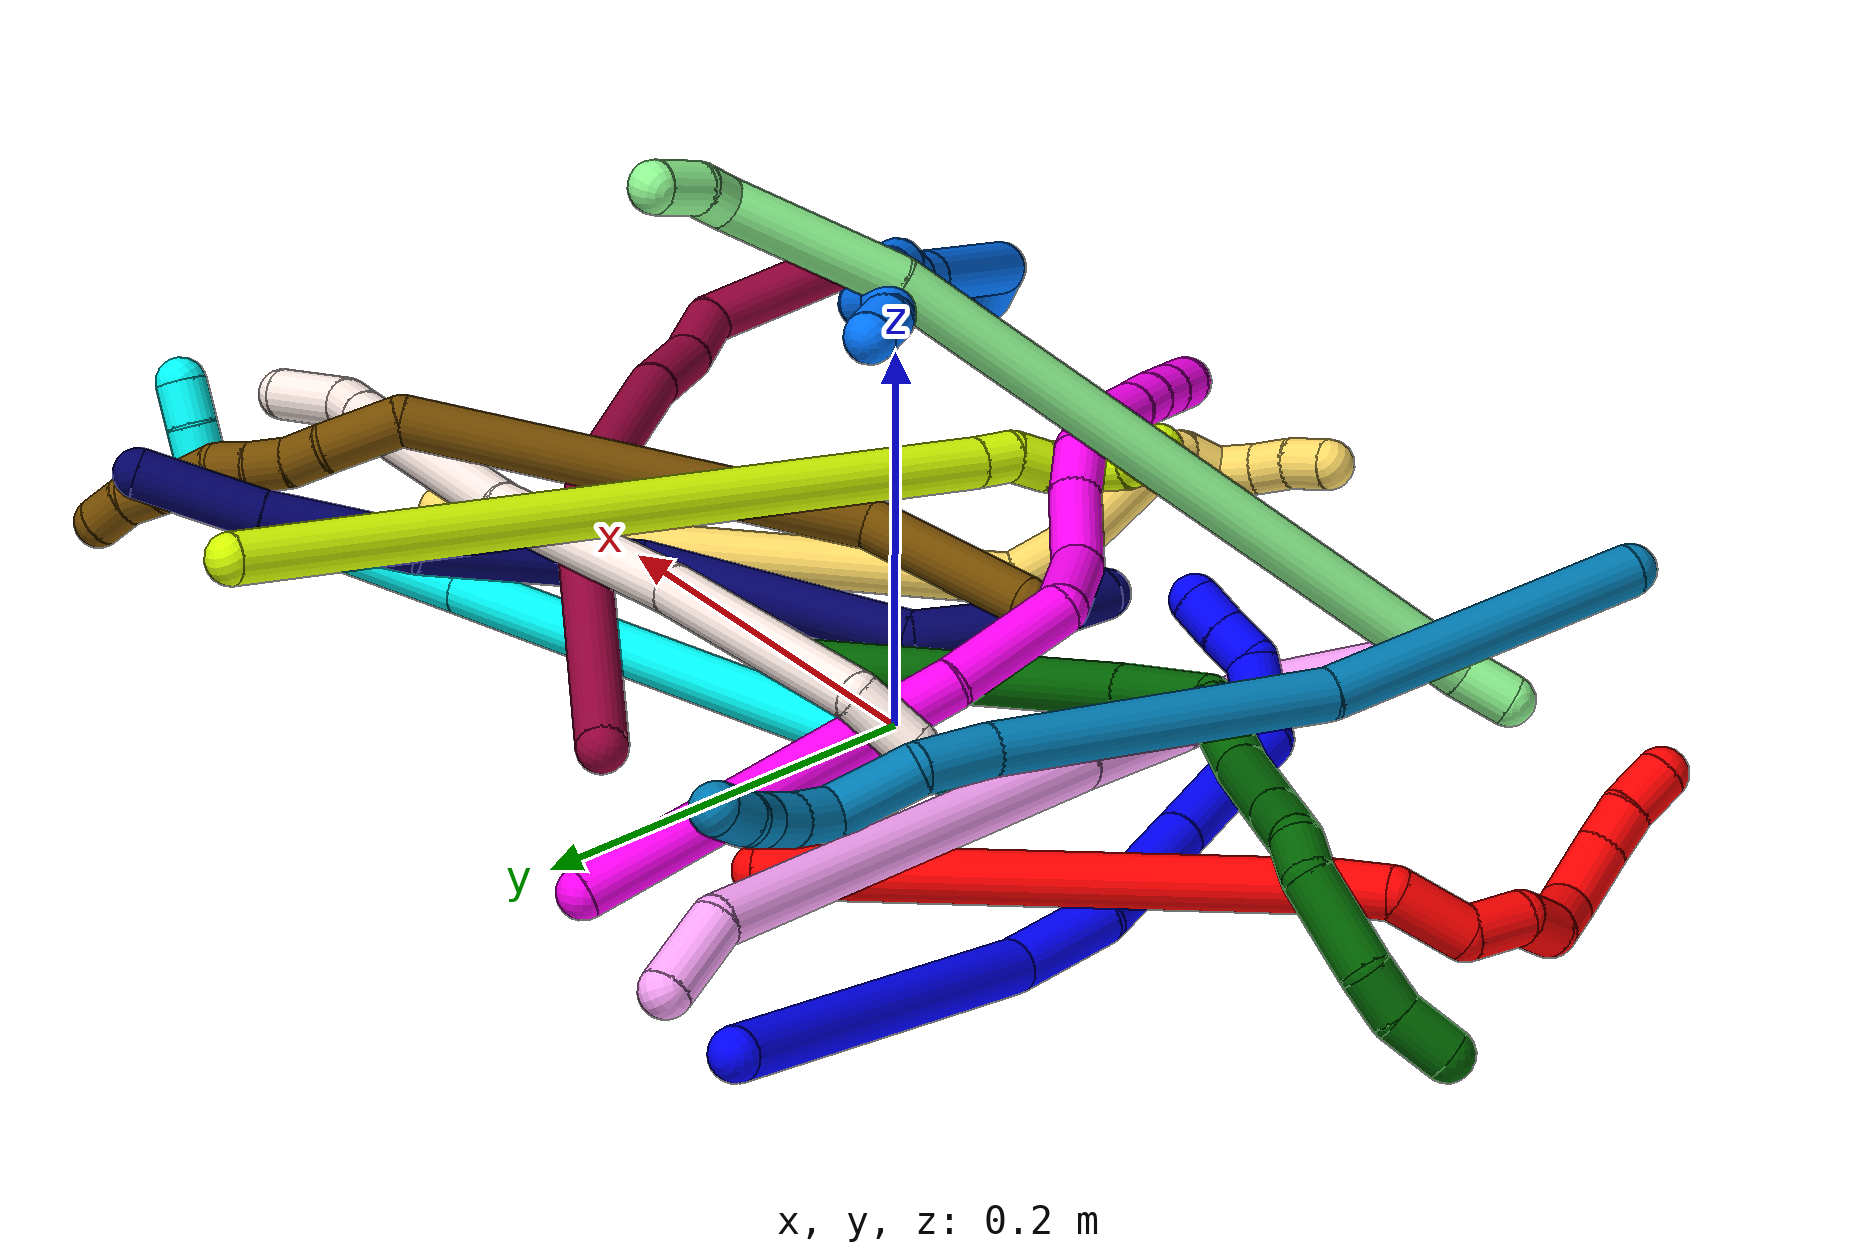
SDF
<sdf version="1.7">
 <world name="default">
  <plugin name="TubeGeneratorPlugin" filename="libtube_generator_plugin.so"/>
  <model name="photoneo_s_sensor">
   <static>1</static>
   <pose>0 0 2 1.57079 1.57079 3.14159</pose>
   <link name="link">
    <inertial><mass>0.1</mass></inertial>
    <sensor name="sensor" type="depth">
     <update_rate>30</update_rate>
     <camera>
      <horizontal_fov>1.22</horizontal_fov>
      <image><width>1920</width><height>1200</height><format>B8G8R8</format></image>
      <clip><near>0.1</near><far>4</far></clip>
      <depth_camera><output>points</output></depth_camera>
     </camera>
     <plugin name="camera_plugin" filename="libgazebo_ros_depth_camera.so">
      <baseline>0.2</baseline>
      <alwaysOn>1</alwaysOn>
      <updateRate>0.0</updateRate>
      <cameraName>camera_ir</cameraName>
      <imageTopicName>/camera/color/image_raw</imageTopicName>
      <cameraInfoTopicName>/camera/color/camera_info</cameraInfoTopicName>
      <depthImageTopicName>/camera/depth/image_raw</depthImageTopicName>
      <depthImageCameraInfoTopicName>/camera/depth/camera_info</depthImageCameraInfoTopicName>
      <pointCloudTopicName>/camera/depth/points</pointCloudTopicName>
      <frameName>fr_optical</frameName>
      <pointCloudCutoff>0.1</pointCloudCutoff>
      <pointCloudCutoffMax>2.0</pointCloudCutoffMax>
      <distortionK1>0</distortionK1>
      <distortionK2>0</distortionK2>
      <distortionK3>0</distortionK3>
      <distortionT1>0</distortionT1>
      <distortionT2>0</distortionT2>
      <CxPrime>0</CxPrime>
      <Cx>0</Cx>
      <Cy>0</Cy>
      <focalLength>0</focalLength>
      <hackBaseline>0</hackBaseline>
     </plugin>
    </sensor>
   </link>
  </model>
  <gravity>0 0 -9.8</gravity>
  <magnetic_field>6e-06 2.3e-05 -4.2e-05</magnetic_field>
  <atmosphere type="adiabatic"/>
  <physics name="default_physics" default="0" type="ode">
   <max_step_size>0.003</max_step_size>
   <real_time_factor>1</real_time_factor>
   <real_time_update_rate>1000</real_time_update_rate>
   <max_contacts>10000</max_contacts>
   <ode>
    <solver>
     <type>quick</type>
     <iters>100</iters>
     <sor>1.3</sor>
     <use_dynamic_moi_rescaling>0</use_dynamic_moi_rescaling>
    </solver>
    <constraints>
     <contact_max_correcting_vel>0</contact_max_correcting_vel>
     <contact_surface_layer>0.001</contact_surface_layer>
     <cfm>0</cfm>
     <erp>0.2</erp>
    </constraints>
   </ode>
  </physics>
  <scene><ambient>0.4 0.4 0.4 1</ambient><background>0.7 0.7 0.7 1</background><shadows>0</shadows></scene>
  <audio><device>default</device></audio>
  <spherical_coordinates>
   <surface_model>EARTH_WGS84</surface_model>
   <latitude_deg>0</latitude_deg>
   <longitude_deg>0</longitude_deg>
   <elevation>0</elevation>
   <heading_deg>0</heading_deg>
  </spherical_coordinates>
  <model name="bin">
   <static>1</static>
   <link name="bottom">
    <collision name="collision-bottom">
     <pose>0 0 -0.01 0 -0 0</pose>
     <geometry><box><size>0.8 0.6 0.02</size></box></geometry>
     <surface>
      <friction><ode><mu>100</mu><mu2>100</mu2></ode></friction>
      <contact><collide_bitmask>65535</collide_bitmask></contact>
     </surface>
    </collision>
   </link>
   <link name="west_wall">
    <collision name="collision-west_wall">
     <pose>-0.41 0 0.1 0 -0 0</pose>
     <geometry><box><size>0.02 0.6 0.2</size></box></geometry>
     <surface>
      <friction><ode><mu>100</mu><mu2>100</mu2></ode></friction>
      <contact><collide_bitmask>65535</collide_bitmask></contact>
     </surface>
    </collision>
   </link>
   <link name="east_wall">
    <collision name="collision-east_wall">
     <pose>0.41 0 0.1 0 -0 0</pose>
     <geometry><box><size>0.02 0.6 0.2</size></box></geometry>
     <surface>
      <friction><ode><mu>100</mu><mu2>100</mu2></ode></friction>
      <contact><collide_bitmask>65535</collide_bitmask></contact>
     </surface>
    </collision>
   </link>
   <link name="south_wall">
    <collision name="collision-south_wall">
     <pose>0 -0.31 0.1 0 -0 0</pose>
     <geometry><box><size>0.8 0.02 0.2</size></box></geometry>
     <surface>
      <friction><ode><mu>100</mu><mu2>100</mu2></ode></friction>
      <contact><collide_bitmask>65535</collide_bitmask></contact>
     </surface>
    </collision>
   </link>
   <link name="north_wall">
    <collision name="collision-north_wall">
     <pose>0 0.31 0.1 0 -0 0</pose>
     <geometry><box><size>0.8 0.02 0.2</size></box></geometry>
     <surface>
      <friction><ode><mu>100</mu><mu2>100</mu2></ode></friction>
      <contact><collide_bitmask>65535</collide_bitmask></contact>
     </surface>
    </collision>
   </link>
  </model>
  <model name="1">
   <static>0</static>
   <link name="1">
    <collision name="collision-cylinder-e_1_1_4">
     <pose>-0.000891 0.000561 -0.101064 -3.13605 -0.008818 2.01854</pose>
     <geometry><cylinder><radius>0.0125</radius><length>0.202139</length></cylinder></geometry>
     <surface>
      <friction><ode><mu>1.16</mu><mu2>1.16</mu2><slip1>0</slip1><slip2>0</slip2></ode></friction>
      <contact><ode><kp>1e+06</kp><kd>1</kd><max_vel>0</max_vel><min_depth>0.001</min_depth></ode></contact>
     </surface>
    </collision>
    <visual name="visual-cylinder-e_1_1_4">
     <pose>-0.000891 0.000561 -0.101064 -3.13605 -0.008818 2.01854</pose>
     <geometry><cylinder><radius>0.0125</radius><length>0.202139</length></cylinder></geometry>
     <material><ambient>0 0 1 1</ambient></material>
    </visual>
    <collision name="collision-cylinder-e_2_4_5">
     <pose>-0.005391 -0.00683 -0.228399 2.84769 -0.130734 -0.832766</pose>
     <geometry><cylinder><radius>0.0125</radius><length>0.055369</length></cylinder></geometry>
     <surface>
      <friction><ode><mu>1.16</mu><mu2>1.16</mu2><slip1>0</slip1><slip2>0</slip2></ode></friction>
      <contact><ode><kp>1e+06</kp><kd>1</kd><max_vel>0</max_vel><min_depth>0.001</min_depth></ode></contact>
     </surface>
    </collision>
    <visual name="visual-cylinder-e_2_4_5">
     <pose>-0.005391 -0.00683 -0.228399 2.84769 -0.130734 -0.832766</pose>
     <geometry><cylinder><radius>0.0125</radius><length>0.055369</length></cylinder></geometry>
     <material><ambient>0 0 1 1</ambient></material>
    </visual>
    <collision name="collision-cylinder-e_3_5_6">
     <pose>-0.003913 -0.026224 -0.288149 2.81227 0.142813 0.812967</pose>
     <geometry><cylinder><radius>0.0125</radius><length>0.071487</length></cylinder></geometry>
     <surface>
      <friction><ode><mu>1.16</mu><mu2>1.16</mu2><slip1>0</slip1><slip2>0</slip2></ode></friction>
      <contact><ode><kp>1e+06</kp><kd>1</kd><max_vel>0</max_vel><min_depth>0.001</min_depth></ode></contact>
     </surface>
    </collision>
    <visual name="visual-cylinder-e_3_5_6">
     <pose>-0.003913 -0.026224 -0.288149 2.81227 0.142813 0.812967</pose>
     <geometry><cylinder><radius>0.0125</radius><length>0.071487</length></cylinder></geometry>
     <material><ambient>0 0 1 1</ambient></material>
    </visual>
    <collision name="collision-cylinder-e_4_6_7">
     <pose>0.007696 -0.051219 -0.362388 2.82059 0.150687 0.872596</pose>
     <geometry><cylinder><radius>0.0125</radius><length>0.086893</length></cylinder></geometry>
     <surface>
      <friction><ode><mu>1.16</mu><mu2>1.16</mu2><slip1>0</slip1><slip2>0</slip2></ode></friction>
      <contact><ode><kp>1e+06</kp><kd>1</kd><max_vel>0</max_vel><min_depth>0.001</min_depth></ode></contact>
     </surface>
    </collision>
    <visual name="visual-cylinder-e_4_6_7">
     <pose>0.007696 -0.051219 -0.362388 2.82059 0.150687 0.872596</pose>
     <geometry><cylinder><radius>0.0125</radius><length>0.086893</length></cylinder></geometry>
     <material><ambient>0 0 1 1</ambient></material>
    </visual>
    <collision name="collision-cylinder-e_5_7_8">
     <pose>0.021947 -0.070338 -0.408962 2.37802 0.765078 1.57297</pose>
     <geometry><cylinder><radius>0.0125</radius><length>0.022319</length></cylinder></geometry>
     <surface>
      <friction><ode><mu>1.16</mu><mu2>1.16</mu2><slip1>0</slip1><slip2>0</slip2></ode></friction>
      <contact><ode><kp>1e+06</kp><kd>1</kd><max_vel>0</max_vel><min_depth>0.001</min_depth></ode></contact>
     </surface>
    </collision>
    <visual name="visual-cylinder-e_5_7_8">
     <pose>0.021947 -0.070338 -0.408962 2.37802 0.765078 1.57297</pose>
     <geometry><cylinder><radius>0.0125</radius><length>0.022319</length></cylinder></geometry>
     <material><ambient>0 0 1 1</ambient></material>
    </visual>
    <collision name="collision-cylinder-e_6_8_9">
     <pose>0.036129 -0.083281 -0.417648 1.94193 0.683937 0.959805</pose>
     <geometry><cylinder><radius>0.0125</radius><length>0.020424</length></cylinder></geometry>
     <surface>
      <friction><ode><mu>1.16</mu><mu2>1.16</mu2><slip1>0</slip1><slip2>0</slip2></ode></friction>
      <contact><ode><kp>1e+06</kp><kd>1</kd><max_vel>0</max_vel><min_depth>0.001</min_depth></ode></contact>
     </surface>
    </collision>
    <visual name="visual-cylinder-e_6_8_9">
     <pose>0.036129 -0.083281 -0.417648 1.94193 0.683937 0.959805</pose>
     <geometry><cylinder><radius>0.0125</radius><length>0.020424</length></cylinder></geometry>
     <material><ambient>0 0 1 1</ambient></material>
    </visual>
    <collision name="collision-cylinder-e_7_9_10">
     <pose>0.052145 -0.093931 -0.420988 1.71324 1.23783 1.37568</pose>
     <geometry><cylinder><radius>0.0125</radius><length>0.020239</length></cylinder></geometry>
     <surface>
      <friction><ode><mu>1.16</mu><mu2>1.16</mu2><slip1>0</slip1><slip2>0</slip2></ode></friction>
      <contact><ode><kp>1e+06</kp><kd>1</kd><max_vel>0</max_vel><min_depth>0.001</min_depth></ode></contact>
     </surface>
    </collision>
    <visual name="visual-cylinder-e_7_9_10">
     <pose>0.052145 -0.093931 -0.420988 1.71324 1.23783 1.37568</pose>
     <geometry><cylinder><radius>0.0125</radius><length>0.020239</length></cylinder></geometry>
     <material><ambient>0 0 1 1</ambient></material>
    </visual>
    <collision name="collision-cylinder-e_8_10_2">
     <pose>0.071502 -0.101093 -0.422223 1.76511 1.18638 1.37338</pose>
     <geometry><cylinder><radius>0.0125</radius><length>0.02113</length></cylinder></geometry>
     <surface>
      <friction><ode><mu>1.16</mu><mu2>1.16</mu2><slip1>0</slip1><slip2>0</slip2></ode></friction>
      <contact><ode><kp>1e+06</kp><kd>1</kd><max_vel>0</max_vel><min_depth>0.001</min_depth></ode></contact>
     </surface>
    </collision>
    <visual name="visual-cylinder-e_8_10_2">
     <pose>0.071502 -0.101093 -0.422223 1.76511 1.18638 1.37338</pose>
     <geometry><cylinder><radius>0.0125</radius><length>0.02113</length></cylinder></geometry>
     <material><ambient>0 0 1 1</ambient></material>
    </visual>
    <collision name="collision-sphere-2">
     <pose>0.081296 -0.10498 -0.422988 0 -0 0</pose>
     <geometry><sphere><radius>0.0125</radius></sphere></geometry>
     <surface>
      <friction><ode><mu>1.16</mu><mu2>1.16</mu2><slip1>0</slip1><slip2>0</slip2></ode></friction>
      <contact><ode><kp>1e+06</kp><kd>1</kd><max_vel>0</max_vel><min_depth>0.001</min_depth></ode></contact>
     </surface>
    </collision>
    <visual name="visual-sphere-2">
     <pose>0.081296 -0.10498 -0.422988 0 -0 0</pose>
     <geometry><sphere><radius>0.0125</radius></sphere></geometry>
     <material><ambient>0 0 1 1</ambient></material>
    </visual>
    <collision name="collision-sphere-10">
     <pose>0.061708 -0.097205 -0.421458 0 -0 0</pose>
     <geometry><sphere><radius>0.0125</radius></sphere></geometry>
     <surface>
      <friction><ode><mu>1.16</mu><mu2>1.16</mu2><slip1>0</slip1><slip2>0</slip2></ode></friction>
      <contact><ode><kp>1e+06</kp><kd>1</kd><max_vel>0</max_vel><min_depth>0.001</min_depth></ode></contact>
     </surface>
    </collision>
    <visual name="visual-sphere-10">
     <pose>0.061708 -0.097205 -0.421458 0 -0 0</pose>
     <geometry><sphere><radius>0.0125</radius></sphere></geometry>
     <material><ambient>0 0 1 1</ambient></material>
    </visual>
    <collision name="collision-sphere-9">
     <pose>0.042581 -0.090657 -0.420519 0 -0 0</pose>
     <geometry><sphere><radius>0.0125</radius></sphere></geometry>
     <surface>
      <friction><ode><mu>1.16</mu><mu2>1.16</mu2><slip1>0</slip1><slip2>0</slip2></ode></friction>
      <contact><ode><kp>1e+06</kp><kd>1</kd><max_vel>0</max_vel><min_depth>0.001</min_depth></ode></contact>
     </surface>
    </collision>
    <visual name="visual-sphere-9">
     <pose>0.042581 -0.090657 -0.420519 0 -0 0</pose>
     <geometry><sphere><radius>0.0125</radius></sphere></geometry>
     <material><ambient>0 0 1 1</ambient></material>
    </visual>
    <collision name="collision-sphere-4">
     <pose>-0.001782 0.001121 -0.202128 0 -0 0</pose>
     <geometry><sphere><radius>0.0125</radius></sphere></geometry>
     <surface>
      <friction><ode><mu>1.16</mu><mu2>1.16</mu2><slip1>0</slip1><slip2>0</slip2></ode></friction>
      <contact><ode><kp>1e+06</kp><kd>1</kd><max_vel>0</max_vel><min_depth>0.001</min_depth></ode></contact>
     </surface>
    </collision>
    <visual name="visual-sphere-4">
     <pose>-0.001782 0.001121 -0.202128 0 -0 0</pose>
     <geometry><sphere><radius>0.0125</radius></sphere></geometry>
     <material><ambient>0 0 1 1</ambient></material>
    </visual>
    <collision name="collision-sphere-1">
     <geometry><sphere><radius>0.0125</radius></sphere></geometry>
     <surface>
      <friction><ode><mu>1.16</mu><mu2>1.16</mu2><slip1>0</slip1><slip2>0</slip2></ode></friction>
      <contact><ode><kp>1e+06</kp><kd>1</kd><max_vel>0</max_vel><min_depth>0.001</min_depth></ode></contact>
     </surface>
    </collision>
    <visual name="visual-sphere-1">
     <geometry><sphere><radius>0.0125</radius></sphere></geometry>
     <material><ambient>0 0 1 1</ambient></material>
    </visual>
    <collision name="collision-sphere-8">
     <pose>0.029676 -0.075904 -0.414777 0 -0 0</pose>
     <geometry><sphere><radius>0.0125</radius></sphere></geometry>
     <surface>
      <friction><ode><mu>1.16</mu><mu2>1.16</mu2><slip1>0</slip1><slip2>0</slip2></ode></friction>
      <contact><ode><kp>1e+06</kp><kd>1</kd><max_vel>0</max_vel><min_depth>0.001</min_depth></ode></contact>
     </surface>
    </collision>
    <visual name="visual-sphere-8">
     <pose>0.029676 -0.075904 -0.414777 0 -0 0</pose>
     <geometry><sphere><radius>0.0125</radius></sphere></geometry>
     <material><ambient>0 0 1 1</ambient></material>
    </visual>
    <collision name="collision-sphere-5">
     <pose>-0.009 -0.014782 -0.254671 0 -0 0</pose>
     <geometry><sphere><radius>0.0125</radius></sphere></geometry>
     <surface>
      <friction><ode><mu>1.16</mu><mu2>1.16</mu2><slip1>0</slip1><slip2>0</slip2></ode></friction>
      <contact><ode><kp>1e+06</kp><kd>1</kd><max_vel>0</max_vel><min_depth>0.001</min_depth></ode></contact>
     </surface>
    </collision>
    <visual name="visual-sphere-5">
     <pose>-0.009 -0.014782 -0.254671 0 -0 0</pose>
     <geometry><sphere><radius>0.0125</radius></sphere></geometry>
     <material><ambient>0 0 1 1</ambient></material>
    </visual>
    <collision name="collision-sphere-6">
     <pose>0.001174 -0.037666 -0.321628 0 -0 0</pose>
     <geometry><sphere><radius>0.0125</radius></sphere></geometry>
     <surface>
      <friction><ode><mu>1.16</mu><mu2>1.16</mu2><slip1>0</slip1><slip2>0</slip2></ode></friction>
      <contact><ode><kp>1e+06</kp><kd>1</kd><max_vel>0</max_vel><min_depth>0.001</min_depth></ode></contact>
     </surface>
    </collision>
    <visual name="visual-sphere-6">
     <pose>0.001174 -0.037666 -0.321628 0 -0 0</pose>
     <geometry><sphere><radius>0.0125</radius></sphere></geometry>
     <material><ambient>0 0 1 1</ambient></material>
    </visual>
    <collision name="collision-sphere-7">
     <pose>0.014218 -0.064772 -0.403148 0 -0 0</pose>
     <geometry><sphere><radius>0.0125</radius></sphere></geometry>
     <surface>
      <friction><ode><mu>1.16</mu><mu2>1.16</mu2><slip1>0</slip1><slip2>0</slip2></ode></friction>
      <contact><ode><kp>1e+06</kp><kd>1</kd><max_vel>0</max_vel><min_depth>0.001</min_depth></ode></contact>
     </surface>
    </collision>
    <visual name="visual-sphere-7">
     <pose>0.014218 -0.064772 -0.403148 0 -0 0</pose>
     <geometry><sphere><radius>0.0125</radius></sphere></geometry>
     <material><ambient>0 0 1 1</ambient></material>
    </visual>
    <inertial>
     <pose>0.007409 -0.027796 -0.240525 0 -0 0</pose>
     <mass>0.5</mass>
     <inertia>
      <ixx>0.000463</ixx>
      <ixy>0</ixy>
      <ixz>0</ixz>
      <iyy>0.00092</iyy>
      <iyz>0</iyz>
      <izz>-1.1e-05</izz>
     </inertia>
    </inertial>
   </link>
   <pose>-0.249066 0.284091 0.068504 -1.29043 -0.061384 0.226186</pose>
  </model>
  <model name="2">
   <static>0</static>
   <link name="2">
    <collision name="collision-cylinder-e_1_1_4">
     <pose>-0.007382 -0.033591 0.129944 0.252968 -0.054948 -0.006989</pose>
     <geometry><cylinder><radius>0.0125</radius><length>0.268836</length></cylinder></geometry>
     <surface>
      <friction><ode><mu>1.16</mu><mu2>1.16</mu2><slip1>0</slip1><slip2>0</slip2></ode></friction>
      <contact><ode><kp>1e+06</kp><kd>1</kd><max_vel>0</max_vel><min_depth>0.001</min_depth></ode></contact>
     </surface>
    </collision>
    <visual name="visual-cylinder-e_1_1_4">
     <pose>-0.007382 -0.033591 0.129944 0.252968 -0.054948 -0.006989</pose>
     <geometry><cylinder><radius>0.0125</radius><length>0.268836</length></cylinder></geometry>
     <material><ambient>1 0 0 1</ambient></material>
    </visual>
    <collision name="collision-cylinder-e_2_4_5">
     <pose>-0.016049 -0.069549 0.273017 0.178331 -0.095969 -0.008586</pose>
     <geometry><cylinder><radius>0.0125</radius><length>0.026806</length></cylinder></geometry>
     <surface>
      <friction><ode><mu>1.16</mu><mu2>1.16</mu2><slip1>0</slip1><slip2>0</slip2></ode></friction>
      <contact><ode><kp>1e+06</kp><kd>1</kd><max_vel>0</max_vel><min_depth>0.001</min_depth></ode></contact>
     </surface>
    </collision>
    <visual name="visual-cylinder-e_2_4_5">
     <pose>-0.016049 -0.069549 0.273017 0.178331 -0.095969 -0.008586</pose>
     <geometry><cylinder><radius>0.0125</radius><length>0.026806</length></cylinder></geometry>
     <material><ambient>1 0 0 1</ambient></material>
    </visual>
    <collision name="collision-cylinder-e_3_5_6">
     <pose>-0.031309 -0.07594 0.29869 0.310493 -0.814962 -0.134903</pose>
     <geometry><cylinder><radius>0.0125</radius><length>0.038411</length></cylinder></geometry>
     <surface>
      <friction><ode><mu>1.16</mu><mu2>1.16</mu2><slip1>0</slip1><slip2>0</slip2></ode></friction>
      <contact><ode><kp>1e+06</kp><kd>1</kd><max_vel>0</max_vel><min_depth>0.001</min_depth></ode></contact>
     </surface>
    </collision>
    <visual name="visual-cylinder-e_3_5_6">
     <pose>-0.031309 -0.07594 0.29869 0.310493 -0.814962 -0.134903</pose>
     <geometry><cylinder><radius>0.0125</radius><length>0.038411</length></cylinder></geometry>
     <material><ambient>1 0 0 1</ambient></material>
    </visual>
    <collision name="collision-cylinder-e_4_6_7">
     <pose>-0.051244 -0.092518 0.317553 1.10435 -0.40099 -0.249118</pose>
     <geometry><cylinder><radius>0.0125</radius><length>0.03053</length></cylinder></geometry>
     <surface>
      <friction><ode><mu>1.16</mu><mu2>1.16</mu2><slip1>0</slip1><slip2>0</slip2></ode></friction>
      <contact><ode><kp>1e+06</kp><kd>1</kd><max_vel>0</max_vel><min_depth>0.001</min_depth></ode></contact>
     </surface>
    </collision>
    <visual name="visual-cylinder-e_4_6_7">
     <pose>-0.051244 -0.092518 0.317553 1.10435 -0.40099 -0.249118</pose>
     <geometry><cylinder><radius>0.0125</radius><length>0.03053</length></cylinder></geometry>
     <material><ambient>1 0 0 1</ambient></material>
    </visual>
    <collision name="collision-cylinder-e_5_7_8">
     <pose>-0.068055 -0.112166 0.325372 1.36276 -0.981766 -0.818044</pose>
     <geometry><cylinder><radius>0.0125</radius><length>0.026106</length></cylinder></geometry>
     <surface>
      <friction><ode><mu>1.16</mu><mu2>1.16</mu2><slip1>0</slip1><slip2>0</slip2></ode></friction>
      <contact><ode><kp>1e+06</kp><kd>1</kd><max_vel>0</max_vel><min_depth>0.001</min_depth></ode></contact>
     </surface>
    </collision>
    <visual name="visual-cylinder-e_5_7_8">
     <pose>-0.068055 -0.112166 0.325372 1.36276 -0.981766 -0.818044</pose>
     <geometry><cylinder><radius>0.0125</radius><length>0.026106</length></cylinder></geometry>
     <material><ambient>1 0 0 1</ambient></material>
    </visual>
    <collision name="collision-cylinder-e_6_8_9">
     <pose>-0.085267 -0.132155 0.323406 1.83319 -0.444466 -0.573111</pose>
     <geometry><cylinder><radius>0.0125</radius><length>0.029575</length></cylinder></geometry>
     <surface>
      <friction><ode><mu>1.16</mu><mu2>1.16</mu2><slip1>0</slip1><slip2>0</slip2></ode></friction>
      <contact><ode><kp>1e+06</kp><kd>1</kd><max_vel>0</max_vel><min_depth>0.001</min_depth></ode></contact>
     </surface>
    </collision>
    <visual name="visual-cylinder-e_6_8_9">
     <pose>-0.085267 -0.132155 0.323406 1.83319 -0.444466 -0.573111</pose>
     <geometry><cylinder><radius>0.0125</radius><length>0.029575</length></cylinder></geometry>
     <material><ambient>1 0 0 1</ambient></material>
    </visual>
    <collision name="collision-cylinder-e_7_9_10">
     <pose>-0.08858 -0.161394 0.322185 1.43447 0.182491 0.159271</pose>
     <geometry><cylinder><radius>0.0125</radius><length>0.033553</length></cylinder></geometry>
     <surface>
      <friction><ode><mu>1.16</mu><mu2>1.16</mu2><slip1>0</slip1><slip2>0</slip2></ode></friction>
      <contact><ode><kp>1e+06</kp><kd>1</kd><max_vel>0</max_vel><min_depth>0.001</min_depth></ode></contact>
     </surface>
    </collision>
    <visual name="visual-cylinder-e_7_9_10">
     <pose>-0.08858 -0.161394 0.322185 1.43447 0.182491 0.159271</pose>
     <geometry><cylinder><radius>0.0125</radius><length>0.033553</length></cylinder></geometry>
     <material><ambient>1 0 0 1</ambient></material>
    </visual>
    <collision name="collision-cylinder-e_8_10_11">
     <pose>-0.083094 -0.188044 0.326526 1.36993 0.228132 0.186631</pose>
     <geometry><cylinder><radius>0.0125</radius><length>0.021594</length></cylinder></geometry>
     <surface>
      <friction><ode><mu>1.16</mu><mu2>1.16</mu2><slip1>0</slip1><slip2>0</slip2></ode></friction>
      <contact><ode><kp>1e+06</kp><kd>1</kd><max_vel>0</max_vel><min_depth>0.001</min_depth></ode></contact>
     </surface>
    </collision>
    <visual name="visual-cylinder-e_8_10_11">
     <pose>-0.083094 -0.188044 0.326526 1.36993 0.228132 0.186631</pose>
     <geometry><cylinder><radius>0.0125</radius><length>0.021594</length></cylinder></geometry>
     <material><ambient>1 0 0 1</ambient></material>
    </visual>
    <collision name="collision-cylinder-e_9_11_2">
     <pose>-0.079792 -0.210084 0.332191 1.2757 0.070026 0.051913</pose>
     <geometry><cylinder><radius>0.0125</radius><length>0.024589</length></cylinder></geometry>
     <surface>
      <friction><ode><mu>1.16</mu><mu2>1.16</mu2><slip1>0</slip1><slip2>0</slip2></ode></friction>
      <contact><ode><kp>1e+06</kp><kd>1</kd><max_vel>0</max_vel><min_depth>0.001</min_depth></ode></contact>
     </surface>
    </collision>
    <visual name="visual-cylinder-e_9_11_2">
     <pose>-0.079792 -0.210084 0.332191 1.2757 0.070026 0.051913</pose>
     <geometry><cylinder><radius>0.0125</radius><length>0.024589</length></cylinder></geometry>
     <material><ambient>1 0 0 1</ambient></material>
    </visual>
    <collision name="collision-sphere-2">
     <pose>-0.078932 -0.221818 0.335758 0 -0 0</pose>
     <geometry><sphere><radius>0.0125</radius></sphere></geometry>
     <surface>
      <friction><ode><mu>1.16</mu><mu2>1.16</mu2><slip1>0</slip1><slip2>0</slip2></ode></friction>
      <contact><ode><kp>1e+06</kp><kd>1</kd><max_vel>0</max_vel><min_depth>0.001</min_depth></ode></contact>
     </surface>
    </collision>
    <visual name="visual-sphere-2">
     <pose>-0.078932 -0.221818 0.335758 0 -0 0</pose>
     <geometry><sphere><radius>0.0125</radius></sphere></geometry>
     <material><ambient>1 0 0 1</ambient></material>
    </visual>
    <collision name="collision-sphere-11">
     <pose>-0.080652 -0.19835 0.328624 0 -0 0</pose>
     <geometry><sphere><radius>0.0125</radius></sphere></geometry>
     <surface>
      <friction><ode><mu>1.16</mu><mu2>1.16</mu2><slip1>0</slip1><slip2>0</slip2></ode></friction>
      <contact><ode><kp>1e+06</kp><kd>1</kd><max_vel>0</max_vel><min_depth>0.001</min_depth></ode></contact>
     </surface>
    </collision>
    <visual name="visual-sphere-11">
     <pose>-0.080652 -0.19835 0.328624 0 -0 0</pose>
     <geometry><sphere><radius>0.0125</radius></sphere></geometry>
     <material><ambient>1 0 0 1</ambient></material>
    </visual>
    <collision name="collision-sphere-10">
     <pose>-0.085536 -0.177739 0.324428 0 -0 0</pose>
     <geometry><sphere><radius>0.0125</radius></sphere></geometry>
     <surface>
      <friction><ode><mu>1.16</mu><mu2>1.16</mu2><slip1>0</slip1><slip2>0</slip2></ode></friction>
      <contact><ode><kp>1e+06</kp><kd>1</kd><max_vel>0</max_vel><min_depth>0.001</min_depth></ode></contact>
     </surface>
    </collision>
    <visual name="visual-sphere-10">
     <pose>-0.085536 -0.177739 0.324428 0 -0 0</pose>
     <geometry><sphere><radius>0.0125</radius></sphere></geometry>
     <material><ambient>1 0 0 1</ambient></material>
    </visual>
    <collision name="collision-sphere-9">
     <pose>-0.091625 -0.145049 0.319943 0 -0 0</pose>
     <geometry><sphere><radius>0.0125</radius></sphere></geometry>
     <surface>
      <friction><ode><mu>1.16</mu><mu2>1.16</mu2><slip1>0</slip1><slip2>0</slip2></ode></friction>
      <contact><ode><kp>1e+06</kp><kd>1</kd><max_vel>0</max_vel><min_depth>0.001</min_depth></ode></contact>
     </surface>
    </collision>
    <visual name="visual-sphere-9">
     <pose>-0.091625 -0.145049 0.319943 0 -0 0</pose>
     <geometry><sphere><radius>0.0125</radius></sphere></geometry>
     <material><ambient>1 0 0 1</ambient></material>
    </visual>
    <collision name="collision-sphere-4">
     <pose>-0.014765 -0.067182 0.259887 0 -0 0</pose>
     <geometry><sphere><radius>0.0125</radius></sphere></geometry>
     <surface>
      <friction><ode><mu>1.16</mu><mu2>1.16</mu2><slip1>0</slip1><slip2>0</slip2></ode></friction>
      <contact><ode><kp>1e+06</kp><kd>1</kd><max_vel>0</max_vel><min_depth>0.001</min_depth></ode></contact>
     </surface>
    </collision>
    <visual name="visual-sphere-4">
     <pose>-0.014765 -0.067182 0.259887 0 -0 0</pose>
     <geometry><sphere><radius>0.0125</radius></sphere></geometry>
     <material><ambient>1 0 0 1</ambient></material>
    </visual>
    <collision name="collision-sphere-1">
     <geometry><sphere><radius>0.0125</radius></sphere></geometry>
     <surface>
      <friction><ode><mu>1.16</mu><mu2>1.16</mu2><slip1>0</slip1><slip2>0</slip2></ode></friction>
      <contact><ode><kp>1e+06</kp><kd>1</kd><max_vel>0</max_vel><min_depth>0.001</min_depth></ode></contact>
     </surface>
    </collision>
    <visual name="visual-sphere-1">
     <geometry><sphere><radius>0.0125</radius></sphere></geometry>
     <material><ambient>1 0 0 1</ambient></material>
    </visual>
    <collision name="collision-sphere-8">
     <pose>-0.078908 -0.119261 0.326869 0 -0 0</pose>
     <geometry><sphere><radius>0.0125</radius></sphere></geometry>
     <surface>
      <friction><ode><mu>1.16</mu><mu2>1.16</mu2><slip1>0</slip1><slip2>0</slip2></ode></friction>
      <contact><ode><kp>1e+06</kp><kd>1</kd><max_vel>0</max_vel><min_depth>0.001</min_depth></ode></contact>
     </surface>
    </collision>
    <visual name="visual-sphere-8">
     <pose>-0.078908 -0.119261 0.326869 0 -0 0</pose>
     <geometry><sphere><radius>0.0125</radius></sphere></geometry>
     <material><ambient>1 0 0 1</ambient></material>
    </visual>
    <collision name="collision-sphere-5">
     <pose>-0.017333 -0.071915 0.286147 0 -0 0</pose>
     <geometry><sphere><radius>0.0125</radius></sphere></geometry>
     <surface>
      <friction><ode><mu>1.16</mu><mu2>1.16</mu2><slip1>0</slip1><slip2>0</slip2></ode></friction>
      <contact><ode><kp>1e+06</kp><kd>1</kd><max_vel>0</max_vel><min_depth>0.001</min_depth></ode></contact>
     </surface>
    </collision>
    <visual name="visual-sphere-5">
     <pose>-0.017333 -0.071915 0.286147 0 -0 0</pose>
     <geometry><sphere><radius>0.0125</radius></sphere></geometry>
     <material><ambient>1 0 0 1</ambient></material>
    </visual>
    <collision name="collision-sphere-6">
     <pose>-0.045285 -0.079965 0.311233 0 -0 0</pose>
     <geometry><sphere><radius>0.0125</radius></sphere></geometry>
     <surface>
      <friction><ode><mu>1.16</mu><mu2>1.16</mu2><slip1>0</slip1><slip2>0</slip2></ode></friction>
      <contact><ode><kp>1e+06</kp><kd>1</kd><max_vel>0</max_vel><min_depth>0.001</min_depth></ode></contact>
     </surface>
    </collision>
    <visual name="visual-sphere-6">
     <pose>-0.045285 -0.079965 0.311233 0 -0 0</pose>
     <geometry><sphere><radius>0.0125</radius></sphere></geometry>
     <material><ambient>1 0 0 1</ambient></material>
    </visual>
    <collision name="collision-sphere-7">
     <pose>-0.057202 -0.10507 0.323874 0 -0 0</pose>
     <geometry><sphere><radius>0.0125</radius></sphere></geometry>
     <surface>
      <friction><ode><mu>1.16</mu><mu2>1.16</mu2><slip1>0</slip1><slip2>0</slip2></ode></friction>
      <contact><ode><kp>1e+06</kp><kd>1</kd><max_vel>0</max_vel><min_depth>0.001</min_depth></ode></contact>
     </surface>
    </collision>
    <visual name="visual-sphere-7">
     <pose>-0.057202 -0.10507 0.323874 0 -0 0</pose>
     <geometry><sphere><radius>0.0125</radius></sphere></geometry>
     <material><ambient>1 0 0 1</ambient></material>
    </visual>
    <inertial>
     <pose>-0.032418 -0.076229 0.215017 0 -0 0</pose>
     <mass>0.5</mass>
     <inertia>
      <ixx>0.001628</ixx>
      <ixy>0</ixy>
      <ixz>0</ixz>
      <iyy>0.00156</iyy>
      <iyz>0</iyz>
      <izz>0.000548</izz>
     </inertia>
    </inertial>
   </link>
   <pose>-0.073768 0.137513 0.012281 -1.12974 -1.24381 1.50241</pose>
  </model>
  <model name="3">
   <static>0</static>
   <link name="3">
    <collision name="collision-cylinder-e_1_1_4">
     <pose>0.084259 0.041142 0.116987 -0.338171 0.596798 -0.104922</pose>
     <geometry><cylinder><radius>0.0125</radius><length>0.299855</length></cylinder></geometry>
     <surface>
      <friction><ode><mu>1.16</mu><mu2>1.16</mu2><slip1>0</slip1><slip2>0</slip2></ode></friction>
      <contact><ode><kp>1e+06</kp><kd>1</kd><max_vel>0</max_vel><min_depth>0.001</min_depth></ode></contact>
     </surface>
    </collision>
    <visual name="visual-cylinder-e_1_1_4">
     <pose>0.084259 0.041142 0.116987 -0.338171 0.596798 -0.104922</pose>
     <geometry><cylinder><radius>0.0125</radius><length>0.299855</length></cylinder></geometry>
     <material><ambient>0.003922 1 0.996078 1</ambient></material>
    </visual>
    <collision name="collision-cylinder-e_2_4_5">
     <pose>0.19961 0.09894 0.278995 -0.354338 0.574777 -0.105743</pose>
     <geometry><cylinder><radius>0.0125</radius><length>0.114385</length></cylinder></geometry>
     <surface>
      <friction><ode><mu>1.16</mu><mu2>1.16</mu2><slip1>0</slip1><slip2>0</slip2></ode></friction>
      <contact><ode><kp>1e+06</kp><kd>1</kd><max_vel>0</max_vel><min_depth>0.001</min_depth></ode></contact>
     </surface>
    </collision>
    <visual name="visual-cylinder-e_2_4_5">
     <pose>0.19961 0.09894 0.278995 -0.354338 0.574777 -0.105743</pose>
     <geometry><cylinder><radius>0.0125</radius><length>0.114385</length></cylinder></geometry>
     <material><ambient>0.003922 1 0.996078 1</ambient></material>
    </visual>
    <collision name="collision-cylinder-e_3_5_6">
     <pose>0.22911 0.120316 0.334053 -0.439655 -0.142646 0.031924</pose>
     <geometry><cylinder><radius>0.0125</radius><length>0.022413</length></cylinder></geometry>
     <surface>
      <friction><ode><mu>1.16</mu><mu2>1.16</mu2><slip1>0</slip1><slip2>0</slip2></ode></friction>
      <contact><ode><kp>1e+06</kp><kd>1</kd><max_vel>0</max_vel><min_depth>0.001</min_depth></ode></contact>
     </surface>
    </collision>
    <visual name="visual-cylinder-e_3_5_6">
     <pose>0.22911 0.120316 0.334053 -0.439655 -0.142646 0.031924</pose>
     <geometry><cylinder><radius>0.0125</radius><length>0.022413</length></cylinder></geometry>
     <material><ambient>0.003922 1 0.996078 1</ambient></material>
    </visual>
    <collision name="collision-cylinder-e_4_6_7">
     <pose>0.227151 0.125964 0.354748 -0.086736 -0.034174 0.001483</pose>
     <geometry><cylinder><radius>0.0125</radius><length>0.021407</length></cylinder></geometry>
     <surface>
      <friction><ode><mu>1.16</mu><mu2>1.16</mu2><slip1>0</slip1><slip2>0</slip2></ode></friction>
      <contact><ode><kp>1e+06</kp><kd>1</kd><max_vel>0</max_vel><min_depth>0.001</min_depth></ode></contact>
     </surface>
    </collision>
    <visual name="visual-cylinder-e_4_6_7">
     <pose>0.227151 0.125964 0.354748 -0.086736 -0.034174 0.001483</pose>
     <geometry><cylinder><radius>0.0125</radius><length>0.021407</length></cylinder></geometry>
     <material><ambient>0.003922 1 0.996078 1</ambient></material>
    </visual>
    <collision name="collision-cylinder-e_5_7_8">
     <pose>0.224295 0.123073 0.374406 0.401209 -0.249369 -0.05096</pose>
     <geometry><cylinder><radius>0.0125</radius><length>0.020179</length></cylinder></geometry>
     <surface>
      <friction><ode><mu>1.16</mu><mu2>1.16</mu2><slip1>0</slip1><slip2>0</slip2></ode></friction>
      <contact><ode><kp>1e+06</kp><kd>1</kd><max_vel>0</max_vel><min_depth>0.001</min_depth></ode></contact>
     </surface>
    </collision>
    <visual name="visual-cylinder-e_5_7_8">
     <pose>0.224295 0.123073 0.374406 0.401209 -0.249369 -0.05096</pose>
     <geometry><cylinder><radius>0.0125</radius><length>0.020179</length></cylinder></geometry>
     <material><ambient>0.003922 1 0.996078 1</ambient></material>
    </visual>
    <collision name="collision-cylinder-e_6_8_2">
     <pose>0.22043 0.114794 0.393235 0.42601 -0.126748 -0.027449</pose>
     <geometry><cylinder><radius>0.0125</radius><length>0.021762</length></cylinder></geometry>
     <surface>
      <friction><ode><mu>1.16</mu><mu2>1.16</mu2><slip1>0</slip1><slip2>0</slip2></ode></friction>
      <contact><ode><kp>1e+06</kp><kd>1</kd><max_vel>0</max_vel><min_depth>0.001</min_depth></ode></contact>
     </surface>
    </collision>
    <visual name="visual-cylinder-e_6_8_2">
     <pose>0.22043 0.114794 0.393235 0.42601 -0.126748 -0.027449</pose>
     <geometry><cylinder><radius>0.0125</radius><length>0.021762</length></cylinder></geometry>
     <material><ambient>0.003922 1 0.996078 1</ambient></material>
    </visual>
    <collision name="collision-sphere-2">
     <pose>0.219054 0.110334 0.403064 0 -0 0</pose>
     <geometry><sphere><radius>0.0125</radius></sphere></geometry>
     <surface>
      <friction><ode><mu>1.16</mu><mu2>1.16</mu2><slip1>0</slip1><slip2>0</slip2></ode></friction>
      <contact><ode><kp>1e+06</kp><kd>1</kd><max_vel>0</max_vel><min_depth>0.001</min_depth></ode></contact>
     </surface>
    </collision>
    <visual name="visual-sphere-2">
     <pose>0.219054 0.110334 0.403064 0 -0 0</pose>
     <geometry><sphere><radius>0.0125</radius></sphere></geometry>
     <material><ambient>0.003922 1 0.996078 1</ambient></material>
    </visual>
    <collision name="collision-sphere-4">
     <pose>0.168518 0.082284 0.233975 0 -0 0</pose>
     <geometry><sphere><radius>0.0125</radius></sphere></geometry>
     <surface>
      <friction><ode><mu>1.16</mu><mu2>1.16</mu2><slip1>0</slip1><slip2>0</slip2></ode></friction>
      <contact><ode><kp>1e+06</kp><kd>1</kd><max_vel>0</max_vel><min_depth>0.001</min_depth></ode></contact>
     </surface>
    </collision>
    <visual name="visual-sphere-4">
     <pose>0.168518 0.082284 0.233975 0 -0 0</pose>
     <geometry><sphere><radius>0.0125</radius></sphere></geometry>
     <material><ambient>0.003922 1 0.996078 1</ambient></material>
    </visual>
    <collision name="collision-sphere-1">
     <geometry><sphere><radius>0.0125</radius></sphere></geometry>
     <surface>
      <friction><ode><mu>1.16</mu><mu2>1.16</mu2><slip1>0</slip1><slip2>0</slip2></ode></friction>
      <contact><ode><kp>1e+06</kp><kd>1</kd><max_vel>0</max_vel><min_depth>0.001</min_depth></ode></contact>
     </surface>
    </collision>
    <visual name="visual-sphere-1">
     <geometry><sphere><radius>0.0125</radius></sphere></geometry>
     <material><ambient>0.003922 1 0.996078 1</ambient></material>
    </visual>
    <collision name="collision-sphere-8">
     <pose>0.221805 0.119254 0.383406 0 -0 0</pose>
     <geometry><sphere><radius>0.0125</radius></sphere></geometry>
     <surface>
      <friction><ode><mu>1.16</mu><mu2>1.16</mu2><slip1>0</slip1><slip2>0</slip2></ode></friction>
      <contact><ode><kp>1e+06</kp><kd>1</kd><max_vel>0</max_vel><min_depth>0.001</min_depth></ode></contact>
     </surface>
    </collision>
    <visual name="visual-sphere-8">
     <pose>0.221805 0.119254 0.383406 0 -0 0</pose>
     <geometry><sphere><radius>0.0125</radius></sphere></geometry>
     <material><ambient>0.003922 1 0.996078 1</ambient></material>
    </visual>
    <collision name="collision-sphere-5">
     <pose>0.230703 0.115595 0.324016 0 -0 0</pose>
     <geometry><sphere><radius>0.0125</radius></sphere></geometry>
     <surface>
      <friction><ode><mu>1.16</mu><mu2>1.16</mu2><slip1>0</slip1><slip2>0</slip2></ode></friction>
      <contact><ode><kp>1e+06</kp><kd>1</kd><max_vel>0</max_vel><min_depth>0.001</min_depth></ode></contact>
     </surface>
    </collision>
    <visual name="visual-sphere-5">
     <pose>0.230703 0.115595 0.324016 0 -0 0</pose>
     <geometry><sphere><radius>0.0125</radius></sphere></geometry>
     <material><ambient>0.003922 1 0.996078 1</ambient></material>
    </visual>
    <collision name="collision-sphere-6">
     <pose>0.227517 0.125038 0.344091 0 -0 0</pose>
     <geometry><sphere><radius>0.0125</radius></sphere></geometry>
     <surface>
      <friction><ode><mu>1.16</mu><mu2>1.16</mu2><slip1>0</slip1><slip2>0</slip2></ode></friction>
      <contact><ode><kp>1e+06</kp><kd>1</kd><max_vel>0</max_vel><min_depth>0.001</min_depth></ode></contact>
     </surface>
    </collision>
    <visual name="visual-sphere-6">
     <pose>0.227517 0.125038 0.344091 0 -0 0</pose>
     <geometry><sphere><radius>0.0125</radius></sphere></geometry>
     <material><ambient>0.003922 1 0.996078 1</ambient></material>
    </visual>
    <collision name="collision-sphere-7">
     <pose>0.226785 0.126891 0.365405 0 -0 0</pose>
     <geometry><sphere><radius>0.0125</radius></sphere></geometry>
     <surface>
      <friction><ode><mu>1.16</mu><mu2>1.16</mu2><slip1>0</slip1><slip2>0</slip2></ode></friction>
      <contact><ode><kp>1e+06</kp><kd>1</kd><max_vel>0</max_vel><min_depth>0.001</min_depth></ode></contact>
     </surface>
    </collision>
    <visual name="visual-sphere-7">
     <pose>0.226785 0.126891 0.365405 0 -0 0</pose>
     <geometry><sphere><radius>0.0125</radius></sphere></geometry>
     <material><ambient>0.003922 1 0.996078 1</ambient></material>
    </visual>
    <inertial>
     <pose>0.134837 0.068057 0.196371 0 -0 0</pose>
     <mass>0.5</mass>
     <inertia>
      <ixx>0.001782</ixx>
      <ixy>0</ixy>
      <ixz>0</ixz>
      <iyy>0.002094</iyy>
      <iyz>0</iyz>
      <izz>-0.001964</izz>
     </inertia>
    </inertial>
   </link>
   <pose>-0.075753 0.011086 0.011498 -0.503973 0.775333 -0.37473</pose>
  </model>
  <model name="4">
   <static>0</static>
   <link name="4">
    <collision name="collision-cylinder-e_1_1_4">
     <pose>0.012906 -0.015781 0.006094 1.20227 0.651697 0.45542</pose>
     <geometry><cylinder><radius>0.0125</radius><length>0.042556</length></cylinder></geometry>
     <surface>
      <friction><ode><mu>1.16</mu><mu2>1.16</mu2><slip1>0</slip1><slip2>0</slip2></ode></friction>
      <contact><ode><kp>1e+06</kp><kd>1</kd><max_vel>0</max_vel><min_depth>0.001</min_depth></ode></contact>
     </surface>
    </collision>
    <visual name="visual-cylinder-e_1_1_4">
     <pose>0.012906 -0.015781 0.006094 1.20227 0.651697 0.45542</pose>
     <geometry><cylinder><radius>0.0125</radius><length>0.042556</length></cylinder></geometry>
     <material><ambient>1 0.65098 0.996078 1</ambient></material>
    </visual>
    <collision name="collision-cylinder-e_2_4_5">
     <pose>0.049872 -0.147691 0.035991 1.36862 0.200251 0.163551</pose>
     <geometry><cylinder><radius>0.0125</radius><length>0.24192</length></cylinder></geometry>
     <surface>
      <friction><ode><mu>1.16</mu><mu2>1.16</mu2><slip1>0</slip1><slip2>0</slip2></ode></friction>
      <contact><ode><kp>1e+06</kp><kd>1</kd><max_vel>0</max_vel><min_depth>0.001</min_depth></ode></contact>
     </surface>
    </collision>
    <visual name="visual-cylinder-e_2_4_5">
     <pose>0.049872 -0.147691 0.035991 1.36862 0.200251 0.163551</pose>
     <geometry><cylinder><radius>0.0125</radius><length>0.24192</length></cylinder></geometry>
     <material><ambient>1 0.65098 0.996078 1</ambient></material>
    </visual>
    <collision name="collision-cylinder-e_3_5_6">
     <pose>0.080531 -0.299808 0.065178 1.42231 0.179378 0.154648</pose>
     <geometry><cylinder><radius>0.0125</radius><length>0.073964</length></cylinder></geometry>
     <surface>
      <friction><ode><mu>1.16</mu><mu2>1.16</mu2><slip1>0</slip1><slip2>0</slip2></ode></friction>
      <contact><ode><kp>1e+06</kp><kd>1</kd><max_vel>0</max_vel><min_depth>0.001</min_depth></ode></contact>
     </surface>
    </collision>
    <visual name="visual-cylinder-e_3_5_6">
     <pose>0.080531 -0.299808 0.065178 1.42231 0.179378 0.154648</pose>
     <geometry><cylinder><radius>0.0125</radius><length>0.073964</length></cylinder></geometry>
     <material><ambient>1 0.65098 0.996078 1</ambient></material>
    </visual>
    <collision name="collision-cylinder-e_4_6_7">
     <pose>0.093498 -0.365541 0.07275 1.49735 0.210353 0.195543</pose>
     <geometry><cylinder><radius>0.0125</radius><length>0.060996</length></cylinder></geometry>
     <surface>
      <friction><ode><mu>1.16</mu><mu2>1.16</mu2><slip1>0</slip1><slip2>0</slip2></ode></friction>
      <contact><ode><kp>1e+06</kp><kd>1</kd><max_vel>0</max_vel><min_depth>0.001</min_depth></ode></contact>
     </surface>
    </collision>
    <visual name="visual-cylinder-e_4_6_7">
     <pose>0.093498 -0.365541 0.07275 1.49735 0.210353 0.195543</pose>
     <geometry><cylinder><radius>0.0125</radius><length>0.060996</length></cylinder></geometry>
     <material><ambient>1 0.65098 0.996078 1</ambient></material>
    </visual>
    <collision name="collision-cylinder-e_5_7_2">
     <pose>0.099235 -0.427062 0.099689 0.909054 -0.015677 -0.007661</pose>
     <geometry><cylinder><radius>0.0125</radius><length>0.080564</length></cylinder></geometry>
     <surface>
      <friction><ode><mu>1.16</mu><mu2>1.16</mu2><slip1>0</slip1><slip2>0</slip2></ode></friction>
      <contact><ode><kp>1e+06</kp><kd>1</kd><max_vel>0</max_vel><min_depth>0.001</min_depth></ode></contact>
     </surface>
    </collision>
    <visual name="visual-cylinder-e_5_7_2">
     <pose>0.099235 -0.427062 0.099689 0.909054 -0.015677 -0.007661</pose>
     <geometry><cylinder><radius>0.0125</radius><length>0.080564</length></cylinder></geometry>
     <material><ambient>1 0.65098 0.996078 1</ambient></material>
    </visual>
    <collision name="collision-sphere-2">
     <pose>0.098603 -0.458838 0.124439 0 -0 0</pose>
     <geometry><sphere><radius>0.0125</radius></sphere></geometry>
     <surface>
      <friction><ode><mu>1.16</mu><mu2>1.16</mu2><slip1>0</slip1><slip2>0</slip2></ode></friction>
      <contact><ode><kp>1e+06</kp><kd>1</kd><max_vel>0</max_vel><min_depth>0.001</min_depth></ode></contact>
     </surface>
    </collision>
    <visual name="visual-sphere-2">
     <pose>0.098603 -0.458838 0.124439 0 -0 0</pose>
     <geometry><sphere><radius>0.0125</radius></sphere></geometry>
     <material><ambient>1 0.65098 0.996078 1</ambient></material>
    </visual>
    <collision name="collision-sphere-7">
     <pose>0.099866 -0.395287 0.074939 0 -0 0</pose>
     <geometry><sphere><radius>0.0125</radius></sphere></geometry>
     <surface>
      <friction><ode><mu>1.16</mu><mu2>1.16</mu2><slip1>0</slip1><slip2>0</slip2></ode></friction>
      <contact><ode><kp>1e+06</kp><kd>1</kd><max_vel>0</max_vel><min_depth>0.001</min_depth></ode></contact>
     </surface>
    </collision>
    <visual name="visual-sphere-7">
     <pose>0.099866 -0.395287 0.074939 0 -0 0</pose>
     <geometry><sphere><radius>0.0125</radius></sphere></geometry>
     <material><ambient>1 0.65098 0.996078 1</ambient></material>
    </visual>
    <collision name="collision-sphere-6">
     <pose>0.08713 -0.335796 0.070562 0 -0 0</pose>
     <geometry><sphere><radius>0.0125</radius></sphere></geometry>
     <surface>
      <friction><ode><mu>1.16</mu><mu2>1.16</mu2><slip1>0</slip1><slip2>0</slip2></ode></friction>
      <contact><ode><kp>1e+06</kp><kd>1</kd><max_vel>0</max_vel><min_depth>0.001</min_depth></ode></contact>
     </surface>
    </collision>
    <visual name="visual-sphere-6">
     <pose>0.08713 -0.335796 0.070562 0 -0 0</pose>
     <geometry><sphere><radius>0.0125</radius></sphere></geometry>
     <material><ambient>1 0.65098 0.996078 1</ambient></material>
    </visual>
    <collision name="collision-sphere-5">
     <pose>0.073933 -0.263819 0.059795 0 -0 0</pose>
     <geometry><sphere><radius>0.0125</radius></sphere></geometry>
     <surface>
      <friction><ode><mu>1.16</mu><mu2>1.16</mu2><slip1>0</slip1><slip2>0</slip2></ode></friction>
      <contact><ode><kp>1e+06</kp><kd>1</kd><max_vel>0</max_vel><min_depth>0.001</min_depth></ode></contact>
     </surface>
    </collision>
    <visual name="visual-sphere-5">
     <pose>0.073933 -0.263819 0.059795 0 -0 0</pose>
     <geometry><sphere><radius>0.0125</radius></sphere></geometry>
     <material><ambient>1 0.65098 0.996078 1</ambient></material>
    </visual>
    <collision name="collision-sphere-1">
     <geometry><sphere><radius>0.0125</radius></sphere></geometry>
     <surface>
      <friction><ode><mu>1.16</mu><mu2>1.16</mu2><slip1>0</slip1><slip2>0</slip2></ode></friction>
      <contact><ode><kp>1e+06</kp><kd>1</kd><max_vel>0</max_vel><min_depth>0.001</min_depth></ode></contact>
     </surface>
    </collision>
    <visual name="visual-sphere-1">
     <geometry><sphere><radius>0.0125</radius></sphere></geometry>
     <material><ambient>1 0.65098 0.996078 1</ambient></material>
    </visual>
    <collision name="collision-sphere-4">
     <pose>0.025812 -0.031562 0.012188 0 -0 0</pose>
     <geometry><sphere><radius>0.0125</radius></sphere></geometry>
     <surface>
      <friction><ode><mu>1.16</mu><mu2>1.16</mu2><slip1>0</slip1><slip2>0</slip2></ode></friction>
      <contact><ode><kp>1e+06</kp><kd>1</kd><max_vel>0</max_vel><min_depth>0.001</min_depth></ode></contact>
     </surface>
    </collision>
    <visual name="visual-sphere-4">
     <pose>0.025812 -0.031562 0.012188 0 -0 0</pose>
     <geometry><sphere><radius>0.0125</radius></sphere></geometry>
     <material><ambient>1 0.65098 0.996078 1</ambient></material>
    </visual>
    <inertial>
     <pose>0.064537 -0.230557 0.052512 0 -0 0</pose>
     <mass>0.5</mass>
     <inertia>
      <ixx>0.001468</ixx>
      <ixy>0</ixy>
      <ixz>0</ixz>
      <iyy>0.000481</iyy>
      <iyz>0</iyz>
      <izz>0.000999</izz>
     </inertia>
    </inertial>
   </link>
   <pose>-0.176051 0.266503 0.054795 0.622891 -0.817288 -0.285945</pose>
  </model>
  <model name="5">
   <static>0</static>
   <link name="5">
    <collision name="collision-cylinder-e_1_1_4">
     <pose>-0.007038 -0.014977 0.020921 0.621304 -0.266998 -0.086178</pose>
     <geometry><cylinder><radius>0.0125</radius><length>0.05335</length></cylinder></geometry>
     <surface>
      <friction><ode><mu>1.16</mu><mu2>1.16</mu2><slip1>0</slip1><slip2>0</slip2></ode></friction>
      <contact><ode><kp>1e+06</kp><kd>1</kd><max_vel>0</max_vel><min_depth>0.001</min_depth></ode></contact>
     </surface>
    </collision>
    <visual name="visual-cylinder-e_1_1_4">
     <pose>-0.007038 -0.014977 0.020921 0.621304 -0.266998 -0.086178</pose>
     <geometry><cylinder><radius>0.0125</radius><length>0.05335</length></cylinder></geometry>
     <material><ambient>1 0.858824 0.4 1</ambient></material>
    </visual>
    <collision name="collision-cylinder-e_2_4_5">
     <pose>-0.046644 -0.123166 0.097676 1.03111 -0.291219 -0.165822</pose>
     <geometry><cylinder><radius>0.0125</radius><length>0.226862</length></cylinder></geometry>
     <surface>
      <friction><ode><mu>1.16</mu><mu2>1.16</mu2><slip1>0</slip1><slip2>0</slip2></ode></friction>
      <contact><ode><kp>1e+06</kp><kd>1</kd><max_vel>0</max_vel><min_depth>0.001</min_depth></ode></contact>
     </surface>
    </collision>
    <visual name="visual-cylinder-e_2_4_5">
     <pose>-0.046644 -0.123166 0.097676 1.03111 -0.291219 -0.165822</pose>
     <geometry><cylinder><radius>0.0125</radius><length>0.226862</length></cylinder></geometry>
     <material><ambient>1 0.858824 0.4 1</ambient></material>
    </visual>
    <collision name="collision-cylinder-e_3_5_6">
     <pose>-0.092329 -0.222952 0.158893 0.884712 -0.995951 -0.504085</pose>
     <geometry><cylinder><radius>0.0125</radius><length>0.031257</length></cylinder></geometry>
     <surface>
      <friction><ode><mu>1.16</mu><mu2>1.16</mu2><slip1>0</slip1><slip2>0</slip2></ode></friction>
      <contact><ode><kp>1e+06</kp><kd>1</kd><max_vel>0</max_vel><min_depth>0.001</min_depth></ode></contact>
     </surface>
    </collision>
    <visual name="visual-cylinder-e_3_5_6">
     <pose>-0.092329 -0.222952 0.158893 0.884712 -0.995951 -0.504085</pose>
     <geometry><cylinder><radius>0.0125</radius><length>0.031257</length></cylinder></geometry>
     <material><ambient>1 0.858824 0.4 1</ambient></material>
    </visual>
    <collision name="collision-cylinder-e_4_6_7">
     <pose>-0.133788 -0.231386 0.174346 0.182587 -1.2241 -0.128353</pose>
     <geometry><cylinder><radius>0.0125</radius><length>0.060272</length></cylinder></geometry>
     <surface>
      <friction><ode><mu>1.16</mu><mu2>1.16</mu2><slip1>0</slip1><slip2>0</slip2></ode></friction>
      <contact><ode><kp>1e+06</kp><kd>1</kd><max_vel>0</max_vel><min_depth>0.001</min_depth></ode></contact>
     </surface>
    </collision>
    <visual name="visual-cylinder-e_4_6_7">
     <pose>-0.133788 -0.231386 0.174346 0.182587 -1.2241 -0.128353</pose>
     <geometry><cylinder><radius>0.0125</radius><length>0.060272</length></cylinder></geometry>
     <material><ambient>1 0.858824 0.4 1</ambient></material>
    </visual>
    <collision name="collision-cylinder-e_5_7_8">
     <pose>-0.170781 -0.228182 0.191094 -0.648802 -0.801196 0.282926</pose>
     <geometry><cylinder><radius>0.0125</radius><length>0.024087</length></cylinder></geometry>
     <surface>
      <friction><ode><mu>1.16</mu><mu2>1.16</mu2><slip1>0</slip1><slip2>0</slip2></ode></friction>
      <contact><ode><kp>1e+06</kp><kd>1</kd><max_vel>0</max_vel><min_depth>0.001</min_depth></ode></contact>
     </surface>
    </collision>
    <visual name="visual-cylinder-e_5_7_8">
     <pose>-0.170781 -0.228182 0.191094 -0.648802 -0.801196 0.282926</pose>
     <geometry><cylinder><radius>0.0125</radius><length>0.024087</length></cylinder></geometry>
     <material><ambient>1 0.858824 0.4 1</ambient></material>
    </visual>
    <collision name="collision-cylinder-e_6_8_9">
     <pose>-0.187369 -0.222573 0.205712 -0.068623 -0.784072 0.028381</pose>
     <geometry><cylinder><radius>0.0125</radius><length>0.022485</length></cylinder></geometry>
     <surface>
      <friction><ode><mu>1.16</mu><mu2>1.16</mu2><slip1>0</slip1><slip2>0</slip2></ode></friction>
      <contact><ode><kp>1e+06</kp><kd>1</kd><max_vel>0</max_vel><min_depth>0.001</min_depth></ode></contact>
     </surface>
    </collision>
    <visual name="visual-cylinder-e_6_8_9">
     <pose>-0.187369 -0.222573 0.205712 -0.068623 -0.784072 0.028381</pose>
     <geometry><cylinder><radius>0.0125</radius><length>0.022485</length></cylinder></geometry>
     <material><ambient>1 0.858824 0.4 1</ambient></material>
    </visual>
    <collision name="collision-cylinder-e_7_9_10">
     <pose>-0.197068 -0.225981 0.222908 0.403806 -0.17312 -0.035521</pose>
     <geometry><cylinder><radius>0.0125</radius><length>0.020433</length></cylinder></geometry>
     <surface>
      <friction><ode><mu>1.16</mu><mu2>1.16</mu2><slip1>0</slip1><slip2>0</slip2></ode></friction>
      <contact><ode><kp>1e+06</kp><kd>1</kd><max_vel>0</max_vel><min_depth>0.001</min_depth></ode></contact>
     </surface>
    </collision>
    <visual name="visual-cylinder-e_7_9_10">
     <pose>-0.197068 -0.225981 0.222908 0.403806 -0.17312 -0.035521</pose>
     <geometry><cylinder><radius>0.0125</radius><length>0.020433</length></cylinder></geometry>
     <material><ambient>1 0.858824 0.4 1</ambient></material>
    </visual>
    <collision name="collision-cylinder-e_8_10_11">
     <pose>-0.202591 -0.238691 0.235684 1.18836 -0.379448 -0.258044</pose>
     <geometry><cylinder><radius>0.0125</radius><length>0.02032</length></cylinder></geometry>
     <surface>
      <friction><ode><mu>1.16</mu><mu2>1.16</mu2><slip1>0</slip1><slip2>0</slip2></ode></friction>
      <contact><ode><kp>1e+06</kp><kd>1</kd><max_vel>0</max_vel><min_depth>0.001</min_depth></ode></contact>
     </surface>
    </collision>
    <visual name="visual-cylinder-e_8_10_11">
     <pose>-0.202591 -0.238691 0.235684 1.18836 -0.379448 -0.258044</pose>
     <geometry><cylinder><radius>0.0125</radius><length>0.02032</length></cylinder></geometry>
     <material><ambient>1 0.858824 0.4 1</ambient></material>
    </visual>
    <collision name="collision-cylinder-e_9_11_12">
     <pose>-0.208846 -0.25717 0.239721 1.51787 -0.25049 -0.237695</pose>
     <geometry><cylinder><radius>0.0125</radius><length>0.020101</length></cylinder></geometry>
     <surface>
      <friction><ode><mu>1.16</mu><mu2>1.16</mu2><slip1>0</slip1><slip2>0</slip2></ode></friction>
      <contact><ode><kp>1e+06</kp><kd>1</kd><max_vel>0</max_vel><min_depth>0.001</min_depth></ode></contact>
     </surface>
    </collision>
    <visual name="visual-cylinder-e_9_11_12">
     <pose>-0.208846 -0.25717 0.239721 1.51787 -0.25049 -0.237695</pose>
     <geometry><cylinder><radius>0.0125</radius><length>0.020101</length></cylinder></geometry>
     <material><ambient>1 0.858824 0.4 1</ambient></material>
    </visual>
    <collision name="collision-cylinder-e_10_12_2">
     <pose>-0.21231 -0.277186 0.241516 1.44713 -0.093515 -0.082624</pose>
     <geometry><cylinder><radius>0.0125</radius><length>0.020834</length></cylinder></geometry>
     <surface>
      <friction><ode><mu>1.16</mu><mu2>1.16</mu2><slip1>0</slip1><slip2>0</slip2></ode></friction>
      <contact><ode><kp>1e+06</kp><kd>1</kd><max_vel>0</max_vel><min_depth>0.001</min_depth></ode></contact>
     </surface>
    </collision>
    <visual name="visual-cylinder-e_10_12_2">
     <pose>-0.21231 -0.277186 0.241516 1.44713 -0.093515 -0.082624</pose>
     <geometry><cylinder><radius>0.0125</radius><length>0.020834</length></cylinder></geometry>
     <material><ambient>1 0.858824 0.4 1</ambient></material>
    </visual>
    <collision name="collision-sphere-2">
     <pose>-0.213282 -0.287478 0.242795 0 -0 0</pose>
     <geometry><sphere><radius>0.0125</radius></sphere></geometry>
     <surface>
      <friction><ode><mu>1.16</mu><mu2>1.16</mu2><slip1>0</slip1><slip2>0</slip2></ode></friction>
      <contact><ode><kp>1e+06</kp><kd>1</kd><max_vel>0</max_vel><min_depth>0.001</min_depth></ode></contact>
     </surface>
    </collision>
    <visual name="visual-sphere-2">
     <pose>-0.213282 -0.287478 0.242795 0 -0 0</pose>
     <geometry><sphere><radius>0.0125</radius></sphere></geometry>
     <material><ambient>1 0.858824 0.4 1</ambient></material>
    </visual>
    <collision name="collision-sphere-12">
     <pose>-0.211337 -0.266893 0.240237 0 -0 0</pose>
     <geometry><sphere><radius>0.0125</radius></sphere></geometry>
     <surface>
      <friction><ode><mu>1.16</mu><mu2>1.16</mu2><slip1>0</slip1><slip2>0</slip2></ode></friction>
      <contact><ode><kp>1e+06</kp><kd>1</kd><max_vel>0</max_vel><min_depth>0.001</min_depth></ode></contact>
     </surface>
    </collision>
    <visual name="visual-sphere-12">
     <pose>-0.211337 -0.266893 0.240237 0 -0 0</pose>
     <geometry><sphere><radius>0.0125</radius></sphere></geometry>
     <material><ambient>1 0.858824 0.4 1</ambient></material>
    </visual>
    <collision name="collision-sphere-11">
     <pose>-0.206354 -0.247447 0.239206 0 -0 0</pose>
     <geometry><sphere><radius>0.0125</radius></sphere></geometry>
     <surface>
      <friction><ode><mu>1.16</mu><mu2>1.16</mu2><slip1>0</slip1><slip2>0</slip2></ode></friction>
      <contact><ode><kp>1e+06</kp><kd>1</kd><max_vel>0</max_vel><min_depth>0.001</min_depth></ode></contact>
     </surface>
    </collision>
    <visual name="visual-sphere-11">
     <pose>-0.206354 -0.247447 0.239206 0 -0 0</pose>
     <geometry><sphere><radius>0.0125</radius></sphere></geometry>
     <material><ambient>1 0.858824 0.4 1</ambient></material>
    </visual>
    <collision name="collision-sphere-10">
     <pose>-0.198828 -0.229935 0.232162 0 -0 0</pose>
     <geometry><sphere><radius>0.0125</radius></sphere></geometry>
     <surface>
      <friction><ode><mu>1.16</mu><mu2>1.16</mu2><slip1>0</slip1><slip2>0</slip2></ode></friction>
      <contact><ode><kp>1e+06</kp><kd>1</kd><max_vel>0</max_vel><min_depth>0.001</min_depth></ode></contact>
     </surface>
    </collision>
    <visual name="visual-sphere-10">
     <pose>-0.198828 -0.229935 0.232162 0 -0 0</pose>
     <geometry><sphere><radius>0.0125</radius></sphere></geometry>
     <material><ambient>1 0.858824 0.4 1</ambient></material>
    </visual>
    <collision name="collision-sphere-9">
     <pose>-0.195308 -0.222027 0.213654 0 -0 0</pose>
     <geometry><sphere><radius>0.0125</radius></sphere></geometry>
     <surface>
      <friction><ode><mu>1.16</mu><mu2>1.16</mu2><slip1>0</slip1><slip2>0</slip2></ode></friction>
      <contact><ode><kp>1e+06</kp><kd>1</kd><max_vel>0</max_vel><min_depth>0.001</min_depth></ode></contact>
     </surface>
    </collision>
    <visual name="visual-sphere-9">
     <pose>-0.195308 -0.222027 0.213654 0 -0 0</pose>
     <geometry><sphere><radius>0.0125</radius></sphere></geometry>
     <material><ambient>1 0.858824 0.4 1</ambient></material>
    </visual>
    <collision name="collision-sphere-4">
     <pose>-0.014076 -0.029954 0.041843 0 -0 0</pose>
     <geometry><sphere><radius>0.0125</radius></sphere></geometry>
     <surface>
      <friction><ode><mu>1.16</mu><mu2>1.16</mu2><slip1>0</slip1><slip2>0</slip2></ode></friction>
      <contact><ode><kp>1e+06</kp><kd>1</kd><max_vel>0</max_vel><min_depth>0.001</min_depth></ode></contact>
     </surface>
    </collision>
    <visual name="visual-sphere-4">
     <pose>-0.014076 -0.029954 0.041843 0 -0 0</pose>
     <geometry><sphere><radius>0.0125</radius></sphere></geometry>
     <material><ambient>1 0.858824 0.4 1</ambient></material>
    </visual>
    <collision name="collision-sphere-1">
     <geometry><sphere><radius>0.0125</radius></sphere></geometry>
     <surface>
      <friction><ode><mu>1.16</mu><mu2>1.16</mu2><slip1>0</slip1><slip2>0</slip2></ode></friction>
      <contact><ode><kp>1e+06</kp><kd>1</kd><max_vel>0</max_vel><min_depth>0.001</min_depth></ode></contact>
     </surface>
    </collision>
    <visual name="visual-sphere-1">
     <geometry><sphere><radius>0.0125</radius></sphere></geometry>
     <material><ambient>1 0.858824 0.4 1</ambient></material>
    </visual>
    <collision name="collision-sphere-8">
     <pose>-0.17943 -0.223118 0.197771 0 -0 0</pose>
     <geometry><sphere><radius>0.0125</radius></sphere></geometry>
     <surface>
      <friction><ode><mu>1.16</mu><mu2>1.16</mu2><slip1>0</slip1><slip2>0</slip2></ode></friction>
      <contact><ode><kp>1e+06</kp><kd>1</kd><max_vel>0</max_vel><min_depth>0.001</min_depth></ode></contact>
     </surface>
    </collision>
    <visual name="visual-sphere-8">
     <pose>-0.17943 -0.223118 0.197771 0 -0 0</pose>
     <geometry><sphere><radius>0.0125</radius></sphere></geometry>
     <material><ambient>1 0.858824 0.4 1</ambient></material>
    </visual>
    <collision name="collision-sphere-5">
     <pose>-0.079212 -0.216378 0.15351 0 -0 0</pose>
     <geometry><sphere><radius>0.0125</radius></sphere></geometry>
     <surface>
      <friction><ode><mu>1.16</mu><mu2>1.16</mu2><slip1>0</slip1><slip2>0</slip2></ode></friction>
      <contact><ode><kp>1e+06</kp><kd>1</kd><max_vel>0</max_vel><min_depth>0.001</min_depth></ode></contact>
     </surface>
    </collision>
    <visual name="visual-sphere-5">
     <pose>-0.079212 -0.216378 0.15351 0 -0 0</pose>
     <geometry><sphere><radius>0.0125</radius></sphere></geometry>
     <material><ambient>1 0.858824 0.4 1</ambient></material>
    </visual>
    <collision name="collision-sphere-6">
     <pose>-0.105445 -0.229527 0.164276 0 -0 0</pose>
     <geometry><sphere><radius>0.0125</radius></sphere></geometry>
     <surface>
      <friction><ode><mu>1.16</mu><mu2>1.16</mu2><slip1>0</slip1><slip2>0</slip2></ode></friction>
      <contact><ode><kp>1e+06</kp><kd>1</kd><max_vel>0</max_vel><min_depth>0.001</min_depth></ode></contact>
     </surface>
    </collision>
    <visual name="visual-sphere-6">
     <pose>-0.105445 -0.229527 0.164276 0 -0 0</pose>
     <geometry><sphere><radius>0.0125</radius></sphere></geometry>
     <material><ambient>1 0.858824 0.4 1</ambient></material>
    </visual>
    <collision name="collision-sphere-7">
     <pose>-0.162131 -0.233246 0.184416 0 -0 0</pose>
     <geometry><sphere><radius>0.0125</radius></sphere></geometry>
     <surface>
      <friction><ode><mu>1.16</mu><mu2>1.16</mu2><slip1>0</slip1><slip2>0</slip2></ode></friction>
      <contact><ode><kp>1e+06</kp><kd>1</kd><max_vel>0</max_vel><min_depth>0.001</min_depth></ode></contact>
     </surface>
    </collision>
    <visual name="visual-sphere-7">
     <pose>-0.162131 -0.233246 0.184416 0 -0 0</pose>
     <geometry><sphere><radius>0.0125</radius></sphere></geometry>
     <material><ambient>1 0.858824 0.4 1</ambient></material>
    </visual>
    <inertial>
     <pose>-0.093996 -0.161137 0.134345 0 -0 0</pose>
     <mass>0.5</mass>
     <inertia>
      <ixx>0.000784</ixx>
      <ixy>0</ixy>
      <ixz>0</ixz>
      <iyy>0.000398</iyy>
      <iyz>0</iyz>
      <izz>0.001153</izz>
     </inertia>
    </inertial>
   </link>
   <pose>0.252535 0.077897 0.02895 -2.77675 0.527475 1.97216</pose>
  </model>
  <model name="6">
   <static>0</static>
   <link name="6">
    <collision name="collision-cylinder-e_1_1_4">
     <pose>-0.075166 -0.03648 0.028629 0.905389 -1.01802 -0.53009</pose>
     <geometry><cylinder><radius>0.0125</radius><length>0.17664</length></cylinder></geometry>
     <surface>
      <friction><ode><mu>1.16</mu><mu2>1.16</mu2><slip1>0</slip1><slip2>0</slip2></ode></friction>
      <contact><ode><kp>1e+06</kp><kd>1</kd><max_vel>0</max_vel><min_depth>0.001</min_depth></ode></contact>
     </surface>
    </collision>
    <visual name="visual-cylinder-e_1_1_4">
     <pose>-0.075166 -0.03648 0.028629 0.905389 -1.01802 -0.53009</pose>
     <geometry><cylinder><radius>0.0125</radius><length>0.17664</length></cylinder></geometry>
     <material><ambient>0 0.392157 0.003922 1</ambient></material>
    </visual>
    <collision name="collision-cylinder-e_2_4_5">
     <pose>-0.171767 -0.08022 0.064809 0.765849 -1.11622 -0.492744</pose>
     <geometry><cylinder><radius>0.0125</radius><length>0.047714</length></cylinder></geometry>
     <surface>
      <friction><ode><mu>1.16</mu><mu2>1.16</mu2><slip1>0</slip1><slip2>0</slip2></ode></friction>
      <contact><ode><kp>1e+06</kp><kd>1</kd><max_vel>0</max_vel><min_depth>0.001</min_depth></ode></contact>
     </surface>
    </collision>
    <visual name="visual-cylinder-e_2_4_5">
     <pose>-0.171767 -0.08022 0.064809 0.765849 -1.11622 -0.492744</pose>
     <geometry><cylinder><radius>0.0125</radius><length>0.047714</length></cylinder></geometry>
     <material><ambient>0 0.392157 0.003922 1</ambient></material>
    </visual>
    <collision name="collision-cylinder-e_3_5_6">
     <pose>-0.214625 -0.083996 0.066335 -2.61721 -1.2567 2.43397</pose>
     <geometry><cylinder><radius>0.0125</radius><length>0.045051</length></cylinder></geometry>
     <surface>
      <friction><ode><mu>1.16</mu><mu2>1.16</mu2><slip1>0</slip1><slip2>0</slip2></ode></friction>
      <contact><ode><kp>1e+06</kp><kd>1</kd><max_vel>0</max_vel><min_depth>0.001</min_depth></ode></contact>
     </surface>
    </collision>
    <visual name="visual-cylinder-e_3_5_6">
     <pose>-0.214625 -0.083996 0.066335 -2.61721 -1.2567 2.43397</pose>
     <geometry><cylinder><radius>0.0125</radius><length>0.045051</length></cylinder></geometry>
     <material><ambient>0 0.392157 0.003922 1</ambient></material>
    </visual>
    <collision name="collision-cylinder-e_4_6_7">
     <pose>-0.267617 -0.066452 0.066103 -1.18003 -1.12189 0.7964</pose>
     <geometry><cylinder><radius>0.0125</radius><length>0.070079</length></cylinder></geometry>
     <surface>
      <friction><ode><mu>1.16</mu><mu2>1.16</mu2><slip1>0</slip1><slip2>0</slip2></ode></friction>
      <contact><ode><kp>1e+06</kp><kd>1</kd><max_vel>0</max_vel><min_depth>0.001</min_depth></ode></contact>
     </surface>
    </collision>
    <visual name="visual-cylinder-e_4_6_7">
     <pose>-0.267617 -0.066452 0.066103 -1.18003 -1.12189 0.7964</pose>
     <geometry><cylinder><radius>0.0125</radius><length>0.070079</length></cylinder></geometry>
     <material><ambient>0 0.392157 0.003922 1</ambient></material>
    </visual>
    <collision name="collision-cylinder-e_5_7_8">
     <pose>-0.316564 -0.044682 0.075069 -1.18027 -1.1235 0.797871</pose>
     <geometry><cylinder><radius>0.0125</radius><length>0.038552</length></cylinder></geometry>
     <surface>
      <friction><ode><mu>1.16</mu><mu2>1.16</mu2><slip1>0</slip1><slip2>0</slip2></ode></friction>
      <contact><ode><kp>1e+06</kp><kd>1</kd><max_vel>0</max_vel><min_depth>0.001</min_depth></ode></contact>
     </surface>
    </collision>
    <visual name="visual-cylinder-e_5_7_8">
     <pose>-0.316564 -0.044682 0.075069 -1.18027 -1.1235 0.797871</pose>
     <geometry><cylinder><radius>0.0125</radius><length>0.038552</length></cylinder></geometry>
     <material><ambient>0 0.392157 0.003922 1</ambient></material>
    </visual>
    <collision name="collision-cylinder-e_6_8_9">
     <pose>-0.343628 -0.034559 0.074533 -2.56506 -1.1421 2.27675</pose>
     <geometry><cylinder><radius>0.0125</radius><length>0.021293</length></cylinder></geometry>
     <surface>
      <friction><ode><mu>1.16</mu><mu2>1.16</mu2><slip1>0</slip1><slip2>0</slip2></ode></friction>
      <contact><ode><kp>1e+06</kp><kd>1</kd><max_vel>0</max_vel><min_depth>0.001</min_depth></ode></contact>
     </surface>
    </collision>
    <visual name="visual-cylinder-e_6_8_9">
     <pose>-0.343628 -0.034559 0.074533 -2.56506 -1.1421 2.27675</pose>
     <geometry><cylinder><radius>0.0125</radius><length>0.021293</length></cylinder></geometry>
     <material><ambient>0 0.392157 0.003922 1</ambient></material>
    </visual>
    <collision name="collision-cylinder-e_7_9_10">
     <pose>-0.373091 -0.037559 0.057813 2.74738 -0.951849 -2.40234</pose>
     <geometry><cylinder><radius>0.0125</radius><length>0.04857</length></cylinder></geometry>
     <surface>
      <friction><ode><mu>1.16</mu><mu2>1.16</mu2><slip1>0</slip1><slip2>0</slip2></ode></friction>
      <contact><ode><kp>1e+06</kp><kd>1</kd><max_vel>0</max_vel><min_depth>0.001</min_depth></ode></contact>
     </surface>
    </collision>
    <visual name="visual-cylinder-e_7_9_10">
     <pose>-0.373091 -0.037559 0.057813 2.74738 -0.951849 -2.40234</pose>
     <geometry><cylinder><radius>0.0125</radius><length>0.04857</length></cylinder></geometry>
     <material><ambient>0 0.392157 0.003922 1</ambient></material>
    </visual>
    <collision name="collision-cylinder-e_8_10_11">
     <pose>-0.399853 -0.048558 0.037147 2.51118 -0.634851 -1.5783</pose>
     <geometry><cylinder><radius>0.0125</radius><length>0.023548</length></cylinder></geometry>
     <surface>
      <friction><ode><mu>1.16</mu><mu2>1.16</mu2><slip1>0</slip1><slip2>0</slip2></ode></friction>
      <contact><ode><kp>1e+06</kp><kd>1</kd><max_vel>0</max_vel><min_depth>0.001</min_depth></ode></contact>
     </surface>
    </collision>
    <visual name="visual-cylinder-e_8_10_11">
     <pose>-0.399853 -0.048558 0.037147 2.51118 -0.634851 -1.5783</pose>
     <geometry><cylinder><radius>0.0125</radius><length>0.023548</length></cylinder></geometry>
     <material><ambient>0 0.392157 0.003922 1</ambient></material>
    </visual>
    <collision name="collision-cylinder-e_9_11_2">
     <pose>-0.415435 -0.063792 0.023421 2.1323 -0.646435 -1.09027</pose>
     <geometry><cylinder><radius>0.0125</radius><length>0.028552</length></cylinder></geometry>
     <surface>
      <friction><ode><mu>1.16</mu><mu2>1.16</mu2><slip1>0</slip1><slip2>0</slip2></ode></friction>
      <contact><ode><kp>1e+06</kp><kd>1</kd><max_vel>0</max_vel><min_depth>0.001</min_depth></ode></contact>
     </surface>
    </collision>
    <visual name="visual-cylinder-e_9_11_2">
     <pose>-0.415435 -0.063792 0.023421 2.1323 -0.646435 -1.09027</pose>
     <geometry><cylinder><radius>0.0125</radius><length>0.028552</length></cylinder></geometry>
     <material><ambient>0 0.392157 0.003922 1</ambient></material>
    </visual>
    <collision name="collision-sphere-2">
     <pose>-0.424034 -0.073439 0.017354 0 -0 0</pose>
     <geometry><sphere><radius>0.0125</radius></sphere></geometry>
     <surface>
      <friction><ode><mu>1.16</mu><mu2>1.16</mu2><slip1>0</slip1><slip2>0</slip2></ode></friction>
      <contact><ode><kp>1e+06</kp><kd>1</kd><max_vel>0</max_vel><min_depth>0.001</min_depth></ode></contact>
     </surface>
    </collision>
    <visual name="visual-sphere-2">
     <pose>-0.424034 -0.073439 0.017354 0 -0 0</pose>
     <geometry><sphere><radius>0.0125</radius></sphere></geometry>
     <material><ambient>0 0.392157 0.003922 1</ambient></material>
    </visual>
    <collision name="collision-sphere-11">
     <pose>-0.406836 -0.054146 0.029489 0 -0 0</pose>
     <geometry><sphere><radius>0.0125</radius></sphere></geometry>
     <surface>
      <friction><ode><mu>1.16</mu><mu2>1.16</mu2><slip1>0</slip1><slip2>0</slip2></ode></friction>
      <contact><ode><kp>1e+06</kp><kd>1</kd><max_vel>0</max_vel><min_depth>0.001</min_depth></ode></contact>
     </surface>
    </collision>
    <visual name="visual-sphere-11">
     <pose>-0.406836 -0.054146 0.029489 0 -0 0</pose>
     <geometry><sphere><radius>0.0125</radius></sphere></geometry>
     <material><ambient>0 0.392157 0.003922 1</ambient></material>
    </visual>
    <collision name="collision-sphere-10">
     <pose>-0.392871 -0.04297 0.044804 0 -0 0</pose>
     <geometry><sphere><radius>0.0125</radius></sphere></geometry>
     <surface>
      <friction><ode><mu>1.16</mu><mu2>1.16</mu2><slip1>0</slip1><slip2>0</slip2></ode></friction>
      <contact><ode><kp>1e+06</kp><kd>1</kd><max_vel>0</max_vel><min_depth>0.001</min_depth></ode></contact>
     </surface>
    </collision>
    <visual name="visual-sphere-10">
     <pose>-0.392871 -0.04297 0.044804 0 -0 0</pose>
     <geometry><sphere><radius>0.0125</radius></sphere></geometry>
     <material><ambient>0 0.392157 0.003922 1</ambient></material>
    </visual>
    <collision name="collision-sphere-9">
     <pose>-0.353311 -0.032147 0.070822 0 -0 0</pose>
     <geometry><sphere><radius>0.0125</radius></sphere></geometry>
     <surface>
      <friction><ode><mu>1.16</mu><mu2>1.16</mu2><slip1>0</slip1><slip2>0</slip2></ode></friction>
      <contact><ode><kp>1e+06</kp><kd>1</kd><max_vel>0</max_vel><min_depth>0.001</min_depth></ode></contact>
     </surface>
    </collision>
    <visual name="visual-sphere-9">
     <pose>-0.353311 -0.032147 0.070822 0 -0 0</pose>
     <geometry><sphere><radius>0.0125</radius></sphere></geometry>
     <material><ambient>0 0.392157 0.003922 1</ambient></material>
    </visual>
    <collision name="collision-sphere-4">
     <pose>-0.150333 -0.072959 0.057259 0 -0 0</pose>
     <geometry><sphere><radius>0.0125</radius></sphere></geometry>
     <surface>
      <friction><ode><mu>1.16</mu><mu2>1.16</mu2><slip1>0</slip1><slip2>0</slip2></ode></friction>
      <contact><ode><kp>1e+06</kp><kd>1</kd><max_vel>0</max_vel><min_depth>0.001</min_depth></ode></contact>
     </surface>
    </collision>
    <visual name="visual-sphere-4">
     <pose>-0.150333 -0.072959 0.057259 0 -0 0</pose>
     <geometry><sphere><radius>0.0125</radius></sphere></geometry>
     <material><ambient>0 0.392157 0.003922 1</ambient></material>
    </visual>
    <collision name="collision-sphere-1">
     <geometry><sphere><radius>0.0125</radius></sphere></geometry>
     <surface>
      <friction><ode><mu>1.16</mu><mu2>1.16</mu2><slip1>0</slip1><slip2>0</slip2></ode></friction>
      <contact><ode><kp>1e+06</kp><kd>1</kd><max_vel>0</max_vel><min_depth>0.001</min_depth></ode></contact>
     </surface>
    </collision>
    <visual name="visual-sphere-1">
     <geometry><sphere><radius>0.0125</radius></sphere></geometry>
     <material><ambient>0 0.392157 0.003922 1</ambient></material>
    </visual>
    <collision name="collision-sphere-8">
     <pose>-0.333944 -0.036972 0.078243 0 -0 0</pose>
     <geometry><sphere><radius>0.0125</radius></sphere></geometry>
     <surface>
      <friction><ode><mu>1.16</mu><mu2>1.16</mu2><slip1>0</slip1><slip2>0</slip2></ode></friction>
      <contact><ode><kp>1e+06</kp><kd>1</kd><max_vel>0</max_vel><min_depth>0.001</min_depth></ode></contact>
     </surface>
    </collision>
    <visual name="visual-sphere-8">
     <pose>-0.333944 -0.036972 0.078243 0 -0 0</pose>
     <geometry><sphere><radius>0.0125</radius></sphere></geometry>
     <material><ambient>0 0.392157 0.003922 1</ambient></material>
    </visual>
    <collision name="collision-sphere-5">
     <pose>-0.193201 -0.087481 0.072359 0 -0 0</pose>
     <geometry><sphere><radius>0.0125</radius></sphere></geometry>
     <surface>
      <friction><ode><mu>1.16</mu><mu2>1.16</mu2><slip1>0</slip1><slip2>0</slip2></ode></friction>
      <contact><ode><kp>1e+06</kp><kd>1</kd><max_vel>0</max_vel><min_depth>0.001</min_depth></ode></contact>
     </surface>
    </collision>
    <visual name="visual-sphere-5">
     <pose>-0.193201 -0.087481 0.072359 0 -0 0</pose>
     <geometry><sphere><radius>0.0125</radius></sphere></geometry>
     <material><ambient>0 0.392157 0.003922 1</ambient></material>
    </visual>
    <collision name="collision-sphere-6">
     <pose>-0.236048 -0.080512 0.060311 0 -0 0</pose>
     <geometry><sphere><radius>0.0125</radius></sphere></geometry>
     <surface>
      <friction><ode><mu>1.16</mu><mu2>1.16</mu2><slip1>0</slip1><slip2>0</slip2></ode></friction>
      <contact><ode><kp>1e+06</kp><kd>1</kd><max_vel>0</max_vel><min_depth>0.001</min_depth></ode></contact>
     </surface>
    </collision>
    <visual name="visual-sphere-6">
     <pose>-0.236048 -0.080512 0.060311 0 -0 0</pose>
     <geometry><sphere><radius>0.0125</radius></sphere></geometry>
     <material><ambient>0 0.392157 0.003922 1</ambient></material>
    </visual>
    <collision name="collision-sphere-7">
     <pose>-0.299185 -0.052391 0.071895 0 -0 0</pose>
     <geometry><sphere><radius>0.0125</radius></sphere></geometry>
     <surface>
      <friction><ode><mu>1.16</mu><mu2>1.16</mu2><slip1>0</slip1><slip2>0</slip2></ode></friction>
      <contact><ode><kp>1e+06</kp><kd>1</kd><max_vel>0</max_vel><min_depth>0.001</min_depth></ode></contact>
     </surface>
    </collision>
    <visual name="visual-sphere-7">
     <pose>-0.299185 -0.052391 0.071895 0 -0 0</pose>
     <geometry><sphere><radius>0.0125</radius></sphere></geometry>
     <material><ambient>0 0.392157 0.003922 1</ambient></material>
    </visual>
    <inertial>
     <pose>-0.217632 -0.05192 0.049206 0 -0 0</pose>
     <mass>0.5</mass>
     <inertia>
      <ixx>6.7e-05</ixx>
      <ixy>0</ixy>
      <ixz>0</ixz>
      <iyy>0.000345</iyy>
      <iyz>0</iyz>
      <izz>0.000649</izz>
     </inertia>
    </inertial>
   </link>
   <pose>0.055679 0.013892 0.012484 0.241505 -0.000647 -0.123223</pose>
  </model>
  <model name="7">
   <static>0</static>
   <link name="7">
    <collision name="collision-cylinder-e_1_1_4">
     <pose>-0.021202 -0.012376 -0.019577 2.57784 -0.741252 -1.86071</pose>
     <geometry><cylinder><radius>0.0125</radius><length>0.0628</length></cylinder></geometry>
     <surface>
      <friction><ode><mu>1.16</mu><mu2>1.16</mu2><slip1>0</slip1><slip2>0</slip2></ode></friction>
      <contact><ode><kp>1e+06</kp><kd>1</kd><max_vel>0</max_vel><min_depth>0.001</min_depth></ode></contact>
     </surface>
    </collision>
    <visual name="visual-cylinder-e_1_1_4">
     <pose>-0.021202 -0.012376 -0.019577 2.57784 -0.741252 -1.86071</pose>
     <geometry><cylinder><radius>0.0125</radius><length>0.0628</length></cylinder></geometry>
     <material><ambient>0.003922 0 0.403922 1</ambient></material>
    </visual>
    <collision name="collision-cylinder-e_2_4_5">
     <pose>-0.067479 -0.04316 -0.060198 2.42291 -0.731112 -1.58954</pose>
     <geometry><cylinder><radius>0.0125</radius><length>0.075112</length></cylinder></geometry>
     <surface>
      <friction><ode><mu>1.16</mu><mu2>1.16</mu2><slip1>0</slip1><slip2>0</slip2></ode></friction>
      <contact><ode><kp>1e+06</kp><kd>1</kd><max_vel>0</max_vel><min_depth>0.001</min_depth></ode></contact>
     </surface>
    </collision>
    <visual name="visual-cylinder-e_2_4_5">
     <pose>-0.067479 -0.04316 -0.060198 2.42291 -0.731112 -1.58954</pose>
     <geometry><cylinder><radius>0.0125</radius><length>0.075112</length></cylinder></geometry>
     <material><ambient>0.003922 0 0.403922 1</ambient></material>
    </visual>
    <collision name="collision-cylinder-e_3_5_6">
     <pose>-0.116372 -0.099758 -0.112914 2.26317 -0.447545 -0.902192</pose>
     <geometry><cylinder><radius>0.0125</radius><length>0.110071</length></cylinder></geometry>
     <surface>
      <friction><ode><mu>1.16</mu><mu2>1.16</mu2><slip1>0</slip1><slip2>0</slip2></ode></friction>
      <contact><ode><kp>1e+06</kp><kd>1</kd><max_vel>0</max_vel><min_depth>0.001</min_depth></ode></contact>
     </surface>
    </collision>
    <visual name="visual-cylinder-e_3_5_6">
     <pose>-0.116372 -0.099758 -0.112914 2.26317 -0.447545 -0.902192</pose>
     <geometry><cylinder><radius>0.0125</radius><length>0.110071</length></cylinder></geometry>
     <material><ambient>0.003922 0 0.403922 1</ambient></material>
    </visual>
    <collision name="collision-cylinder-e_4_6_7">
     <pose>-0.202198 -0.157267 -0.173162 2.54713 -1.06316 -2.18115</pose>
     <geometry><cylinder><radius>0.0125</radius><length>0.141915</length></cylinder></geometry>
     <surface>
      <friction><ode><mu>1.16</mu><mu2>1.16</mu2><slip1>0</slip1><slip2>0</slip2></ode></friction>
      <contact><ode><kp>1e+06</kp><kd>1</kd><max_vel>0</max_vel><min_depth>0.001</min_depth></ode></contact>
     </surface>
    </collision>
    <visual name="visual-cylinder-e_4_6_7">
     <pose>-0.202198 -0.157267 -0.173162 2.54713 -1.06316 -2.18115</pose>
     <geometry><cylinder><radius>0.0125</radius><length>0.141915</length></cylinder></geometry>
     <material><ambient>0.003922 0 0.403922 1</ambient></material>
    </visual>
    <collision name="collision-cylinder-e_5_7_8">
     <pose>-0.276034 -0.192746 -0.20996 2.04143 -0.577956 -0.90286</pose>
     <geometry><cylinder><radius>0.0125</radius><length>0.043295</length></cylinder></geometry>
     <surface>
      <friction><ode><mu>1.16</mu><mu2>1.16</mu2><slip1>0</slip1><slip2>0</slip2></ode></friction>
      <contact><ode><kp>1e+06</kp><kd>1</kd><max_vel>0</max_vel><min_depth>0.001</min_depth></ode></contact>
     </surface>
    </collision>
    <visual name="visual-cylinder-e_5_7_8">
     <pose>-0.276034 -0.192746 -0.20996 2.04143 -0.577956 -0.90286</pose>
     <geometry><cylinder><radius>0.0125</radius><length>0.043295</length></cylinder></geometry>
     <material><ambient>0.003922 0 0.403922 1</ambient></material>
    </visual>
    <collision name="collision-cylinder-e_6_8_2">
     <pose>-0.288032 -0.239449 -0.231706 1.98765 -0.005132 -0.007886</pose>
     <geometry><cylinder><radius>0.0125</radius><length>0.066807</length></cylinder></geometry>
     <surface>
      <friction><ode><mu>1.16</mu><mu2>1.16</mu2><slip1>0</slip1><slip2>0</slip2></ode></friction>
      <contact><ode><kp>1e+06</kp><kd>1</kd><max_vel>0</max_vel><min_depth>0.001</min_depth></ode></contact>
     </surface>
    </collision>
    <visual name="visual-cylinder-e_6_8_2">
     <pose>-0.288032 -0.239449 -0.231706 1.98765 -0.005132 -0.007886</pose>
     <geometry><cylinder><radius>0.0125</radius><length>0.066807</length></cylinder></geometry>
     <material><ambient>0.003922 0 0.403922 1</ambient></material>
    </visual>
    <collision name="collision-sphere-2">
     <pose>-0.288203 -0.269992 -0.24523 0 -0 0</pose>
     <geometry><sphere><radius>0.0125</radius></sphere></geometry>
     <surface>
      <friction><ode><mu>1.16</mu><mu2>1.16</mu2><slip1>0</slip1><slip2>0</slip2></ode></friction>
      <contact><ode><kp>1e+06</kp><kd>1</kd><max_vel>0</max_vel><min_depth>0.001</min_depth></ode></contact>
     </surface>
    </collision>
    <visual name="visual-sphere-2">
     <pose>-0.288203 -0.269992 -0.24523 0 -0 0</pose>
     <geometry><sphere><radius>0.0125</radius></sphere></geometry>
     <material><ambient>0.003922 0 0.403922 1</ambient></material>
    </visual>
    <collision name="collision-sphere-4">
     <pose>-0.042403 -0.024753 -0.039154 0 -0 0</pose>
     <geometry><sphere><radius>0.0125</radius></sphere></geometry>
     <surface>
      <friction><ode><mu>1.16</mu><mu2>1.16</mu2><slip1>0</slip1><slip2>0</slip2></ode></friction>
      <contact><ode><kp>1e+06</kp><kd>1</kd><max_vel>0</max_vel><min_depth>0.001</min_depth></ode></contact>
     </surface>
    </collision>
    <visual name="visual-sphere-4">
     <pose>-0.042403 -0.024753 -0.039154 0 -0 0</pose>
     <geometry><sphere><radius>0.0125</radius></sphere></geometry>
     <material><ambient>0.003922 0 0.403922 1</ambient></material>
    </visual>
    <collision name="collision-sphere-1">
     <geometry><sphere><radius>0.0125</radius></sphere></geometry>
     <surface>
      <friction><ode><mu>1.16</mu><mu2>1.16</mu2><slip1>0</slip1><slip2>0</slip2></ode></friction>
      <contact><ode><kp>1e+06</kp><kd>1</kd><max_vel>0</max_vel><min_depth>0.001</min_depth></ode></contact>
     </surface>
    </collision>
    <visual name="visual-sphere-1">
     <geometry><sphere><radius>0.0125</radius></sphere></geometry>
     <material><ambient>0.003922 0 0.403922 1</ambient></material>
    </visual>
    <collision name="collision-sphere-8">
     <pose>-0.287861 -0.208906 -0.218181 0 -0 0</pose>
     <geometry><sphere><radius>0.0125</radius></sphere></geometry>
     <surface>
      <friction><ode><mu>1.16</mu><mu2>1.16</mu2><slip1>0</slip1><slip2>0</slip2></ode></friction>
      <contact><ode><kp>1e+06</kp><kd>1</kd><max_vel>0</max_vel><min_depth>0.001</min_depth></ode></contact>
     </surface>
    </collision>
    <visual name="visual-sphere-8">
     <pose>-0.287861 -0.208906 -0.218181 0 -0 0</pose>
     <geometry><sphere><radius>0.0125</radius></sphere></geometry>
     <material><ambient>0.003922 0 0.403922 1</ambient></material>
    </visual>
    <collision name="collision-sphere-5">
     <pose>-0.092555 -0.061567 -0.081241 0 -0 0</pose>
     <geometry><sphere><radius>0.0125</radius></sphere></geometry>
     <surface>
      <friction><ode><mu>1.16</mu><mu2>1.16</mu2><slip1>0</slip1><slip2>0</slip2></ode></friction>
      <contact><ode><kp>1e+06</kp><kd>1</kd><max_vel>0</max_vel><min_depth>0.001</min_depth></ode></contact>
     </surface>
    </collision>
    <visual name="visual-sphere-5">
     <pose>-0.092555 -0.061567 -0.081241 0 -0 0</pose>
     <geometry><sphere><radius>0.0125</radius></sphere></geometry>
     <material><ambient>0.003922 0 0.403922 1</ambient></material>
    </visual>
    <collision name="collision-sphere-6">
     <pose>-0.140189 -0.137949 -0.144586 0 -0 0</pose>
     <geometry><sphere><radius>0.0125</radius></sphere></geometry>
     <surface>
      <friction><ode><mu>1.16</mu><mu2>1.16</mu2><slip1>0</slip1><slip2>0</slip2></ode></friction>
      <contact><ode><kp>1e+06</kp><kd>1</kd><max_vel>0</max_vel><min_depth>0.001</min_depth></ode></contact>
     </surface>
    </collision>
    <visual name="visual-sphere-6">
     <pose>-0.140189 -0.137949 -0.144586 0 -0 0</pose>
     <geometry><sphere><radius>0.0125</radius></sphere></geometry>
     <material><ambient>0.003922 0 0.403922 1</ambient></material>
    </visual>
    <collision name="collision-sphere-7">
     <pose>-0.264208 -0.176585 -0.201738 0 -0 0</pose>
     <geometry><sphere><radius>0.0125</radius></sphere></geometry>
     <surface>
      <friction><ode><mu>1.16</mu><mu2>1.16</mu2><slip1>0</slip1><slip2>0</slip2></ode></friction>
      <contact><ode><kp>1e+06</kp><kd>1</kd><max_vel>0</max_vel><min_depth>0.001</min_depth></ode></contact>
     </surface>
    </collision>
    <visual name="visual-sphere-7">
     <pose>-0.264208 -0.176585 -0.201738 0 -0 0</pose>
     <geometry><sphere><radius>0.0125</radius></sphere></geometry>
     <material><ambient>0.003922 0 0.403922 1</ambient></material>
    </visual>
    <inertial>
     <pose>-0.158195 -0.12332 -0.134647 0 -0 0</pose>
     <mass>0.5</mass>
     <inertia>
      <ixx>-0.000229</ixx>
      <ixy>0</ixy>
      <ixz>0</ixz>
      <iyy>-3.2e-05</iyy>
      <iyz>0</iyz>
      <izz>0.000495</izz>
     </inertia>
    </inertial>
   </link>
   <pose>0.311121 0.212957 0.071694 -0.298869 0.308017 0.081011</pose>
  </model>
  <model name="8">
   <static>0</static>
   <link name="8">
    <collision name="collision-cylinder-e_1_1_4">
     <pose>0.013889 0.036596 -0.012509 -1.90015 0.344769 -0.477732</pose>
     <geometry><cylinder><radius>0.0125</radius><length>0.082186</length></cylinder></geometry>
     <surface>
      <friction><ode><mu>1.16</mu><mu2>1.16</mu2><slip1>0</slip1><slip2>0</slip2></ode></friction>
      <contact><ode><kp>1e+06</kp><kd>1</kd><max_vel>0</max_vel><min_depth>0.001</min_depth></ode></contact>
     </surface>
    </collision>
    <visual name="visual-cylinder-e_1_1_4">
     <pose>0.013889 0.036596 -0.012509 -1.90015 0.344769 -0.477732</pose>
     <geometry><cylinder><radius>0.0125</radius><length>0.082186</length></cylinder></geometry>
     <material><ambient>0.584314 0 0.227451 1</ambient></material>
    </visual>
    <collision name="collision-cylinder-e_2_4_5">
     <pose>0.022009 0.091104 -0.026834 -1.67186 -0.310053 0.342473</pose>
     <geometry><cylinder><radius>0.0125</radius><length>0.037811</length></cylinder></geometry>
     <surface>
      <friction><ode><mu>1.16</mu><mu2>1.16</mu2><slip1>0</slip1><slip2>0</slip2></ode></friction>
      <contact><ode><kp>1e+06</kp><kd>1</kd><max_vel>0</max_vel><min_depth>0.001</min_depth></ode></contact>
     </surface>
    </collision>
    <visual name="visual-cylinder-e_2_4_5">
     <pose>0.022009 0.091104 -0.026834 -1.67186 -0.310053 0.342473</pose>
     <geometry><cylinder><radius>0.0125</radius><length>0.037811</length></cylinder></geometry>
     <material><ambient>0.584314 0 0.227451 1</ambient></material>
    </visual>
    <collision name="collision-cylinder-e_3_5_6">
     <pose>0.011685 0.132447 -0.026312 -1.4713 -0.191104 0.173072</pose>
     <geometry><cylinder><radius>0.0125</radius><length>0.047968</length></cylinder></geometry>
     <surface>
      <friction><ode><mu>1.16</mu><mu2>1.16</mu2><slip1>0</slip1><slip2>0</slip2></ode></friction>
      <contact><ode><kp>1e+06</kp><kd>1</kd><max_vel>0</max_vel><min_depth>0.001</min_depth></ode></contact>
     </surface>
    </collision>
    <visual name="visual-cylinder-e_3_5_6">
     <pose>0.011685 0.132447 -0.026312 -1.4713 -0.191104 0.173072</pose>
     <geometry><cylinder><radius>0.0125</radius><length>0.047968</length></cylinder></geometry>
     <material><ambient>0.584314 0 0.227451 1</ambient></material>
    </visual>
    <collision name="collision-cylinder-e_4_6_7">
     <pose>-0.011047 0.210823 -0.020133 -1.50102 -0.318755 0.297582</pose>
     <geometry><cylinder><radius>0.0125</radius><length>0.116</length></cylinder></geometry>
     <surface>
      <friction><ode><mu>1.16</mu><mu2>1.16</mu2><slip1>0</slip1><slip2>0</slip2></ode></friction>
      <contact><ode><kp>1e+06</kp><kd>1</kd><max_vel>0</max_vel><min_depth>0.001</min_depth></ode></contact>
     </surface>
    </collision>
    <visual name="visual-cylinder-e_4_6_7">
     <pose>-0.011047 0.210823 -0.020133 -1.50102 -0.318755 0.297582</pose>
     <geometry><cylinder><radius>0.0125</radius><length>0.116</length></cylinder></geometry>
     <material><ambient>0.584314 0 0.227451 1</ambient></material>
    </visual>
    <collision name="collision-cylinder-e_5_7_8">
     <pose>-0.045552 0.29372 -0.014613 -1.5108 -0.52789 0.498424</pose>
     <geometry><cylinder><radius>0.0125</radius><length>0.064833</length></cylinder></geometry>
     <surface>
      <friction><ode><mu>1.16</mu><mu2>1.16</mu2><slip1>0</slip1><slip2>0</slip2></ode></friction>
      <contact><ode><kp>1e+06</kp><kd>1</kd><max_vel>0</max_vel><min_depth>0.001</min_depth></ode></contact>
     </surface>
    </collision>
    <visual name="visual-cylinder-e_5_7_8">
     <pose>-0.045552 0.29372 -0.014613 -1.5108 -0.52789 0.498424</pose>
     <geometry><cylinder><radius>0.0125</radius><length>0.064833</length></cylinder></geometry>
     <material><ambient>0.584314 0 0.227451 1</ambient></material>
    </visual>
    <collision name="collision-cylinder-e_6_8_2">
     <pose>-0.110083 0.37958 -0.01917 -1.67806 -0.691373 0.762756</pose>
     <geometry><cylinder><radius>0.0125</radius><length>0.151202</length></cylinder></geometry>
     <surface>
      <friction><ode><mu>1.16</mu><mu2>1.16</mu2><slip1>0</slip1><slip2>0</slip2></ode></friction>
      <contact><ode><kp>1e+06</kp><kd>1</kd><max_vel>0</max_vel><min_depth>0.001</min_depth></ode></contact>
     </surface>
    </collision>
    <visual name="visual-cylinder-e_6_8_2">
     <pose>-0.110083 0.37958 -0.01917 -1.67806 -0.691373 0.762756</pose>
     <geometry><cylinder><radius>0.0125</radius><length>0.151202</length></cylinder></geometry>
     <material><ambient>0.584314 0 0.227451 1</ambient></material>
    </visual>
    <collision name="collision-sphere-2">
     <pose>-0.158286 0.437486 -0.025405 0 -0 0</pose>
     <geometry><sphere><radius>0.0125</radius></sphere></geometry>
     <surface>
      <friction><ode><mu>1.16</mu><mu2>1.16</mu2><slip1>0</slip1><slip2>0</slip2></ode></friction>
      <contact><ode><kp>1e+06</kp><kd>1</kd><max_vel>0</max_vel><min_depth>0.001</min_depth></ode></contact>
     </surface>
    </collision>
    <visual name="visual-sphere-2">
     <pose>-0.158286 0.437486 -0.025405 0 -0 0</pose>
     <geometry><sphere><radius>0.0125</radius></sphere></geometry>
     <material><ambient>0.584314 0 0.227451 1</ambient></material>
    </visual>
    <collision name="collision-sphere-4">
     <pose>0.027777 0.073192 -0.025018 0 -0 0</pose>
     <geometry><sphere><radius>0.0125</radius></sphere></geometry>
     <surface>
      <friction><ode><mu>1.16</mu><mu2>1.16</mu2><slip1>0</slip1><slip2>0</slip2></ode></friction>
      <contact><ode><kp>1e+06</kp><kd>1</kd><max_vel>0</max_vel><min_depth>0.001</min_depth></ode></contact>
     </surface>
    </collision>
    <visual name="visual-sphere-4">
     <pose>0.027777 0.073192 -0.025018 0 -0 0</pose>
     <geometry><sphere><radius>0.0125</radius></sphere></geometry>
     <material><ambient>0.584314 0 0.227451 1</ambient></material>
    </visual>
    <collision name="collision-sphere-1">
     <geometry><sphere><radius>0.0125</radius></sphere></geometry>
     <surface>
      <friction><ode><mu>1.16</mu><mu2>1.16</mu2><slip1>0</slip1><slip2>0</slip2></ode></friction>
      <contact><ode><kp>1e+06</kp><kd>1</kd><max_vel>0</max_vel><min_depth>0.001</min_depth></ode></contact>
     </surface>
    </collision>
    <visual name="visual-sphere-1">
     <geometry><sphere><radius>0.0125</radius></sphere></geometry>
     <material><ambient>0.584314 0 0.227451 1</ambient></material>
    </visual>
    <collision name="collision-sphere-8">
     <pose>-0.06188 0.321674 -0.012934 0 -0 0</pose>
     <geometry><sphere><radius>0.0125</radius></sphere></geometry>
     <surface>
      <friction><ode><mu>1.16</mu><mu2>1.16</mu2><slip1>0</slip1><slip2>0</slip2></ode></friction>
      <contact><ode><kp>1e+06</kp><kd>1</kd><max_vel>0</max_vel><min_depth>0.001</min_depth></ode></contact>
     </surface>
    </collision>
    <visual name="visual-sphere-8">
     <pose>-0.06188 0.321674 -0.012934 0 -0 0</pose>
     <geometry><sphere><radius>0.0125</radius></sphere></geometry>
     <material><ambient>0.584314 0 0.227451 1</ambient></material>
    </visual>
    <collision name="collision-sphere-5">
     <pose>0.016241 0.109016 -0.02865 0 -0 0</pose>
     <geometry><sphere><radius>0.0125</radius></sphere></geometry>
     <surface>
      <friction><ode><mu>1.16</mu><mu2>1.16</mu2><slip1>0</slip1><slip2>0</slip2></ode></friction>
      <contact><ode><kp>1e+06</kp><kd>1</kd><max_vel>0</max_vel><min_depth>0.001</min_depth></ode></contact>
     </surface>
    </collision>
    <visual name="visual-sphere-5">
     <pose>0.016241 0.109016 -0.02865 0 -0 0</pose>
     <geometry><sphere><radius>0.0125</radius></sphere></geometry>
     <material><ambient>0.584314 0 0.227451 1</ambient></material>
    </visual>
    <collision name="collision-sphere-6">
     <pose>0.00713 0.155878 -0.023973 0 -0 0</pose>
     <geometry><sphere><radius>0.0125</radius></sphere></geometry>
     <surface>
      <friction><ode><mu>1.16</mu><mu2>1.16</mu2><slip1>0</slip1><slip2>0</slip2></ode></friction>
      <contact><ode><kp>1e+06</kp><kd>1</kd><max_vel>0</max_vel><min_depth>0.001</min_depth></ode></contact>
     </surface>
    </collision>
    <visual name="visual-sphere-6">
     <pose>0.00713 0.155878 -0.023973 0 -0 0</pose>
     <geometry><sphere><radius>0.0125</radius></sphere></geometry>
     <material><ambient>0.584314 0 0.227451 1</ambient></material>
    </visual>
    <collision name="collision-sphere-7">
     <pose>-0.029223 0.265767 -0.016293 0 -0 0</pose>
     <geometry><sphere><radius>0.0125</radius></sphere></geometry>
     <surface>
      <friction><ode><mu>1.16</mu><mu2>1.16</mu2><slip1>0</slip1><slip2>0</slip2></ode></friction>
      <contact><ode><kp>1e+06</kp><kd>1</kd><max_vel>0</max_vel><min_depth>0.001</min_depth></ode></contact>
     </surface>
    </collision>
    <visual name="visual-sphere-7">
     <pose>-0.029223 0.265767 -0.016293 0 -0 0</pose>
     <geometry><sphere><radius>0.0125</radius></sphere></geometry>
     <material><ambient>0.584314 0 0.227451 1</ambient></material>
    </visual>
    <inertial>
     <pose>-0.03669 0.227394 -0.018972 0 -0 0</pose>
     <mass>0.5</mass>
     <inertia>
      <ixx>0.000537</ixx>
      <ixy>0</ixy>
      <ixz>0</ixz>
      <iyy>0.00035</iyy>
      <iyz>0</iyz>
      <izz>-0.000207</izz>
     </inertia>
    </inertial>
   </link>
   <pose>0.317647 -0.219394 0.037915 0.135093 -0.254471 0.309386</pose>
  </model>
  <model name="9">
   <static>0</static>
   <link name="9">
    <collision name="collision-cylinder-e_1_1_4">
     <pose>0.025038 0.035478 -0.070404 -2.67482 0.307519 -1.1555</pose>
     <geometry><cylinder><radius>0.0125</radius><length>0.165437</length></cylinder></geometry>
     <surface>
      <friction><ode><mu>1.16</mu><mu2>1.16</mu2><slip1>0</slip1><slip2>0</slip2></ode></friction>
      <contact><ode><kp>1e+06</kp><kd>1</kd><max_vel>0</max_vel><min_depth>0.001</min_depth></ode></contact>
     </surface>
    </collision>
    <visual name="visual-cylinder-e_1_1_4">
     <pose>0.025038 0.035478 -0.070404 -2.67482 0.307519 -1.1555</pose>
     <geometry><cylinder><radius>0.0125</radius><length>0.165437</length></cylinder></geometry>
     <material><ambient>0 0.490196 0.709804 1</ambient></material>
    </visual>
    <collision name="collision-cylinder-e_2_4_5">
     <pose>0.091205 0.103158 -0.20612 -2.68352 0.514131 -1.69062</pose>
     <geometry><cylinder><radius>0.0125</radius><length>0.167261</length></cylinder></geometry>
     <surface>
      <friction><ode><mu>1.16</mu><mu2>1.16</mu2><slip1>0</slip1><slip2>0</slip2></ode></friction>
      <contact><ode><kp>1e+06</kp><kd>1</kd><max_vel>0</max_vel><min_depth>0.001</min_depth></ode></contact>
     </surface>
    </collision>
    <visual name="visual-cylinder-e_2_4_5">
     <pose>0.091205 0.103158 -0.20612 -2.68352 0.514131 -1.69062</pose>
     <geometry><cylinder><radius>0.0125</radius><length>0.167261</length></cylinder></geometry>
     <material><ambient>0 0.490196 0.709804 1</ambient></material>
    </visual>
    <collision name="collision-cylinder-e_3_5_6">
     <pose>0.140129 0.144873 -0.285983 -2.56259 0.421574 -1.24584</pose>
     <geometry><cylinder><radius>0.0125</radius><length>0.038108</length></cylinder></geometry>
     <surface>
      <friction><ode><mu>1.16</mu><mu2>1.16</mu2><slip1>0</slip1><slip2>0</slip2></ode></friction>
      <contact><ode><kp>1e+06</kp><kd>1</kd><max_vel>0</max_vel><min_depth>0.001</min_depth></ode></contact>
     </surface>
    </collision>
    <visual name="visual-cylinder-e_3_5_6">
     <pose>0.140129 0.144873 -0.285983 -2.56259 0.421574 -1.24584</pose>
     <geometry><cylinder><radius>0.0125</radius><length>0.038108</length></cylinder></geometry>
     <material><ambient>0 0.490196 0.709804 1</ambient></material>
    </visual>
    <collision name="collision-cylinder-e_4_6_7">
     <pose>0.152216 0.157862 -0.321668 -2.97857 0.197685 -1.76342</pose>
     <geometry><cylinder><radius>0.0125</radius><length>0.043684</length></cylinder></geometry>
     <surface>
      <friction><ode><mu>1.16</mu><mu2>1.16</mu2><slip1>0</slip1><slip2>0</slip2></ode></friction>
      <contact><ode><kp>1e+06</kp><kd>1</kd><max_vel>0</max_vel><min_depth>0.001</min_depth></ode></contact>
     </surface>
    </collision>
    <visual name="visual-cylinder-e_4_6_7">
     <pose>0.152216 0.157862 -0.321668 -2.97857 0.197685 -1.76342</pose>
     <geometry><cylinder><radius>0.0125</radius><length>0.043684</length></cylinder></geometry>
     <material><ambient>0 0.490196 0.709804 1</ambient></material>
    </visual>
    <collision name="collision-cylinder-e_5_7_8">
     <pose>0.161764 0.170427 -0.349359 -2.19587 0.438723 -0.821985</pose>
     <geometry><cylinder><radius>0.0125</radius><length>0.024761</length></cylinder></geometry>
     <surface>
      <friction><ode><mu>1.16</mu><mu2>1.16</mu2><slip1>0</slip1><slip2>0</slip2></ode></friction>
      <contact><ode><kp>1e+06</kp><kd>1</kd><max_vel>0</max_vel><min_depth>0.001</min_depth></ode></contact>
     </surface>
    </collision>
    <visual name="visual-cylinder-e_5_7_8">
     <pose>0.161764 0.170427 -0.349359 -2.19587 0.438723 -0.821985</pose>
     <geometry><cylinder><radius>0.0125</radius><length>0.024761</length></cylinder></geometry>
     <material><ambient>0 0.490196 0.709804 1</ambient></material>
    </visual>
    <collision name="collision-cylinder-e_6_8_9">
     <pose>0.172104 0.187172 -0.360114 -2.0722 0.527007 -0.854866</pose>
     <geometry><cylinder><radius>0.0125</radius><length>0.020204</length></cylinder></geometry>
     <surface>
      <friction><ode><mu>1.16</mu><mu2>1.16</mu2><slip1>0</slip1><slip2>0</slip2></ode></friction>
      <contact><ode><kp>1e+06</kp><kd>1</kd><max_vel>0</max_vel><min_depth>0.001</min_depth></ode></contact>
     </surface>
    </collision>
    <visual name="visual-cylinder-e_6_8_9">
     <pose>0.172104 0.187172 -0.360114 -2.0722 0.527007 -0.854866</pose>
     <geometry><cylinder><radius>0.0125</radius><length>0.020204</length></cylinder></geometry>
     <material><ambient>0 0.490196 0.709804 1</ambient></material>
    </visual>
    <collision name="collision-cylinder-e_7_9_10">
     <pose>0.181008 0.204166 -0.365915 -1.74091 0.383521 -0.452778</pose>
     <geometry><cylinder><radius>0.0125</radius><length>0.020433</length></cylinder></geometry>
     <surface>
      <friction><ode><mu>1.16</mu><mu2>1.16</mu2><slip1>0</slip1><slip2>0</slip2></ode></friction>
      <contact><ode><kp>1e+06</kp><kd>1</kd><max_vel>0</max_vel><min_depth>0.001</min_depth></ode></contact>
     </surface>
    </collision>
    <visual name="visual-cylinder-e_7_9_10">
     <pose>0.181008 0.204166 -0.365915 -1.74091 0.383521 -0.452778</pose>
     <geometry><cylinder><radius>0.0125</radius><length>0.020433</length></cylinder></geometry>
     <material><ambient>0 0.490196 0.709804 1</ambient></material>
    </visual>
    <collision name="collision-cylinder-e_8_10_2">
     <pose>0.191387 0.220682 -0.370089 -1.91463 0.710195 -0.969466</pose>
     <geometry><cylinder><radius>0.0125</radius><length>0.020113</length></cylinder></geometry>
     <surface>
      <friction><ode><mu>1.16</mu><mu2>1.16</mu2><slip1>0</slip1><slip2>0</slip2></ode></friction>
      <contact><ode><kp>1e+06</kp><kd>1</kd><max_vel>0</max_vel><min_depth>0.001</min_depth></ode></contact>
     </surface>
    </collision>
    <visual name="visual-cylinder-e_8_10_2">
     <pose>0.191387 0.220682 -0.370089 -1.91463 0.710195 -0.969466</pose>
     <geometry><cylinder><radius>0.0125</radius><length>0.020113</length></cylinder></geometry>
     <material><ambient>0 0.490196 0.709804 1</ambient></material>
    </visual>
    <collision name="collision-sphere-2">
     <pose>0.197944 0.227861 -0.37266 0 -0 0</pose>
     <geometry><sphere><radius>0.0125</radius></sphere></geometry>
     <surface>
      <friction><ode><mu>1.16</mu><mu2>1.16</mu2><slip1>0</slip1><slip2>0</slip2></ode></friction>
      <contact><ode><kp>1e+06</kp><kd>1</kd><max_vel>0</max_vel><min_depth>0.001</min_depth></ode></contact>
     </surface>
    </collision>
    <visual name="visual-sphere-2">
     <pose>0.197944 0.227861 -0.37266 0 -0 0</pose>
     <geometry><sphere><radius>0.0125</radius></sphere></geometry>
     <material><ambient>0 0.490196 0.709804 1</ambient></material>
    </visual>
    <collision name="collision-sphere-10">
     <pose>0.184831 0.213504 -0.367519 0 -0 0</pose>
     <geometry><sphere><radius>0.0125</radius></sphere></geometry>
     <surface>
      <friction><ode><mu>1.16</mu><mu2>1.16</mu2><slip1>0</slip1><slip2>0</slip2></ode></friction>
      <contact><ode><kp>1e+06</kp><kd>1</kd><max_vel>0</max_vel><min_depth>0.001</min_depth></ode></contact>
     </surface>
    </collision>
    <visual name="visual-sphere-10">
     <pose>0.184831 0.213504 -0.367519 0 -0 0</pose>
     <geometry><sphere><radius>0.0125</radius></sphere></geometry>
     <material><ambient>0 0.490196 0.709804 1</ambient></material>
    </visual>
    <collision name="collision-sphere-9">
     <pose>0.177185 0.194829 -0.364311 0 -0 0</pose>
     <geometry><sphere><radius>0.0125</radius></sphere></geometry>
     <surface>
      <friction><ode><mu>1.16</mu><mu2>1.16</mu2><slip1>0</slip1><slip2>0</slip2></ode></friction>
      <contact><ode><kp>1e+06</kp><kd>1</kd><max_vel>0</max_vel><min_depth>0.001</min_depth></ode></contact>
     </surface>
    </collision>
    <visual name="visual-sphere-9">
     <pose>0.177185 0.194829 -0.364311 0 -0 0</pose>
     <geometry><sphere><radius>0.0125</radius></sphere></geometry>
     <material><ambient>0 0.490196 0.709804 1</ambient></material>
    </visual>
    <collision name="collision-sphere-4">
     <pose>0.050077 0.070956 -0.140808 0 -0 0</pose>
     <geometry><sphere><radius>0.0125</radius></sphere></geometry>
     <surface>
      <friction><ode><mu>1.16</mu><mu2>1.16</mu2><slip1>0</slip1><slip2>0</slip2></ode></friction>
      <contact><ode><kp>1e+06</kp><kd>1</kd><max_vel>0</max_vel><min_depth>0.001</min_depth></ode></contact>
     </surface>
    </collision>
    <visual name="visual-sphere-4">
     <pose>0.050077 0.070956 -0.140808 0 -0 0</pose>
     <geometry><sphere><radius>0.0125</radius></sphere></geometry>
     <material><ambient>0 0.490196 0.709804 1</ambient></material>
    </visual>
    <collision name="collision-sphere-1">
     <geometry><sphere><radius>0.0125</radius></sphere></geometry>
     <surface>
      <friction><ode><mu>1.16</mu><mu2>1.16</mu2><slip1>0</slip1><slip2>0</slip2></ode></friction>
      <contact><ode><kp>1e+06</kp><kd>1</kd><max_vel>0</max_vel><min_depth>0.001</min_depth></ode></contact>
     </surface>
    </collision>
    <visual name="visual-sphere-1">
     <geometry><sphere><radius>0.0125</radius></sphere></geometry>
     <material><ambient>0 0.490196 0.709804 1</ambient></material>
    </visual>
    <collision name="collision-sphere-8">
     <pose>0.167024 0.179516 -0.355918 0 -0 0</pose>
     <geometry><sphere><radius>0.0125</radius></sphere></geometry>
     <surface>
      <friction><ode><mu>1.16</mu><mu2>1.16</mu2><slip1>0</slip1><slip2>0</slip2></ode></friction>
      <contact><ode><kp>1e+06</kp><kd>1</kd><max_vel>0</max_vel><min_depth>0.001</min_depth></ode></contact>
     </surface>
    </collision>
    <visual name="visual-sphere-8">
     <pose>0.167024 0.179516 -0.355918 0 -0 0</pose>
     <geometry><sphere><radius>0.0125</radius></sphere></geometry>
     <material><ambient>0 0.490196 0.709804 1</ambient></material>
    </visual>
    <collision name="collision-sphere-5">
     <pose>0.132332 0.13536 -0.271431 0 -0 0</pose>
     <geometry><sphere><radius>0.0125</radius></sphere></geometry>
     <surface>
      <friction><ode><mu>1.16</mu><mu2>1.16</mu2><slip1>0</slip1><slip2>0</slip2></ode></friction>
      <contact><ode><kp>1e+06</kp><kd>1</kd><max_vel>0</max_vel><min_depth>0.001</min_depth></ode></contact>
     </surface>
    </collision>
    <visual name="visual-sphere-5">
     <pose>0.132332 0.13536 -0.271431 0 -0 0</pose>
     <geometry><sphere><radius>0.0125</radius></sphere></geometry>
     <material><ambient>0 0.490196 0.709804 1</ambient></material>
    </visual>
    <collision name="collision-sphere-6">
     <pose>0.147926 0.154386 -0.300535 0 -0 0</pose>
     <geometry><sphere><radius>0.0125</radius></sphere></geometry>
     <surface>
      <friction><ode><mu>1.16</mu><mu2>1.16</mu2><slip1>0</slip1><slip2>0</slip2></ode></friction>
      <contact><ode><kp>1e+06</kp><kd>1</kd><max_vel>0</max_vel><min_depth>0.001</min_depth></ode></contact>
     </surface>
    </collision>
    <visual name="visual-sphere-6">
     <pose>0.147926 0.154386 -0.300535 0 -0 0</pose>
     <geometry><sphere><radius>0.0125</radius></sphere></geometry>
     <material><ambient>0 0.490196 0.709804 1</ambient></material>
    </visual>
    <collision name="collision-sphere-7">
     <pose>0.156505 0.161338 -0.342801 0 -0 0</pose>
     <geometry><sphere><radius>0.0125</radius></sphere></geometry>
     <surface>
      <friction><ode><mu>1.16</mu><mu2>1.16</mu2><slip1>0</slip1><slip2>0</slip2></ode></friction>
      <contact><ode><kp>1e+06</kp><kd>1</kd><max_vel>0</max_vel><min_depth>0.001</min_depth></ode></contact>
     </surface>
    </collision>
    <visual name="visual-sphere-7">
     <pose>0.156505 0.161338 -0.342801 0 -0 0</pose>
     <geometry><sphere><radius>0.0125</radius></sphere></geometry>
     <material><ambient>0 0.490196 0.709804 1</ambient></material>
    </visual>
    <inertial>
     <pose>0.092834 0.104304 -0.203839 0 -0 0</pose>
     <mass>0.5</mass>
     <inertia>
      <ixx>-0.000569</ixx>
      <ixy>0</ixy>
      <ixz>0</ixz>
      <iyy>-0.000638</iyy>
      <iyz>0</iyz>
      <izz>-0.000675</izz>
     </inertia>
    </inertial>
   </link>
   <pose>-0.218031 -0.258872 0.091615 0.577709 -0.831826 0.450754</pose>
  </model>
  <model name="10">
   <static>0</static>
   <link name="10">
    <collision name="collision-cylinder-e_1_1_4">
     <pose>-0.02927 -0.065895 -0.067944 2.3715 -0.299922 -0.713721</pose>
     <geometry><cylinder><radius>0.0125</radius><length>0.198144</length></cylinder></geometry>
     <surface>
      <friction><ode><mu>1.16</mu><mu2>1.16</mu2><slip1>0</slip1><slip2>0</slip2></ode></friction>
      <contact><ode><kp>1e+06</kp><kd>1</kd><max_vel>0</max_vel><min_depth>0.001</min_depth></ode></contact>
     </surface>
    </collision>
    <visual name="visual-cylinder-e_1_1_4">
     <pose>-0.02927 -0.065895 -0.067944 2.3715 -0.299922 -0.713721</pose>
     <geometry><cylinder><radius>0.0125</radius><length>0.198144</length></cylinder></geometry>
     <material><ambient>1 0 0.964706 1</ambient></material>
    </visual>
    <collision name="collision-cylinder-e_2_4_5">
     <pose>-0.067446 -0.15818 -0.154431 2.18331 -0.269396 -0.510337</pose>
     <geometry><cylinder><radius>0.0125</radius><length>0.066921</length></cylinder></geometry>
     <surface>
      <friction><ode><mu>1.16</mu><mu2>1.16</mu2><slip1>0</slip1><slip2>0</slip2></ode></friction>
      <contact><ode><kp>1e+06</kp><kd>1</kd><max_vel>0</max_vel><min_depth>0.001</min_depth></ode></contact>
     </surface>
    </collision>
    <visual name="visual-cylinder-e_2_4_5">
     <pose>-0.067446 -0.15818 -0.154431 2.18331 -0.269396 -0.510337</pose>
     <geometry><cylinder><radius>0.0125</radius><length>0.066921</length></cylinder></geometry>
     <material><ambient>1 0 0.964706 1</ambient></material>
    </visual>
    <collision name="collision-cylinder-e_3_5_6">
     <pose>-0.075788 -0.207802 -0.170547 1.46668 0.02413 0.02174</pose>
     <geometry><cylinder><radius>0.0125</radius><length>0.046732</length></cylinder></geometry>
     <surface>
      <friction><ode><mu>1.16</mu><mu2>1.16</mu2><slip1>0</slip1><slip2>0</slip2></ode></friction>
      <contact><ode><kp>1e+06</kp><kd>1</kd><max_vel>0</max_vel><min_depth>0.001</min_depth></ode></contact>
     </surface>
    </collision>
    <visual name="visual-cylinder-e_3_5_6">
     <pose>-0.075788 -0.207802 -0.170547 1.46668 0.02413 0.02174</pose>
     <geometry><cylinder><radius>0.0125</radius><length>0.046732</length></cylinder></geometry>
     <material><ambient>1 0 0.964706 1</ambient></material>
    </visual>
    <collision name="collision-cylinder-e_4_6_7">
     <pose>-0.083199 -0.252442 -0.161834 1.28519 -0.343283 -0.258089</pose>
     <geometry><cylinder><radius>0.0125</radius><length>0.047388</length></cylinder></geometry>
     <surface>
      <friction><ode><mu>1.16</mu><mu2>1.16</mu2><slip1>0</slip1><slip2>0</slip2></ode></friction>
      <contact><ode><kp>1e+06</kp><kd>1</kd><max_vel>0</max_vel><min_depth>0.001</min_depth></ode></contact>
     </surface>
    </collision>
    <visual name="visual-cylinder-e_4_6_7">
     <pose>-0.083199 -0.252442 -0.161834 1.28519 -0.343283 -0.258089</pose>
     <geometry><cylinder><radius>0.0125</radius><length>0.047388</length></cylinder></geometry>
     <material><ambient>1 0 0.964706 1</ambient></material>
    </visual>
    <collision name="collision-cylinder-e_5_7_8">
     <pose>-0.097195 -0.285876 -0.153714 1.41947 -0.459581 -0.396629</pose>
     <geometry><cylinder><radius>0.0125</radius><length>0.027147</length></cylinder></geometry>
     <surface>
      <friction><ode><mu>1.16</mu><mu2>1.16</mu2><slip1>0</slip1><slip2>0</slip2></ode></friction>
      <contact><ode><kp>1e+06</kp><kd>1</kd><max_vel>0</max_vel><min_depth>0.001</min_depth></ode></contact>
     </surface>
    </collision>
    <visual name="visual-cylinder-e_5_7_8">
     <pose>-0.097195 -0.285876 -0.153714 1.41947 -0.459581 -0.396629</pose>
     <geometry><cylinder><radius>0.0125</radius><length>0.027147</length></cylinder></geometry>
     <material><ambient>1 0 0.964706 1</ambient></material>
    </visual>
    <collision name="collision-cylinder-e_6_8_9">
     <pose>-0.105062 -0.310399 -0.15403 1.74113 -0.144608 -0.171482</pose>
     <geometry><cylinder><radius>0.0125</radius><length>0.025627</length></cylinder></geometry>
     <surface>
      <friction><ode><mu>1.16</mu><mu2>1.16</mu2><slip1>0</slip1><slip2>0</slip2></ode></friction>
      <contact><ode><kp>1e+06</kp><kd>1</kd><max_vel>0</max_vel><min_depth>0.001</min_depth></ode></contact>
     </surface>
    </collision>
    <visual name="visual-cylinder-e_6_8_9">
     <pose>-0.105062 -0.310399 -0.15403 1.74113 -0.144608 -0.171482</pose>
     <geometry><cylinder><radius>0.0125</radius><length>0.025627</length></cylinder></geometry>
     <material><ambient>1 0 0.964706 1</ambient></material>
    </visual>
    <collision name="collision-cylinder-e_7_9_10">
     <pose>-0.105132 -0.336287 -0.159525 1.81565 0.128039 0.163825</pose>
     <geometry><cylinder><radius>0.0125</radius><length>0.027835</length></cylinder></geometry>
     <surface>
      <friction><ode><mu>1.16</mu><mu2>1.16</mu2><slip1>0</slip1><slip2>0</slip2></ode></friction>
      <contact><ode><kp>1e+06</kp><kd>1</kd><max_vel>0</max_vel><min_depth>0.001</min_depth></ode></contact>
     </surface>
    </collision>
    <visual name="visual-cylinder-e_7_9_10">
     <pose>-0.105132 -0.336287 -0.159525 1.81565 0.128039 0.163825</pose>
     <geometry><cylinder><radius>0.0125</radius><length>0.027835</length></cylinder></geometry>
     <material><ambient>1 0 0.964706 1</ambient></material>
    </visual>
    <collision name="collision-cylinder-e_8_10_11">
     <pose>-0.10203 -0.359432 -0.164897 1.77561 0.13217 0.162326</pose>
     <geometry><cylinder><radius>0.0125</radius><length>0.020098</length></cylinder></geometry>
     <surface>
      <friction><ode><mu>1.16</mu><mu2>1.16</mu2><slip1>0</slip1><slip2>0</slip2></ode></friction>
      <contact><ode><kp>1e+06</kp><kd>1</kd><max_vel>0</max_vel><min_depth>0.001</min_depth></ode></contact>
     </surface>
    </collision>
    <visual name="visual-cylinder-e_8_10_11">
     <pose>-0.10203 -0.359432 -0.164897 1.77561 0.13217 0.162326</pose>
     <geometry><cylinder><radius>0.0125</radius><length>0.020098</length></cylinder></geometry>
     <material><ambient>1 0 0.964706 1</ambient></material>
    </visual>
    <collision name="collision-cylinder-e_9_11_12">
     <pose>-0.098725 -0.378784 -0.168965 1.78036 0.199144 0.245529</pose>
     <geometry><cylinder><radius>0.0125</radius><length>0.020025</length></cylinder></geometry>
     <surface>
      <friction><ode><mu>1.16</mu><mu2>1.16</mu2><slip1>0</slip1><slip2>0</slip2></ode></friction>
      <contact><ode><kp>1e+06</kp><kd>1</kd><max_vel>0</max_vel><min_depth>0.001</min_depth></ode></contact>
     </surface>
    </collision>
    <visual name="visual-cylinder-e_9_11_12">
     <pose>-0.098725 -0.378784 -0.168965 1.78036 0.199144 0.245529</pose>
     <geometry><cylinder><radius>0.0125</radius><length>0.020025</length></cylinder></geometry>
     <material><ambient>1 0 0.964706 1</ambient></material>
    </visual>
    <collision name="collision-cylinder-e_10_12_2">
     <pose>-0.094784 -0.398015 -0.173067 1.78157 0.196538 0.242625</pose>
     <geometry><cylinder><radius>0.0125</radius><length>0.020084</length></cylinder></geometry>
     <surface>
      <friction><ode><mu>1.16</mu><mu2>1.16</mu2><slip1>0</slip1><slip2>0</slip2></ode></friction>
      <contact><ode><kp>1e+06</kp><kd>1</kd><max_vel>0</max_vel><min_depth>0.001</min_depth></ode></contact>
     </surface>
    </collision>
    <visual name="visual-cylinder-e_10_12_2">
     <pose>-0.094784 -0.398015 -0.173067 1.78157 0.196538 0.242625</pose>
     <geometry><cylinder><radius>0.0125</radius><length>0.020084</length></cylinder></geometry>
     <material><ambient>1 0 0.964706 1</ambient></material>
    </visual>
    <collision name="collision-sphere-2">
     <pose>-0.092823 -0.407646 -0.175128 0 -0 0</pose>
     <geometry><sphere><radius>0.0125</radius></sphere></geometry>
     <surface>
      <friction><ode><mu>1.16</mu><mu2>1.16</mu2><slip1>0</slip1><slip2>0</slip2></ode></friction>
      <contact><ode><kp>1e+06</kp><kd>1</kd><max_vel>0</max_vel><min_depth>0.001</min_depth></ode></contact>
     </surface>
    </collision>
    <visual name="visual-sphere-2">
     <pose>-0.092823 -0.407646 -0.175128 0 -0 0</pose>
     <geometry><sphere><radius>0.0125</radius></sphere></geometry>
     <material><ambient>1 0 0.964706 1</ambient></material>
    </visual>
    <collision name="collision-sphere-12">
     <pose>-0.096744 -0.388384 -0.171006 0 -0 0</pose>
     <geometry><sphere><radius>0.0125</radius></sphere></geometry>
     <surface>
      <friction><ode><mu>1.16</mu><mu2>1.16</mu2><slip1>0</slip1><slip2>0</slip2></ode></friction>
      <contact><ode><kp>1e+06</kp><kd>1</kd><max_vel>0</max_vel><min_depth>0.001</min_depth></ode></contact>
     </surface>
    </collision>
    <visual name="visual-sphere-12">
     <pose>-0.096744 -0.388384 -0.171006 0 -0 0</pose>
     <geometry><sphere><radius>0.0125</radius></sphere></geometry>
     <material><ambient>1 0 0.964706 1</ambient></material>
    </visual>
    <collision name="collision-sphere-11">
     <pose>-0.100706 -0.369185 -0.166923 0 -0 0</pose>
     <geometry><sphere><radius>0.0125</radius></sphere></geometry>
     <surface>
      <friction><ode><mu>1.16</mu><mu2>1.16</mu2><slip1>0</slip1><slip2>0</slip2></ode></friction>
      <contact><ode><kp>1e+06</kp><kd>1</kd><max_vel>0</max_vel><min_depth>0.001</min_depth></ode></contact>
     </surface>
    </collision>
    <visual name="visual-sphere-11">
     <pose>-0.100706 -0.369185 -0.166923 0 -0 0</pose>
     <geometry><sphere><radius>0.0125</radius></sphere></geometry>
     <material><ambient>1 0 0.964706 1</ambient></material>
    </visual>
    <collision name="collision-sphere-10">
     <pose>-0.103355 -0.349679 -0.162871 0 -0 0</pose>
     <geometry><sphere><radius>0.0125</radius></sphere></geometry>
     <surface>
      <friction><ode><mu>1.16</mu><mu2>1.16</mu2><slip1>0</slip1><slip2>0</slip2></ode></friction>
      <contact><ode><kp>1e+06</kp><kd>1</kd><max_vel>0</max_vel><min_depth>0.001</min_depth></ode></contact>
     </surface>
    </collision>
    <visual name="visual-sphere-10">
     <pose>-0.103355 -0.349679 -0.162871 0 -0 0</pose>
     <geometry><sphere><radius>0.0125</radius></sphere></geometry>
     <material><ambient>1 0 0.964706 1</ambient></material>
    </visual>
    <collision name="collision-sphere-9">
     <pose>-0.106909 -0.322895 -0.156179 0 -0 0</pose>
     <geometry><sphere><radius>0.0125</radius></sphere></geometry>
     <surface>
      <friction><ode><mu>1.16</mu><mu2>1.16</mu2><slip1>0</slip1><slip2>0</slip2></ode></friction>
      <contact><ode><kp>1e+06</kp><kd>1</kd><max_vel>0</max_vel><min_depth>0.001</min_depth></ode></contact>
     </surface>
    </collision>
    <visual name="visual-sphere-9">
     <pose>-0.106909 -0.322895 -0.156179 0 -0 0</pose>
     <geometry><sphere><radius>0.0125</radius></sphere></geometry>
     <material><ambient>1 0 0.964706 1</ambient></material>
    </visual>
    <collision name="collision-sphere-4">
     <pose>-0.058541 -0.13179 -0.135888 0 -0 0</pose>
     <geometry><sphere><radius>0.0125</radius></sphere></geometry>
     <surface>
      <friction><ode><mu>1.16</mu><mu2>1.16</mu2><slip1>0</slip1><slip2>0</slip2></ode></friction>
      <contact><ode><kp>1e+06</kp><kd>1</kd><max_vel>0</max_vel><min_depth>0.001</min_depth></ode></contact>
     </surface>
    </collision>
    <visual name="visual-sphere-4">
     <pose>-0.058541 -0.13179 -0.135888 0 -0 0</pose>
     <geometry><sphere><radius>0.0125</radius></sphere></geometry>
     <material><ambient>1 0 0.964706 1</ambient></material>
    </visual>
    <collision name="collision-sphere-1">
     <geometry><sphere><radius>0.0125</radius></sphere></geometry>
     <surface>
      <friction><ode><mu>1.16</mu><mu2>1.16</mu2><slip1>0</slip1><slip2>0</slip2></ode></friction>
      <contact><ode><kp>1e+06</kp><kd>1</kd><max_vel>0</max_vel><min_depth>0.001</min_depth></ode></contact>
     </surface>
    </collision>
    <visual name="visual-sphere-1">
     <geometry><sphere><radius>0.0125</radius></sphere></geometry>
     <material><ambient>1 0 0.964706 1</ambient></material>
    </visual>
    <collision name="collision-sphere-8">
     <pose>-0.103216 -0.297902 -0.15188 0 -0 0</pose>
     <geometry><sphere><radius>0.0125</radius></sphere></geometry>
     <surface>
      <friction><ode><mu>1.16</mu><mu2>1.16</mu2><slip1>0</slip1><slip2>0</slip2></ode></friction>
      <contact><ode><kp>1e+06</kp><kd>1</kd><max_vel>0</max_vel><min_depth>0.001</min_depth></ode></contact>
     </surface>
    </collision>
    <visual name="visual-sphere-8">
     <pose>-0.103216 -0.297902 -0.15188 0 -0 0</pose>
     <geometry><sphere><radius>0.0125</radius></sphere></geometry>
     <material><ambient>1 0 0.964706 1</ambient></material>
    </visual>
    <collision name="collision-sphere-5">
     <pose>-0.076352 -0.18457 -0.172975 0 -0 0</pose>
     <geometry><sphere><radius>0.0125</radius></sphere></geometry>
     <surface>
      <friction><ode><mu>1.16</mu><mu2>1.16</mu2><slip1>0</slip1><slip2>0</slip2></ode></friction>
      <contact><ode><kp>1e+06</kp><kd>1</kd><max_vel>0</max_vel><min_depth>0.001</min_depth></ode></contact>
     </surface>
    </collision>
    <visual name="visual-sphere-5">
     <pose>-0.076352 -0.18457 -0.172975 0 -0 0</pose>
     <geometry><sphere><radius>0.0125</radius></sphere></geometry>
     <material><ambient>1 0 0.964706 1</ambient></material>
    </visual>
    <collision name="collision-sphere-6">
     <pose>-0.075224 -0.231035 -0.16812 0 -0 0</pose>
     <geometry><sphere><radius>0.0125</radius></sphere></geometry>
     <surface>
      <friction><ode><mu>1.16</mu><mu2>1.16</mu2><slip1>0</slip1><slip2>0</slip2></ode></friction>
      <contact><ode><kp>1e+06</kp><kd>1</kd><max_vel>0</max_vel><min_depth>0.001</min_depth></ode></contact>
     </surface>
    </collision>
    <visual name="visual-sphere-6">
     <pose>-0.075224 -0.231035 -0.16812 0 -0 0</pose>
     <geometry><sphere><radius>0.0125</radius></sphere></geometry>
     <material><ambient>1 0 0.964706 1</ambient></material>
    </visual>
    <collision name="collision-sphere-7">
     <pose>-0.091174 -0.27385 -0.155548 0 -0 0</pose>
     <geometry><sphere><radius>0.0125</radius></sphere></geometry>
     <surface>
      <friction><ode><mu>1.16</mu><mu2>1.16</mu2><slip1>0</slip1><slip2>0</slip2></ode></friction>
      <contact><ode><kp>1e+06</kp><kd>1</kd><max_vel>0</max_vel><min_depth>0.001</min_depth></ode></contact>
     </surface>
    </collision>
    <visual name="visual-sphere-7">
     <pose>-0.091174 -0.27385 -0.155548 0 -0 0</pose>
     <geometry><sphere><radius>0.0125</radius></sphere></geometry>
     <material><ambient>1 0 0.964706 1</ambient></material>
    </visual>
    <inertial>
     <pose>-0.063972 -0.186388 -0.124341 0 -0 0</pose>
     <mass>0.5</mass>
     <inertia>
      <ixx>9.6e-05</ixx>
      <ixy>0</ixy>
      <ixz>0</ixz>
      <iyy>-0.000732</iyy>
      <iyz>0</iyz>
      <izz>0.000681</izz>
     </inertia>
    </inertial>
   </link>
   <pose>-0.040875 0.211569 0.013552 2.02561 1.48255 2.64271</pose>
  </model>
  <model name="11">
   <static>0</static>
   <link name="11">
    <collision name="collision-cylinder-e_1_1_4">
     <pose>0.00437 0.015336 0.003616 -1.33923 0.270522 -0.214642</pose>
     <geometry><cylinder><radius>0.0125</radius><length>0.032702</length></cylinder></geometry>
     <surface>
      <friction><ode><mu>1.16</mu><mu2>1.16</mu2><slip1>0</slip1><slip2>0</slip2></ode></friction>
      <contact><ode><kp>1e+06</kp><kd>1</kd><max_vel>0</max_vel><min_depth>0.001</min_depth></ode></contact>
     </surface>
    </collision>
    <visual name="visual-cylinder-e_1_1_4">
     <pose>0.00437 0.015336 0.003616 -1.33923 0.270522 -0.214642</pose>
     <geometry><cylinder><radius>0.0125</radius><length>0.032702</length></cylinder></geometry>
     <material><ambient>1 0.933333 0.909804 1</ambient></material>
    </visual>
    <collision name="collision-cylinder-e_2_4_5">
     <pose>0.06302 0.068522 0.001428 -1.72296 0.956415 -1.08653</pose>
     <geometry><cylinder><radius>0.0125</radius><length>0.132856</length></cylinder></geometry>
     <surface>
      <friction><ode><mu>1.16</mu><mu2>1.16</mu2><slip1>0</slip1><slip2>0</slip2></ode></friction>
      <contact><ode><kp>1e+06</kp><kd>1</kd><max_vel>0</max_vel><min_depth>0.001</min_depth></ode></contact>
     </surface>
    </collision>
    <visual name="visual-cylinder-e_2_4_5">
     <pose>0.06302 0.068522 0.001428 -1.72296 0.956415 -1.08653</pose>
     <geometry><cylinder><radius>0.0125</radius><length>0.132856</length></cylinder></geometry>
     <material><ambient>1 0.933333 0.909804 1</ambient></material>
    </visual>
    <collision name="collision-cylinder-e_3_5_6">
     <pose>0.168906 0.141934 -0.013546 -1.82316 0.952299 -1.1745</pose>
     <geometry><cylinder><radius>0.0125</radius><length>0.12668</length></cylinder></geometry>
     <surface>
      <friction><ode><mu>1.16</mu><mu2>1.16</mu2><slip1>0</slip1><slip2>0</slip2></ode></friction>
      <contact><ode><kp>1e+06</kp><kd>1</kd><max_vel>0</max_vel><min_depth>0.001</min_depth></ode></contact>
     </surface>
    </collision>
    <visual name="visual-cylinder-e_3_5_6">
     <pose>0.168906 0.141934 -0.013546 -1.82316 0.952299 -1.1745</pose>
     <geometry><cylinder><radius>0.0125</radius><length>0.12668</length></cylinder></geometry>
     <material><ambient>1 0.933333 0.909804 1</ambient></material>
    </visual>
    <collision name="collision-cylinder-e_4_6_7">
     <pose>0.285999 0.207146 -0.028462 -1.76222 1.13868 -1.31985</pose>
     <geometry><cylinder><radius>0.0125</radius><length>0.14423</length></cylinder></geometry>
     <surface>
      <friction><ode><mu>1.16</mu><mu2>1.16</mu2><slip1>0</slip1><slip2>0</slip2></ode></friction>
      <contact><ode><kp>1e+06</kp><kd>1</kd><max_vel>0</max_vel><min_depth>0.001</min_depth></ode></contact>
     </surface>
    </collision>
    <visual name="visual-cylinder-e_4_6_7">
     <pose>0.285999 0.207146 -0.028462 -1.76222 1.13868 -1.31985</pose>
     <geometry><cylinder><radius>0.0125</radius><length>0.14423</length></cylinder></geometry>
     <material><ambient>1 0.933333 0.909804 1</ambient></material>
    </visual>
    <collision name="collision-cylinder-e_5_7_8">
     <pose>0.360765 0.240855 -0.034954 -1.75247 1.15231 -1.32474</pose>
     <geometry><cylinder><radius>0.0125</radius><length>0.020313</length></cylinder></geometry>
     <surface>
      <friction><ode><mu>1.16</mu><mu2>1.16</mu2><slip1>0</slip1><slip2>0</slip2></ode></friction>
      <contact><ode><kp>1e+06</kp><kd>1</kd><max_vel>0</max_vel><min_depth>0.001</min_depth></ode></contact>
     </surface>
    </collision>
    <visual name="visual-cylinder-e_5_7_8">
     <pose>0.360765 0.240855 -0.034954 -1.75247 1.15231 -1.32474</pose>
     <geometry><cylinder><radius>0.0125</radius><length>0.020313</length></cylinder></geometry>
     <material><ambient>1 0.933333 0.909804 1</ambient></material>
    </visual>
    <collision name="collision-cylinder-e_6_8_2">
     <pose>0.385885 0.257438 -0.043394 -2.12176 0.82272 -1.32493</pose>
     <geometry><cylinder><radius>0.0125</radius><length>0.043218</length></cylinder></geometry>
     <surface>
      <friction><ode><mu>1.16</mu><mu2>1.16</mu2><slip1>0</slip1><slip2>0</slip2></ode></friction>
      <contact><ode><kp>1e+06</kp><kd>1</kd><max_vel>0</max_vel><min_depth>0.001</min_depth></ode></contact>
     </surface>
    </collision>
    <visual name="visual-cylinder-e_6_8_2">
     <pose>0.385885 0.257438 -0.043394 -2.12176 0.82272 -1.32493</pose>
     <geometry><cylinder><radius>0.0125</radius><length>0.043218</length></cylinder></geometry>
     <material><ambient>1 0.933333 0.909804 1</ambient></material>
    </visual>
    <collision name="collision-sphere-2">
     <pose>0.401725 0.269962 -0.05109 0 -0 0</pose>
     <geometry><sphere><radius>0.0125</radius></sphere></geometry>
     <surface>
      <friction><ode><mu>1.16</mu><mu2>1.16</mu2><slip1>0</slip1><slip2>0</slip2></ode></friction>
      <contact><ode><kp>1e+06</kp><kd>1</kd><max_vel>0</max_vel><min_depth>0.001</min_depth></ode></contact>
     </surface>
    </collision>
    <visual name="visual-sphere-2">
     <pose>0.401725 0.269962 -0.05109 0 -0 0</pose>
     <geometry><sphere><radius>0.0125</radius></sphere></geometry>
     <material><ambient>1 0.933333 0.909804 1</ambient></material>
    </visual>
    <collision name="collision-sphere-4">
     <pose>0.008739 0.030672 0.007232 0 -0 0</pose>
     <geometry><sphere><radius>0.0125</radius></sphere></geometry>
     <surface>
      <friction><ode><mu>1.16</mu><mu2>1.16</mu2><slip1>0</slip1><slip2>0</slip2></ode></friction>
      <contact><ode><kp>1e+06</kp><kd>1</kd><max_vel>0</max_vel><min_depth>0.001</min_depth></ode></contact>
     </surface>
    </collision>
    <visual name="visual-sphere-4">
     <pose>0.008739 0.030672 0.007232 0 -0 0</pose>
     <geometry><sphere><radius>0.0125</radius></sphere></geometry>
     <material><ambient>1 0.933333 0.909804 1</ambient></material>
    </visual>
    <collision name="collision-sphere-1">
     <geometry><sphere><radius>0.0125</radius></sphere></geometry>
     <surface>
      <friction><ode><mu>1.16</mu><mu2>1.16</mu2><slip1>0</slip1><slip2>0</slip2></ode></friction>
      <contact><ode><kp>1e+06</kp><kd>1</kd><max_vel>0</max_vel><min_depth>0.001</min_depth></ode></contact>
     </surface>
    </collision>
    <visual name="visual-sphere-1">
     <geometry><sphere><radius>0.0125</radius></sphere></geometry>
     <material><ambient>1 0.933333 0.909804 1</ambient></material>
    </visual>
    <collision name="collision-sphere-8">
     <pose>0.370046 0.244914 -0.035699 0 -0 0</pose>
     <geometry><sphere><radius>0.0125</radius></sphere></geometry>
     <surface>
      <friction><ode><mu>1.16</mu><mu2>1.16</mu2><slip1>0</slip1><slip2>0</slip2></ode></friction>
      <contact><ode><kp>1e+06</kp><kd>1</kd><max_vel>0</max_vel><min_depth>0.001</min_depth></ode></contact>
     </surface>
    </collision>
    <visual name="visual-sphere-8">
     <pose>0.370046 0.244914 -0.035699 0 -0 0</pose>
     <geometry><sphere><radius>0.0125</radius></sphere></geometry>
     <material><ambient>1 0.933333 0.909804 1</ambient></material>
    </visual>
    <collision name="collision-sphere-5">
     <pose>0.1173 0.106373 -0.004376 0 -0 0</pose>
     <geometry><sphere><radius>0.0125</radius></sphere></geometry>
     <surface>
      <friction><ode><mu>1.16</mu><mu2>1.16</mu2><slip1>0</slip1><slip2>0</slip2></ode></friction>
      <contact><ode><kp>1e+06</kp><kd>1</kd><max_vel>0</max_vel><min_depth>0.001</min_depth></ode></contact>
     </surface>
    </collision>
    <visual name="visual-sphere-5">
     <pose>0.1173 0.106373 -0.004376 0 -0 0</pose>
     <geometry><sphere><radius>0.0125</radius></sphere></geometry>
     <material><ambient>1 0.933333 0.909804 1</ambient></material>
    </visual>
    <collision name="collision-sphere-6">
     <pose>0.220513 0.177496 -0.022716 0 -0 0</pose>
     <geometry><sphere><radius>0.0125</radius></sphere></geometry>
     <surface>
      <friction><ode><mu>1.16</mu><mu2>1.16</mu2><slip1>0</slip1><slip2>0</slip2></ode></friction>
      <contact><ode><kp>1e+06</kp><kd>1</kd><max_vel>0</max_vel><min_depth>0.001</min_depth></ode></contact>
     </surface>
    </collision>
    <visual name="visual-sphere-6">
     <pose>0.220513 0.177496 -0.022716 0 -0 0</pose>
     <geometry><sphere><radius>0.0125</radius></sphere></geometry>
     <material><ambient>1 0.933333 0.909804 1</ambient></material>
    </visual>
    <collision name="collision-sphere-7">
     <pose>0.351485 0.236795 -0.034208 0 -0 0</pose>
     <geometry><sphere><radius>0.0125</radius></sphere></geometry>
     <surface>
      <friction><ode><mu>1.16</mu><mu2>1.16</mu2><slip1>0</slip1><slip2>0</slip2></ode></friction>
      <contact><ode><kp>1e+06</kp><kd>1</kd><max_vel>0</max_vel><min_depth>0.001</min_depth></ode></contact>
     </surface>
    </collision>
    <visual name="visual-sphere-7">
     <pose>0.351485 0.236795 -0.034208 0 -0 0</pose>
     <geometry><sphere><radius>0.0125</radius></sphere></geometry>
     <material><ambient>1 0.933333 0.909804 1</ambient></material>
    </visual>
    <inertial>
     <pose>0.190335 0.146961 -0.016197 0 -0 0</pose>
     <mass>0.5</mass>
     <inertia>
      <ixx>-0.00015</ixx>
      <ixy>0</ixy>
      <ixz>0</ixz>
      <iyy>0.000169</iyy>
      <iyz>0</iyz>
      <izz>-0.000878</izz>
     </inertia>
    </inertial>
   </link>
   <pose>-0.09765 0.068611 0.064213 0.530969 0.299601 -0.541821</pose>
  </model>
  <model name="12">
   <static>0</static>
   <link name="12">
    <collision name="collision-cylinder-e_1_1_4">
     <pose>0.028012 -0.000279 0.03624 0.007696 0.658019 0.002628</pose>
     <geometry><cylinder><radius>0.0125</radius><length>0.091609</length></cylinder></geometry>
     <surface>
      <friction><ode><mu>1.16</mu><mu2>1.16</mu2><slip1>0</slip1><slip2>0</slip2></ode></friction>
      <contact><ode><kp>1e+06</kp><kd>1</kd><max_vel>0</max_vel><min_depth>0.001</min_depth></ode></contact>
     </surface>
    </collision>
    <visual name="visual-cylinder-e_1_1_4">
     <pose>0.028012 -0.000279 0.03624 0.007696 0.658019 0.002628</pose>
     <geometry><cylinder><radius>0.0125</radius><length>0.091609</length></cylinder></geometry>
     <material><ambient>0.466667 0.301961 0 1</ambient></material>
    </visual>
    <collision name="collision-cylinder-e_2_4_5">
     <pose>0.082489 0.031362 0.178892 -0.291426 0.233856 -0.034473</pose>
     <geometry><cylinder><radius>0.0125</radius><length>0.228412</length></cylinder></geometry>
     <surface>
      <friction><ode><mu>1.16</mu><mu2>1.16</mu2><slip1>0</slip1><slip2>0</slip2></ode></friction>
      <contact><ode><kp>1e+06</kp><kd>1</kd><max_vel>0</max_vel><min_depth>0.001</min_depth></ode></contact>
     </surface>
    </collision>
    <visual name="visual-cylinder-e_2_4_5">
     <pose>0.082489 0.031362 0.178892 -0.291426 0.233856 -0.034473</pose>
     <geometry><cylinder><radius>0.0125</radius><length>0.228412</length></cylinder></geometry>
     <material><ambient>0.466667 0.301961 0 1</ambient></material>
    </visual>
    <collision name="collision-cylinder-e_3_5_6">
     <pose>0.115857 0.077706 0.297211 -0.880752 0.353616 -0.168</pose>
     <geometry><cylinder><radius>0.0125</radius><length>0.039872</length></cylinder></geometry>
     <surface>
      <friction><ode><mu>1.16</mu><mu2>1.16</mu2><slip1>0</slip1><slip2>0</slip2></ode></friction>
      <contact><ode><kp>1e+06</kp><kd>1</kd><max_vel>0</max_vel><min_depth>0.001</min_depth></ode></contact>
     </surface>
    </collision>
    <visual name="visual-cylinder-e_3_5_6">
     <pose>0.115857 0.077706 0.297211 -0.880752 0.353616 -0.168</pose>
     <geometry><cylinder><radius>0.0125</radius><length>0.039872</length></cylinder></geometry>
     <material><ambient>0.466667 0.301961 0 1</ambient></material>
    </visual>
    <collision name="collision-cylinder-e_4_6_7">
     <pose>0.128182 0.098869 0.314234 -0.92123 0.569784 -0.288621</pose>
     <geometry><cylinder><radius>0.0125</radius><length>0.020099</length></cylinder></geometry>
     <surface>
      <friction><ode><mu>1.16</mu><mu2>1.16</mu2><slip1>0</slip1><slip2>0</slip2></ode></friction>
      <contact><ode><kp>1e+06</kp><kd>1</kd><max_vel>0</max_vel><min_depth>0.001</min_depth></ode></contact>
     </surface>
    </collision>
    <visual name="visual-cylinder-e_4_6_7">
     <pose>0.128182 0.098869 0.314234 -0.92123 0.569784 -0.288621</pose>
     <geometry><cylinder><radius>0.0125</radius><length>0.020099</length></cylinder></geometry>
     <material><ambient>0.466667 0.301961 0 1</ambient></material>
    </visual>
    <collision name="collision-cylinder-e_5_7_8">
     <pose>0.138771 0.110796 0.326162 -0.651172 0.543053 -0.187427</pose>
     <geometry><cylinder><radius>0.0125</radius><length>0.02</length></cylinder></geometry>
     <surface>
      <friction><ode><mu>1.16</mu><mu2>1.16</mu2><slip1>0</slip1><slip2>0</slip2></ode></friction>
      <contact><ode><kp>1e+06</kp><kd>1</kd><max_vel>0</max_vel><min_depth>0.001</min_depth></ode></contact>
     </surface>
    </collision>
    <visual name="visual-cylinder-e_5_7_8">
     <pose>0.138771 0.110796 0.326162 -0.651172 0.543053 -0.187427</pose>
     <geometry><cylinder><radius>0.0125</radius><length>0.02</length></cylinder></geometry>
     <material><ambient>0.466667 0.301961 0 1</ambient></material>
    </visual>
    <collision name="collision-cylinder-e_6_8_9">
     <pose>0.150364 0.119938 0.339538 -0.541853 0.697751 -0.201387</pose>
     <geometry><cylinder><radius>0.0125</radius><length>0.020003</length></cylinder></geometry>
     <surface>
      <friction><ode><mu>1.16</mu><mu2>1.16</mu2><slip1>0</slip1><slip2>0</slip2></ode></friction>
      <contact><ode><kp>1e+06</kp><kd>1</kd><max_vel>0</max_vel><min_depth>0.001</min_depth></ode></contact>
     </surface>
    </collision>
    <visual name="visual-cylinder-e_6_8_9">
     <pose>0.150364 0.119938 0.339538 -0.541853 0.697751 -0.201387</pose>
     <geometry><cylinder><radius>0.0125</radius><length>0.020003</length></cylinder></geometry>
     <material><ambient>0.466667 0.301961 0 1</ambient></material>
    </visual>
    <collision name="collision-cylinder-e_7_9_10">
     <pose>0.163537 0.130249 0.349857 -1.03756 0.740378 -0.436098</pose>
     <geometry><cylinder><radius>0.0125</radius><length>0.020004</length></cylinder></geometry>
     <surface>
      <friction><ode><mu>1.16</mu><mu2>1.16</mu2><slip1>0</slip1><slip2>0</slip2></ode></friction>
      <contact><ode><kp>1e+06</kp><kd>1</kd><max_vel>0</max_vel><min_depth>0.001</min_depth></ode></contact>
     </surface>
    </collision>
    <visual name="visual-cylinder-e_7_9_10">
     <pose>0.163537 0.130249 0.349857 -1.03756 0.740378 -0.436098</pose>
     <geometry><cylinder><radius>0.0125</radius><length>0.020004</length></cylinder></geometry>
     <material><ambient>0.466667 0.301961 0 1</ambient></material>
    </visual>
    <collision name="collision-cylinder-e_8_10_11">
     <pose>0.178785 0.140289 0.357376 -0.774194 1.01618 -0.446456</pose>
     <geometry><cylinder><radius>0.0125</radius><length>0.02</length></cylinder></geometry>
     <surface>
      <friction><ode><mu>1.16</mu><mu2>1.16</mu2><slip1>0</slip1><slip2>0</slip2></ode></friction>
      <contact><ode><kp>1e+06</kp><kd>1</kd><max_vel>0</max_vel><min_depth>0.001</min_depth></ode></contact>
     </surface>
    </collision>
    <visual name="visual-cylinder-e_8_10_11">
     <pose>0.178785 0.140289 0.357376 -0.774194 1.01618 -0.446456</pose>
     <geometry><cylinder><radius>0.0125</radius><length>0.02</length></cylinder></geometry>
     <material><ambient>0.466667 0.301961 0 1</ambient></material>
    </visual>
    <collision name="collision-cylinder-e_9_11_12">
     <pose>0.192603 0.150429 0.366622 -0.867001 0.560525 -0.2649</pose>
     <geometry><cylinder><radius>0.0125</radius><length>0.02</length></cylinder></geometry>
     <surface>
      <friction><ode><mu>1.16</mu><mu2>1.16</mu2><slip1>0</slip1><slip2>0</slip2></ode></friction>
      <contact><ode><kp>1e+06</kp><kd>1</kd><max_vel>0</max_vel><min_depth>0.001</min_depth></ode></contact>
     </surface>
    </collision>
    <visual name="visual-cylinder-e_9_11_12">
     <pose>0.192603 0.150429 0.366622 -0.867001 0.560525 -0.2649</pose>
     <geometry><cylinder><radius>0.0125</radius><length>0.02</length></cylinder></geometry>
     <material><ambient>0.466667 0.301961 0 1</ambient></material>
    </visual>
    <collision name="collision-cylinder-e_10_12_2">
     <pose>0.203684 0.16456 0.374912 -1.2199 0.614344 -0.436307</pose>
     <geometry><cylinder><radius>0.0125</radius><length>0.020001</length></cylinder></geometry>
     <surface>
      <friction><ode><mu>1.16</mu><mu2>1.16</mu2><slip1>0</slip1><slip2>0</slip2></ode></friction>
      <contact><ode><kp>1e+06</kp><kd>1</kd><max_vel>0</max_vel><min_depth>0.001</min_depth></ode></contact>
     </surface>
    </collision>
    <visual name="visual-cylinder-e_10_12_2">
     <pose>0.203684 0.16456 0.374912 -1.2199 0.614344 -0.436307</pose>
     <geometry><cylinder><radius>0.0125</radius><length>0.020001</length></cylinder></geometry>
     <material><ambient>0.466667 0.301961 0 1</ambient></material>
    </visual>
    <collision name="collision-sphere-2">
     <pose>0.209448 0.172234 0.377721 0 -0 0</pose>
     <geometry><sphere><radius>0.0125</radius></sphere></geometry>
     <surface>
      <friction><ode><mu>1.16</mu><mu2>1.16</mu2><slip1>0</slip1><slip2>0</slip2></ode></friction>
      <contact><ode><kp>1e+06</kp><kd>1</kd><max_vel>0</max_vel><min_depth>0.001</min_depth></ode></contact>
     </surface>
    </collision>
    <visual name="visual-sphere-2">
     <pose>0.209448 0.172234 0.377721 0 -0 0</pose>
     <geometry><sphere><radius>0.0125</radius></sphere></geometry>
     <material><ambient>0.466667 0.301961 0 1</ambient></material>
    </visual>
    <collision name="collision-sphere-12">
     <pose>0.197919 0.156886 0.372103 0 -0 0</pose>
     <geometry><sphere><radius>0.0125</radius></sphere></geometry>
     <surface>
      <friction><ode><mu>1.16</mu><mu2>1.16</mu2><slip1>0</slip1><slip2>0</slip2></ode></friction>
      <contact><ode><kp>1e+06</kp><kd>1</kd><max_vel>0</max_vel><min_depth>0.001</min_depth></ode></contact>
     </surface>
    </collision>
    <visual name="visual-sphere-12">
     <pose>0.197919 0.156886 0.372103 0 -0 0</pose>
     <geometry><sphere><radius>0.0125</radius></sphere></geometry>
     <material><ambient>0.466667 0.301961 0 1</ambient></material>
    </visual>
    <collision name="collision-sphere-11">
     <pose>0.187287 0.143971 0.361141 0 -0 0</pose>
     <geometry><sphere><radius>0.0125</radius></sphere></geometry>
     <surface>
      <friction><ode><mu>1.16</mu><mu2>1.16</mu2><slip1>0</slip1><slip2>0</slip2></ode></friction>
      <contact><ode><kp>1e+06</kp><kd>1</kd><max_vel>0</max_vel><min_depth>0.001</min_depth></ode></contact>
     </surface>
    </collision>
    <visual name="visual-sphere-11">
     <pose>0.187287 0.143971 0.361141 0 -0 0</pose>
     <geometry><sphere><radius>0.0125</radius></sphere></geometry>
     <material><ambient>0.466667 0.301961 0 1</ambient></material>
    </visual>
    <collision name="collision-sphere-10">
     <pose>0.170284 0.136608 0.35361 0 -0 0</pose>
     <geometry><sphere><radius>0.0125</radius></sphere></geometry>
     <surface>
      <friction><ode><mu>1.16</mu><mu2>1.16</mu2><slip1>0</slip1><slip2>0</slip2></ode></friction>
      <contact><ode><kp>1e+06</kp><kd>1</kd><max_vel>0</max_vel><min_depth>0.001</min_depth></ode></contact>
     </surface>
    </collision>
    <visual name="visual-sphere-10">
     <pose>0.170284 0.136608 0.35361 0 -0 0</pose>
     <geometry><sphere><radius>0.0125</radius></sphere></geometry>
     <material><ambient>0.466667 0.301961 0 1</ambient></material>
    </visual>
    <collision name="collision-sphere-9">
     <pose>0.15679 0.123891 0.346104 0 -0 0</pose>
     <geometry><sphere><radius>0.0125</radius></sphere></geometry>
     <surface>
      <friction><ode><mu>1.16</mu><mu2>1.16</mu2><slip1>0</slip1><slip2>0</slip2></ode></friction>
      <contact><ode><kp>1e+06</kp><kd>1</kd><max_vel>0</max_vel><min_depth>0.001</min_depth></ode></contact>
     </surface>
    </collision>
    <visual name="visual-sphere-9">
     <pose>0.15679 0.123891 0.346104 0 -0 0</pose>
     <geometry><sphere><radius>0.0125</radius></sphere></geometry>
     <material><ambient>0.466667 0.301961 0 1</ambient></material>
    </visual>
    <collision name="collision-sphere-4">
     <pose>0.056024 -0.000558 0.07248 0 -0 0</pose>
     <geometry><sphere><radius>0.0125</radius></sphere></geometry>
     <surface>
      <friction><ode><mu>1.16</mu><mu2>1.16</mu2><slip1>0</slip1><slip2>0</slip2></ode></friction>
      <contact><ode><kp>1e+06</kp><kd>1</kd><max_vel>0</max_vel><min_depth>0.001</min_depth></ode></contact>
     </surface>
    </collision>
    <visual name="visual-sphere-4">
     <pose>0.056024 -0.000558 0.07248 0 -0 0</pose>
     <geometry><sphere><radius>0.0125</radius></sphere></geometry>
     <material><ambient>0.466667 0.301961 0 1</ambient></material>
    </visual>
    <collision name="collision-sphere-1">
     <geometry><sphere><radius>0.0125</radius></sphere></geometry>
     <surface>
      <friction><ode><mu>1.16</mu><mu2>1.16</mu2><slip1>0</slip1><slip2>0</slip2></ode></friction>
      <contact><ode><kp>1e+06</kp><kd>1</kd><max_vel>0</max_vel><min_depth>0.001</min_depth></ode></contact>
     </surface>
    </collision>
    <visual name="visual-sphere-1">
     <geometry><sphere><radius>0.0125</radius></sphere></geometry>
     <material><ambient>0.466667 0.301961 0 1</ambient></material>
    </visual>
    <collision name="collision-sphere-8">
     <pose>0.143938 0.115986 0.332971 0 -0 0</pose>
     <geometry><sphere><radius>0.0125</radius></sphere></geometry>
     <surface>
      <friction><ode><mu>1.16</mu><mu2>1.16</mu2><slip1>0</slip1><slip2>0</slip2></ode></friction>
      <contact><ode><kp>1e+06</kp><kd>1</kd><max_vel>0</max_vel><min_depth>0.001</min_depth></ode></contact>
     </surface>
    </collision>
    <visual name="visual-sphere-8">
     <pose>0.143938 0.115986 0.332971 0 -0 0</pose>
     <geometry><sphere><radius>0.0125</radius></sphere></geometry>
     <material><ambient>0.466667 0.301961 0 1</ambient></material>
    </visual>
    <collision name="collision-sphere-5">
     <pose>0.108954 0.063283 0.285305 0 -0 0</pose>
     <geometry><sphere><radius>0.0125</radius></sphere></geometry>
     <surface>
      <friction><ode><mu>1.16</mu><mu2>1.16</mu2><slip1>0</slip1><slip2>0</slip2></ode></friction>
      <contact><ode><kp>1e+06</kp><kd>1</kd><max_vel>0</max_vel><min_depth>0.001</min_depth></ode></contact>
     </surface>
    </collision>
    <visual name="visual-sphere-5">
     <pose>0.108954 0.063283 0.285305 0 -0 0</pose>
     <geometry><sphere><radius>0.0125</radius></sphere></geometry>
     <material><ambient>0.466667 0.301961 0 1</ambient></material>
    </visual>
    <collision name="collision-sphere-6">
     <pose>0.122761 0.09213 0.309116 0 -0 0</pose>
     <geometry><sphere><radius>0.0125</radius></sphere></geometry>
     <surface>
      <friction><ode><mu>1.16</mu><mu2>1.16</mu2><slip1>0</slip1><slip2>0</slip2></ode></friction>
      <contact><ode><kp>1e+06</kp><kd>1</kd><max_vel>0</max_vel><min_depth>0.001</min_depth></ode></contact>
     </surface>
    </collision>
    <visual name="visual-sphere-6">
     <pose>0.122761 0.09213 0.309116 0 -0 0</pose>
     <geometry><sphere><radius>0.0125</radius></sphere></geometry>
     <material><ambient>0.466667 0.301961 0 1</ambient></material>
    </visual>
    <collision name="collision-sphere-7">
     <pose>0.133603 0.105607 0.319352 0 -0 0</pose>
     <geometry><sphere><radius>0.0125</radius></sphere></geometry>
     <surface>
      <friction><ode><mu>1.16</mu><mu2>1.16</mu2><slip1>0</slip1><slip2>0</slip2></ode></friction>
      <contact><ode><kp>1e+06</kp><kd>1</kd><max_vel>0</max_vel><min_depth>0.001</min_depth></ode></contact>
     </surface>
    </collision>
    <visual name="visual-sphere-7">
     <pose>0.133603 0.105607 0.319352 0 -0 0</pose>
     <geometry><sphere><radius>0.0125</radius></sphere></geometry>
     <material><ambient>0.466667 0.301961 0 1</ambient></material>
    </visual>
    <inertial>
     <pose>0.098319 0.057099 0.209279 0 -0 0</pose>
     <mass>0.5</mass>
     <inertia>
      <ixx>0.001021</ixx>
      <ixy>0</ixy>
      <ixz>0</ixz>
      <iyy>0.001018</iyy>
      <iyz>0</iyz>
      <izz>-0.000543</izz>
     </inertia>
    </inertial>
   </link>
   <pose>-0.002393 -0.076104 0.041146 -0.942057 0.504183 -0.432781</pose>
  </model>
  <model name="13">
   <static>0</static>
   <link name="13">
    <collision name="collision-cylinder-e_1_1_4">
     <pose>0.005152 0.008733 0.009033 -0.768527 0.389166 -0.159045</pose>
     <geometry><cylinder><radius>0.0125</radius><length>0.02716</length></cylinder></geometry>
     <surface>
      <friction><ode><mu>1.16</mu><mu2>1.16</mu2><slip1>0</slip1><slip2>0</slip2></ode></friction>
      <contact><ode><kp>1e+06</kp><kd>1</kd><max_vel>0</max_vel><min_depth>0.001</min_depth></ode></contact>
     </surface>
    </collision>
    <visual name="visual-cylinder-e_1_1_4">
     <pose>0.005152 0.008733 0.009033 -0.768527 0.389166 -0.159045</pose>
     <geometry><cylinder><radius>0.0125</radius><length>0.02716</length></cylinder></geometry>
     <material><ambient>0.564706 0.984314 0.572549 1</ambient></material>
    </visual>
    <collision name="collision-cylinder-e_2_4_5">
     <pose>0.074907 0.150572 0.095601 -1.04334 0.397102 -0.230271</pose>
     <geometry><cylinder><radius>0.0125</radius><length>0.334079</length></cylinder></geometry>
     <surface>
      <friction><ode><mu>1.16</mu><mu2>1.16</mu2><slip1>0</slip1><slip2>0</slip2></ode></friction>
      <contact><ode><kp>1e+06</kp><kd>1</kd><max_vel>0</max_vel><min_depth>0.001</min_depth></ode></contact>
     </surface>
    </collision>
    <visual name="visual-cylinder-e_2_4_5">
     <pose>0.074907 0.150572 0.095601 -1.04334 0.397102 -0.230271</pose>
     <geometry><cylinder><radius>0.0125</radius><length>0.334079</length></cylinder></geometry>
     <material><ambient>0.564706 0.984314 0.572549 1</ambient></material>
    </visual>
    <collision name="collision-cylinder-e_3_5_6">
     <pose>0.163217 0.314891 0.195309 -0.953134 0.554428 -0.291704</pose>
     <geometry><cylinder><radius>0.0125</radius><length>0.090065</length></cylinder></geometry>
     <surface>
      <friction><ode><mu>1.16</mu><mu2>1.16</mu2><slip1>0</slip1><slip2>0</slip2></ode></friction>
      <contact><ode><kp>1e+06</kp><kd>1</kd><max_vel>0</max_vel><min_depth>0.001</min_depth></ode></contact>
     </surface>
    </collision>
    <visual name="visual-cylinder-e_3_5_6">
     <pose>0.163217 0.314891 0.195309 -0.953134 0.554428 -0.291704</pose>
     <geometry><cylinder><radius>0.0125</radius><length>0.090065</length></cylinder></geometry>
     <material><ambient>0.564706 0.984314 0.572549 1</ambient></material>
    </visual>
    <collision name="collision-cylinder-e_4_6_7">
     <pose>0.19289 0.35521 0.215498 -1.7853 0.569357 -0.696842</pose>
     <geometry><cylinder><radius>0.0125</radius><length>0.022131</length></cylinder></geometry>
     <surface>
      <friction><ode><mu>1.16</mu><mu2>1.16</mu2><slip1>0</slip1><slip2>0</slip2></ode></friction>
      <contact><ode><kp>1e+06</kp><kd>1</kd><max_vel>0</max_vel><min_depth>0.001</min_depth></ode></contact>
     </surface>
    </collision>
    <visual name="visual-cylinder-e_4_6_7">
     <pose>0.19289 0.35521 0.215498 -1.7853 0.569357 -0.696842</pose>
     <geometry><cylinder><radius>0.0125</radius><length>0.022131</length></cylinder></geometry>
     <material><ambient>0.564706 0.984314 0.572549 1</ambient></material>
    </visual>
    <collision name="collision-cylinder-e_5_7_2">
     <pose>0.209216 0.37256 0.212454 -1.69867 0.894686 -0.99864</pose>
     <geometry><cylinder><radius>0.0125</radius><length>0.026564</length></cylinder></geometry>
     <surface>
      <friction><ode><mu>1.16</mu><mu2>1.16</mu2><slip1>0</slip1><slip2>0</slip2></ode></friction>
      <contact><ode><kp>1e+06</kp><kd>1</kd><max_vel>0</max_vel><min_depth>0.001</min_depth></ode></contact>
     </surface>
    </collision>
    <visual name="visual-cylinder-e_5_7_2">
     <pose>0.209216 0.37256 0.212454 -1.69867 0.894686 -0.99864</pose>
     <geometry><cylinder><radius>0.0125</radius><length>0.026564</length></cylinder></geometry>
     <material><ambient>0.564706 0.984314 0.572549 1</ambient></material>
    </visual>
    <collision name="collision-sphere-2">
     <pose>0.219576 0.380804 0.211394 0 -0 0</pose>
     <geometry><sphere><radius>0.0125</radius></sphere></geometry>
     <surface>
      <friction><ode><mu>1.16</mu><mu2>1.16</mu2><slip1>0</slip1><slip2>0</slip2></ode></friction>
      <contact><ode><kp>1e+06</kp><kd>1</kd><max_vel>0</max_vel><min_depth>0.001</min_depth></ode></contact>
     </surface>
    </collision>
    <visual name="visual-sphere-2">
     <pose>0.219576 0.380804 0.211394 0 -0 0</pose>
     <geometry><sphere><radius>0.0125</radius></sphere></geometry>
     <material><ambient>0.564706 0.984314 0.572549 1</ambient></material>
    </visual>
    <collision name="collision-sphere-7">
     <pose>0.198855 0.364317 0.213514 0 -0 0</pose>
     <geometry><sphere><radius>0.0125</radius></sphere></geometry>
     <surface>
      <friction><ode><mu>1.16</mu><mu2>1.16</mu2><slip1>0</slip1><slip2>0</slip2></ode></friction>
      <contact><ode><kp>1e+06</kp><kd>1</kd><max_vel>0</max_vel><min_depth>0.001</min_depth></ode></contact>
     </surface>
    </collision>
    <visual name="visual-sphere-7">
     <pose>0.198855 0.364317 0.213514 0 -0 0</pose>
     <geometry><sphere><radius>0.0125</radius></sphere></geometry>
     <material><ambient>0.564706 0.984314 0.572549 1</ambient></material>
    </visual>
    <collision name="collision-sphere-6">
     <pose>0.186925 0.346104 0.217482 0 -0 0</pose>
     <geometry><sphere><radius>0.0125</radius></sphere></geometry>
     <surface>
      <friction><ode><mu>1.16</mu><mu2>1.16</mu2><slip1>0</slip1><slip2>0</slip2></ode></friction>
      <contact><ode><kp>1e+06</kp><kd>1</kd><max_vel>0</max_vel><min_depth>0.001</min_depth></ode></contact>
     </surface>
    </collision>
    <visual name="visual-sphere-6">
     <pose>0.186925 0.346104 0.217482 0 -0 0</pose>
     <geometry><sphere><radius>0.0125</radius></sphere></geometry>
     <material><ambient>0.564706 0.984314 0.572549 1</ambient></material>
    </visual>
    <collision name="collision-sphere-5">
     <pose>0.139509 0.283678 0.173136 0 -0 0</pose>
     <geometry><sphere><radius>0.0125</radius></sphere></geometry>
     <surface>
      <friction><ode><mu>1.16</mu><mu2>1.16</mu2><slip1>0</slip1><slip2>0</slip2></ode></friction>
      <contact><ode><kp>1e+06</kp><kd>1</kd><max_vel>0</max_vel><min_depth>0.001</min_depth></ode></contact>
     </surface>
    </collision>
    <visual name="visual-sphere-5">
     <pose>0.139509 0.283678 0.173136 0 -0 0</pose>
     <geometry><sphere><radius>0.0125</radius></sphere></geometry>
     <material><ambient>0.564706 0.984314 0.572549 1</ambient></material>
    </visual>
    <collision name="collision-sphere-1">
     <geometry><sphere><radius>0.0125</radius></sphere></geometry>
     <surface>
      <friction><ode><mu>1.16</mu><mu2>1.16</mu2><slip1>0</slip1><slip2>0</slip2></ode></friction>
      <contact><ode><kp>1e+06</kp><kd>1</kd><max_vel>0</max_vel><min_depth>0.001</min_depth></ode></contact>
     </surface>
    </collision>
    <visual name="visual-sphere-1">
     <geometry><sphere><radius>0.0125</radius></sphere></geometry>
     <material><ambient>0.564706 0.984314 0.572549 1</ambient></material>
    </visual>
    <collision name="collision-sphere-4">
     <pose>0.010305 0.017467 0.018066 0 -0 0</pose>
     <geometry><sphere><radius>0.0125</radius></sphere></geometry>
     <surface>
      <friction><ode><mu>1.16</mu><mu2>1.16</mu2><slip1>0</slip1><slip2>0</slip2></ode></friction>
      <contact><ode><kp>1e+06</kp><kd>1</kd><max_vel>0</max_vel><min_depth>0.001</min_depth></ode></contact>
     </surface>
    </collision>
    <visual name="visual-sphere-4">
     <pose>0.010305 0.017467 0.018066 0 -0 0</pose>
     <geometry><sphere><radius>0.0125</radius></sphere></geometry>
     <material><ambient>0.564706 0.984314 0.572549 1</ambient></material>
    </visual>
    <inertial>
     <pose>0.099383 0.193318 0.120374 0 -0 0</pose>
     <mass>0.5</mass>
     <inertia>
      <ixx>0.0022</ixx>
      <ixy>0</ixy>
      <ixz>0</ixz>
      <iyy>0.001169</iyy>
      <iyz>0</iyz>
      <izz>-0.003764</izz>
     </inertia>
    </inertial>
   </link>
   <pose>-0.174216 -0.22852 0.011642 1.62162 0.311407 1.58884</pose>
  </model>
  <model name="14">
   <static>0</static>
   <link name="14">
    <collision name="collision-cylinder-e_1_1_4">
     <pose>-0.07381 -0.009579 -0.037389 2.89079 -1.08899 -2.73109</pose>
     <geometry><cylinder><radius>0.0125</radius><length>0.166585</length></cylinder></geometry>
     <surface>
      <friction><ode><mu>1.16</mu><mu2>1.16</mu2><slip1>0</slip1><slip2>0</slip2></ode></friction>
      <contact><ode><kp>1e+06</kp><kd>1</kd><max_vel>0</max_vel><min_depth>0.001</min_depth></ode></contact>
     </surface>
    </collision>
    <visual name="visual-cylinder-e_1_1_4">
     <pose>-0.07381 -0.009579 -0.037389 2.89079 -1.08899 -2.73109</pose>
     <geometry><cylinder><radius>0.0125</radius><length>0.166585</length></cylinder></geometry>
     <material><ambient>0 0.462745 1 1</ambient></material>
    </visual>
    <collision name="collision-cylinder-e_2_4_5">
     <pose>-0.184245 -0.011769 -0.10399 -2.89384 -0.882347 2.62597</pose>
     <geometry><cylinder><radius>0.0125</radius><length>0.094853</length></cylinder></geometry>
     <surface>
      <friction><ode><mu>1.16</mu><mu2>1.16</mu2><slip1>0</slip1><slip2>0</slip2></ode></friction>
      <contact><ode><kp>1e+06</kp><kd>1</kd><max_vel>0</max_vel><min_depth>0.001</min_depth></ode></contact>
     </surface>
    </collision>
    <visual name="visual-cylinder-e_2_4_5">
     <pose>-0.184245 -0.011769 -0.10399 -2.89384 -0.882347 2.62597</pose>
     <geometry><cylinder><radius>0.0125</radius><length>0.094853</length></cylinder></geometry>
     <material><ambient>0 0.462745 1 1</ambient></material>
    </visual>
    <collision name="collision-cylinder-e_3_5_6">
     <pose>-0.24323 0.006206 -0.180396 -2.92094 -0.433055 2.20859</pose>
     <geometry><cylinder><radius>0.0125</radius><length>0.106571</length></cylinder></geometry>
     <surface>
      <friction><ode><mu>1.16</mu><mu2>1.16</mu2><slip1>0</slip1><slip2>0</slip2></ode></friction>
      <contact><ode><kp>1e+06</kp><kd>1</kd><max_vel>0</max_vel><min_depth>0.001</min_depth></ode></contact>
     </surface>
    </collision>
    <visual name="visual-cylinder-e_3_5_6">
     <pose>-0.24323 0.006206 -0.180396 -2.92094 -0.433055 2.20859</pose>
     <geometry><cylinder><radius>0.0125</radius><length>0.106571</length></cylinder></geometry>
     <material><ambient>0 0.462745 1 1</ambient></material>
    </visual>
    <collision name="collision-cylinder-e_4_6_7">
     <pose>-0.270464 0.019093 -0.237272 -2.90821 -0.455327 2.20477</pose>
     <geometry><cylinder><radius>0.0125</radius><length>0.022164</length></cylinder></geometry>
     <surface>
      <friction><ode><mu>1.16</mu><mu2>1.16</mu2><slip1>0</slip1><slip2>0</slip2></ode></friction>
      <contact><ode><kp>1e+06</kp><kd>1</kd><max_vel>0</max_vel><min_depth>0.001</min_depth></ode></contact>
     </surface>
    </collision>
    <visual name="visual-cylinder-e_4_6_7">
     <pose>-0.270464 0.019093 -0.237272 -2.90821 -0.455327 2.20477</pose>
     <geometry><cylinder><radius>0.0125</radius><length>0.022164</length></cylinder></geometry>
     <material><ambient>0 0.462745 1 1</ambient></material>
    </visual>
    <collision name="collision-cylinder-e_5_7_8">
     <pose>-0.283802 0.026223 -0.256781 -2.68485 -0.658179 1.94643</pose>
     <geometry><cylinder><radius>0.0125</radius><length>0.027676</length></cylinder></geometry>
     <surface>
      <friction><ode><mu>1.16</mu><mu2>1.16</mu2><slip1>0</slip1><slip2>0</slip2></ode></friction>
      <contact><ode><kp>1e+06</kp><kd>1</kd><max_vel>0</max_vel><min_depth>0.001</min_depth></ode></contact>
     </surface>
    </collision>
    <visual name="visual-cylinder-e_5_7_8">
     <pose>-0.283802 0.026223 -0.256781 -2.68485 -0.658179 1.94643</pose>
     <geometry><cylinder><radius>0.0125</radius><length>0.027676</length></cylinder></geometry>
     <material><ambient>0 0.462745 1 1</ambient></material>
    </visual>
    <collision name="collision-cylinder-e_6_8_9">
     <pose>-0.296949 0.031325 -0.275489 -3.11076 -0.484934 3.01707</pose>
     <geometry><cylinder><radius>0.0125</radius><length>0.020092</length></cylinder></geometry>
     <surface>
      <friction><ode><mu>1.16</mu><mu2>1.16</mu2><slip1>0</slip1><slip2>0</slip2></ode></friction>
      <contact><ode><kp>1e+06</kp><kd>1</kd><max_vel>0</max_vel><min_depth>0.001</min_depth></ode></contact>
     </surface>
    </collision>
    <visual name="visual-cylinder-e_6_8_9">
     <pose>-0.296949 0.031325 -0.275489 -3.11076 -0.484934 3.01707</pose>
     <geometry><cylinder><radius>0.0125</radius><length>0.020092</length></cylinder></geometry>
     <material><ambient>0 0.462745 1 1</ambient></material>
    </visual>
    <collision name="collision-cylinder-e_7_9_10">
     <pose>-0.305887 0.027043 -0.293167 2.66355 -0.405731 -1.40215</pose>
     <geometry><cylinder><radius>0.0125</radius><length>0.021559</length></cylinder></geometry>
     <surface>
      <friction><ode><mu>1.16</mu><mu2>1.16</mu2><slip1>0</slip1><slip2>0</slip2></ode></friction>
      <contact><ode><kp>1e+06</kp><kd>1</kd><max_vel>0</max_vel><min_depth>0.001</min_depth></ode></contact>
     </surface>
    </collision>
    <visual name="visual-cylinder-e_7_9_10">
     <pose>-0.305887 0.027043 -0.293167 2.66355 -0.405731 -1.40215</pose>
     <geometry><cylinder><radius>0.0125</radius><length>0.021559</length></cylinder></geometry>
     <material><ambient>0 0.462745 1 1</ambient></material>
    </visual>
    <collision name="collision-cylinder-e_8_10_11">
     <pose>-0.315002 0.019236 -0.310253 2.76802 -0.499541 -1.86634</pose>
     <geometry><cylinder><radius>0.0125</radius><length>0.020291</length></cylinder></geometry>
     <surface>
      <friction><ode><mu>1.16</mu><mu2>1.16</mu2><slip1>0</slip1><slip2>0</slip2></ode></friction>
      <contact><ode><kp>1e+06</kp><kd>1</kd><max_vel>0</max_vel><min_depth>0.001</min_depth></ode></contact>
     </surface>
    </collision>
    <visual name="visual-cylinder-e_8_10_11">
     <pose>-0.315002 0.019236 -0.310253 2.76802 -0.499541 -1.86634</pose>
     <geometry><cylinder><radius>0.0125</radius><length>0.020291</length></cylinder></geometry>
     <material><ambient>0 0.462745 1 1</ambient></material>
    </visual>
    <collision name="collision-cylinder-e_9_11_2">
     <pose>-0.321673 0.014948 -0.328431 3.037 -0.180202 -2.09138</pose>
     <geometry><cylinder><radius>0.0125</radius><length>0.020209</length></cylinder></geometry>
     <surface>
      <friction><ode><mu>1.16</mu><mu2>1.16</mu2><slip1>0</slip1><slip2>0</slip2></ode></friction>
      <contact><ode><kp>1e+06</kp><kd>1</kd><max_vel>0</max_vel><min_depth>0.001</min_depth></ode></contact>
     </surface>
    </collision>
    <visual name="visual-cylinder-e_9_11_2">
     <pose>-0.321673 0.014948 -0.328431 3.037 -0.180202 -2.09138</pose>
     <geometry><cylinder><radius>0.0125</radius><length>0.020209</length></cylinder></geometry>
     <material><ambient>0 0.462745 1 1</ambient></material>
    </visual>
    <collision name="collision-sphere-2">
     <pose>-0.323484 0.013911 -0.338317 0 -0 0</pose>
     <geometry><sphere><radius>0.0125</radius></sphere></geometry>
     <surface>
      <friction><ode><mu>1.16</mu><mu2>1.16</mu2><slip1>0</slip1><slip2>0</slip2></ode></friction>
      <contact><ode><kp>1e+06</kp><kd>1</kd><max_vel>0</max_vel><min_depth>0.001</min_depth></ode></contact>
     </surface>
    </collision>
    <visual name="visual-sphere-2">
     <pose>-0.323484 0.013911 -0.338317 0 -0 0</pose>
     <geometry><sphere><radius>0.0125</radius></sphere></geometry>
     <material><ambient>0 0.462745 1 1</ambient></material>
    </visual>
    <collision name="collision-sphere-11">
     <pose>-0.319862 0.015986 -0.318544 0 -0 0</pose>
     <geometry><sphere><radius>0.0125</radius></sphere></geometry>
     <surface>
      <friction><ode><mu>1.16</mu><mu2>1.16</mu2><slip1>0</slip1><slip2>0</slip2></ode></friction>
      <contact><ode><kp>1e+06</kp><kd>1</kd><max_vel>0</max_vel><min_depth>0.001</min_depth></ode></contact>
     </surface>
    </collision>
    <visual name="visual-sphere-11">
     <pose>-0.319862 0.015986 -0.318544 0 -0 0</pose>
     <geometry><sphere><radius>0.0125</radius></sphere></geometry>
     <material><ambient>0 0.462745 1 1</ambient></material>
    </visual>
    <collision name="collision-sphere-10">
     <pose>-0.310141 0.022487 -0.301961 0 -0 0</pose>
     <geometry><sphere><radius>0.0125</radius></sphere></geometry>
     <surface>
      <friction><ode><mu>1.16</mu><mu2>1.16</mu2><slip1>0</slip1><slip2>0</slip2></ode></friction>
      <contact><ode><kp>1e+06</kp><kd>1</kd><max_vel>0</max_vel><min_depth>0.001</min_depth></ode></contact>
     </surface>
    </collision>
    <visual name="visual-sphere-10">
     <pose>-0.310141 0.022487 -0.301961 0 -0 0</pose>
     <geometry><sphere><radius>0.0125</radius></sphere></geometry>
     <material><ambient>0 0.462745 1 1</ambient></material>
    </visual>
    <collision name="collision-sphere-9">
     <pose>-0.301632 0.031599 -0.284373 0 -0 0</pose>
     <geometry><sphere><radius>0.0125</radius></sphere></geometry>
     <surface>
      <friction><ode><mu>1.16</mu><mu2>1.16</mu2><slip1>0</slip1><slip2>0</slip2></ode></friction>
      <contact><ode><kp>1e+06</kp><kd>1</kd><max_vel>0</max_vel><min_depth>0.001</min_depth></ode></contact>
     </surface>
    </collision>
    <visual name="visual-sphere-9">
     <pose>-0.301632 0.031599 -0.284373 0 -0 0</pose>
     <geometry><sphere><radius>0.0125</radius></sphere></geometry>
     <material><ambient>0 0.462745 1 1</ambient></material>
    </visual>
    <collision name="collision-sphere-4">
     <pose>-0.14762 -0.019158 -0.074778 0 -0 0</pose>
     <geometry><sphere><radius>0.0125</radius></sphere></geometry>
     <surface>
      <friction><ode><mu>1.16</mu><mu2>1.16</mu2><slip1>0</slip1><slip2>0</slip2></ode></friction>
      <contact><ode><kp>1e+06</kp><kd>1</kd><max_vel>0</max_vel><min_depth>0.001</min_depth></ode></contact>
     </surface>
    </collision>
    <visual name="visual-sphere-4">
     <pose>-0.14762 -0.019158 -0.074778 0 -0 0</pose>
     <geometry><sphere><radius>0.0125</radius></sphere></geometry>
     <material><ambient>0 0.462745 1 1</ambient></material>
    </visual>
    <collision name="collision-sphere-1">
     <geometry><sphere><radius>0.0125</radius></sphere></geometry>
     <surface>
      <friction><ode><mu>1.16</mu><mu2>1.16</mu2><slip1>0</slip1><slip2>0</slip2></ode></friction>
      <contact><ode><kp>1e+06</kp><kd>1</kd><max_vel>0</max_vel><min_depth>0.001</min_depth></ode></contact>
     </surface>
    </collision>
    <visual name="visual-sphere-1">
     <geometry><sphere><radius>0.0125</radius></sphere></geometry>
     <material><ambient>0 0.462745 1 1</ambient></material>
    </visual>
    <collision name="collision-sphere-8">
     <pose>-0.292266 0.031051 -0.266606 0 -0 0</pose>
     <geometry><sphere><radius>0.0125</radius></sphere></geometry>
     <surface>
      <friction><ode><mu>1.16</mu><mu2>1.16</mu2><slip1>0</slip1><slip2>0</slip2></ode></friction>
      <contact><ode><kp>1e+06</kp><kd>1</kd><max_vel>0</max_vel><min_depth>0.001</min_depth></ode></contact>
     </surface>
    </collision>
    <visual name="visual-sphere-8">
     <pose>-0.292266 0.031051 -0.266606 0 -0 0</pose>
     <geometry><sphere><radius>0.0125</radius></sphere></geometry>
     <material><ambient>0 0.462745 1 1</ambient></material>
    </visual>
    <collision name="collision-sphere-5">
     <pose>-0.220869 -0.00438 -0.133202 0 -0 0</pose>
     <geometry><sphere><radius>0.0125</radius></sphere></geometry>
     <surface>
      <friction><ode><mu>1.16</mu><mu2>1.16</mu2><slip1>0</slip1><slip2>0</slip2></ode></friction>
      <contact><ode><kp>1e+06</kp><kd>1</kd><max_vel>0</max_vel><min_depth>0.001</min_depth></ode></contact>
     </surface>
    </collision>
    <visual name="visual-sphere-5">
     <pose>-0.220869 -0.00438 -0.133202 0 -0 0</pose>
     <geometry><sphere><radius>0.0125</radius></sphere></geometry>
     <material><ambient>0 0.462745 1 1</ambient></material>
    </visual>
    <collision name="collision-sphere-6">
     <pose>-0.265591 0.016792 -0.22759 0 -0 0</pose>
     <geometry><sphere><radius>0.0125</radius></sphere></geometry>
     <surface>
      <friction><ode><mu>1.16</mu><mu2>1.16</mu2><slip1>0</slip1><slip2>0</slip2></ode></friction>
      <contact><ode><kp>1e+06</kp><kd>1</kd><max_vel>0</max_vel><min_depth>0.001</min_depth></ode></contact>
     </surface>
    </collision>
    <visual name="visual-sphere-6">
     <pose>-0.265591 0.016792 -0.22759 0 -0 0</pose>
     <geometry><sphere><radius>0.0125</radius></sphere></geometry>
     <material><ambient>0 0.462745 1 1</ambient></material>
    </visual>
    <collision name="collision-sphere-7">
     <pose>-0.275338 0.021395 -0.246955 0 -0 0</pose>
     <geometry><sphere><radius>0.0125</radius></sphere></geometry>
     <surface>
      <friction><ode><mu>1.16</mu><mu2>1.16</mu2><slip1>0</slip1><slip2>0</slip2></ode></friction>
      <contact><ode><kp>1e+06</kp><kd>1</kd><max_vel>0</max_vel><min_depth>0.001</min_depth></ode></contact>
     </surface>
    </collision>
    <visual name="visual-sphere-7">
     <pose>-0.275338 0.021395 -0.246955 0 -0 0</pose>
     <geometry><sphere><radius>0.0125</radius></sphere></geometry>
     <material><ambient>0 0.462745 1 1</ambient></material>
    </visual>
    <inertial>
     <pose>-0.189991 0.002006 -0.144942 0 -0 0</pose>
     <mass>0.5</mass>
     <inertia>
      <ixx>-0.000267</ixx>
      <ixy>0</ixy>
      <ixz>0</ixz>
      <iyy>0.000555</iyy>
      <iyz>0</iyz>
      <izz>0.00044</izz>
     </inertia>
    </inertial>
   </link>
   <pose>0.316545 -0.230408 0.011394 1.55906 0.68164 0.284233</pose>
  </model>
  <model name="15">
   <static>0</static>
   <link name="15">
    <collision name="collision-cylinder-e_1_1_4">
     <pose>-0.037766 -0.171788 -0.094933 2.07565 -0.190092 -0.320439</pose>
     <geometry><cylinder><radius>0.0125</radius><length>0.399748</length></cylinder></geometry>
     <surface>
      <friction><ode><mu>1.16</mu><mu2>1.16</mu2><slip1>0</slip1><slip2>0</slip2></ode></friction>
      <contact><ode><kp>1e+06</kp><kd>1</kd><max_vel>0</max_vel><min_depth>0.001</min_depth></ode></contact>
     </surface>
    </collision>
    <visual name="visual-cylinder-e_1_1_4">
     <pose>-0.037766 -0.171788 -0.094933 2.07565 -0.190092 -0.320439</pose>
     <geometry><cylinder><radius>0.0125</radius><length>0.399748</length></cylinder></geometry>
     <material><ambient>0.835294 1 0 1</ambient></material>
    </visual>
    <collision name="collision-cylinder-e_2_4_5">
     <pose>-0.077607 -0.35249 -0.194173 2.02077 -0.206584 -0.327424</pose>
     <geometry><cylinder><radius>0.0125</radius><length>0.020231</length></cylinder></geometry>
     <surface>
      <friction><ode><mu>1.16</mu><mu2>1.16</mu2><slip1>0</slip1><slip2>0</slip2></ode></friction>
      <contact><ode><kp>1e+06</kp><kd>1</kd><max_vel>0</max_vel><min_depth>0.001</min_depth></ode></contact>
     </surface>
    </collision>
    <visual name="visual-cylinder-e_2_4_5">
     <pose>-0.077607 -0.35249 -0.194173 2.02077 -0.206584 -0.327424</pose>
     <geometry><cylinder><radius>0.0125</radius><length>0.020231</length></cylinder></geometry>
     <material><ambient>0.835294 1 0 1</ambient></material>
    </visual>
    <collision name="collision-cylinder-e_3_5_6">
     <pose>-0.082611 -0.367571 -0.205788 2.44086 -0.297286 -0.777801</pose>
     <geometry><cylinder><radius>0.0125</radius><length>0.020002</length></cylinder></geometry>
     <surface>
      <friction><ode><mu>1.16</mu><mu2>1.16</mu2><slip1>0</slip1><slip2>0</slip2></ode></friction>
      <contact><ode><kp>1e+06</kp><kd>1</kd><max_vel>0</max_vel><min_depth>0.001</min_depth></ode></contact>
     </surface>
    </collision>
    <visual name="visual-cylinder-e_3_5_6">
     <pose>-0.082611 -0.367571 -0.205788 2.44086 -0.297286 -0.777801</pose>
     <geometry><cylinder><radius>0.0125</radius><length>0.020002</length></cylinder></geometry>
     <material><ambient>0.835294 1 0 1</ambient></material>
    </visual>
    <collision name="collision-cylinder-e_4_6_7">
     <pose>-0.091997 -0.380525 -0.216603 2.04754 -0.701549 -1.08203</pose>
     <geometry><cylinder><radius>0.0125</radius><length>0.020005</length></cylinder></geometry>
     <surface>
      <friction><ode><mu>1.16</mu><mu2>1.16</mu2><slip1>0</slip1><slip2>0</slip2></ode></friction>
      <contact><ode><kp>1e+06</kp><kd>1</kd><max_vel>0</max_vel><min_depth>0.001</min_depth></ode></contact>
     </surface>
    </collision>
    <visual name="visual-cylinder-e_4_6_7">
     <pose>-0.091997 -0.380525 -0.216603 2.04754 -0.701549 -1.08203</pose>
     <geometry><cylinder><radius>0.0125</radius><length>0.020005</length></cylinder></geometry>
     <material><ambient>0.835294 1 0 1</ambient></material>
    </visual>
    <collision name="collision-cylinder-e_5_7_8">
     <pose>-0.107246 -0.391967 -0.221152 1.79126 -1.07383 -1.27854</pose>
     <geometry><cylinder><radius>0.0125</radius><length>0.020008</length></cylinder></geometry>
     <surface>
      <friction><ode><mu>1.16</mu><mu2>1.16</mu2><slip1>0</slip1><slip2>0</slip2></ode></friction>
      <contact><ode><kp>1e+06</kp><kd>1</kd><max_vel>0</max_vel><min_depth>0.001</min_depth></ode></contact>
     </surface>
    </collision>
    <visual name="visual-cylinder-e_5_7_8">
     <pose>-0.107246 -0.391967 -0.221152 1.79126 -1.07383 -1.27854</pose>
     <geometry><cylinder><radius>0.0125</radius><length>0.020008</length></cylinder></geometry>
     <material><ambient>0.835294 1 0 1</ambient></material>
    </visual>
    <collision name="collision-cylinder-e_6_8_2">
     <pose>-0.124641 -0.400252 -0.218604 0.790935 -1.03497 -0.466608</pose>
     <geometry><cylinder><radius>0.0125</radius><length>0.020006</length></cylinder></geometry>
     <surface>
      <friction><ode><mu>1.16</mu><mu2>1.16</mu2><slip1>0</slip1><slip2>0</slip2></ode></friction>
      <contact><ode><kp>1e+06</kp><kd>1</kd><max_vel>0</max_vel><min_depth>0.001</min_depth></ode></contact>
     </surface>
    </collision>
    <visual name="visual-cylinder-e_6_8_2">
     <pose>-0.124641 -0.400252 -0.218604 0.790935 -1.03497 -0.466608</pose>
     <geometry><cylinder><radius>0.0125</radius><length>0.020006</length></cylinder></geometry>
     <material><ambient>0.835294 1 0 1</ambient></material>
    </visual>
    <collision name="collision-sphere-2">
     <pose>-0.133242 -0.403884 -0.215013 0 -0 0</pose>
     <geometry><sphere><radius>0.0125</radius></sphere></geometry>
     <surface>
      <friction><ode><mu>1.16</mu><mu2>1.16</mu2><slip1>0</slip1><slip2>0</slip2></ode></friction>
      <contact><ode><kp>1e+06</kp><kd>1</kd><max_vel>0</max_vel><min_depth>0.001</min_depth></ode></contact>
     </surface>
    </collision>
    <visual name="visual-sphere-2">
     <pose>-0.133242 -0.403884 -0.215013 0 -0 0</pose>
     <geometry><sphere><radius>0.0125</radius></sphere></geometry>
     <material><ambient>0.835294 1 0 1</ambient></material>
    </visual>
    <collision name="collision-sphere-4">
     <pose>-0.075532 -0.343576 -0.189867 0 -0 0</pose>
     <geometry><sphere><radius>0.0125</radius></sphere></geometry>
     <surface>
      <friction><ode><mu>1.16</mu><mu2>1.16</mu2><slip1>0</slip1><slip2>0</slip2></ode></friction>
      <contact><ode><kp>1e+06</kp><kd>1</kd><max_vel>0</max_vel><min_depth>0.001</min_depth></ode></contact>
     </surface>
    </collision>
    <visual name="visual-sphere-4">
     <pose>-0.075532 -0.343576 -0.189867 0 -0 0</pose>
     <geometry><sphere><radius>0.0125</radius></sphere></geometry>
     <material><ambient>0.835294 1 0 1</ambient></material>
    </visual>
    <collision name="collision-sphere-1">
     <geometry><sphere><radius>0.0125</radius></sphere></geometry>
     <surface>
      <friction><ode><mu>1.16</mu><mu2>1.16</mu2><slip1>0</slip1><slip2>0</slip2></ode></friction>
      <contact><ode><kp>1e+06</kp><kd>1</kd><max_vel>0</max_vel><min_depth>0.001</min_depth></ode></contact>
     </surface>
    </collision>
    <visual name="visual-sphere-1">
     <geometry><sphere><radius>0.0125</radius></sphere></geometry>
     <material><ambient>0.835294 1 0 1</ambient></material>
    </visual>
    <collision name="collision-sphere-8">
     <pose>-0.11604 -0.396621 -0.222195 0 -0 0</pose>
     <geometry><sphere><radius>0.0125</radius></sphere></geometry>
     <surface>
      <friction><ode><mu>1.16</mu><mu2>1.16</mu2><slip1>0</slip1><slip2>0</slip2></ode></friction>
      <contact><ode><kp>1e+06</kp><kd>1</kd><max_vel>0</max_vel><min_depth>0.001</min_depth></ode></contact>
     </surface>
    </collision>
    <visual name="visual-sphere-8">
     <pose>-0.11604 -0.396621 -0.222195 0 -0 0</pose>
     <geometry><sphere><radius>0.0125</radius></sphere></geometry>
     <material><ambient>0.835294 1 0 1</ambient></material>
    </visual>
    <collision name="collision-sphere-5">
     <pose>-0.079682 -0.361405 -0.198479 0 -0 0</pose>
     <geometry><sphere><radius>0.0125</radius></sphere></geometry>
     <surface>
      <friction><ode><mu>1.16</mu><mu2>1.16</mu2><slip1>0</slip1><slip2>0</slip2></ode></friction>
      <contact><ode><kp>1e+06</kp><kd>1</kd><max_vel>0</max_vel><min_depth>0.001</min_depth></ode></contact>
     </surface>
    </collision>
    <visual name="visual-sphere-5">
     <pose>-0.079682 -0.361405 -0.198479 0 -0 0</pose>
     <geometry><sphere><radius>0.0125</radius></sphere></geometry>
     <material><ambient>0.835294 1 0 1</ambient></material>
    </visual>
    <collision name="collision-sphere-6">
     <pose>-0.085541 -0.373737 -0.213097 0 -0 0</pose>
     <geometry><sphere><radius>0.0125</radius></sphere></geometry>
     <surface>
      <friction><ode><mu>1.16</mu><mu2>1.16</mu2><slip1>0</slip1><slip2>0</slip2></ode></friction>
      <contact><ode><kp>1e+06</kp><kd>1</kd><max_vel>0</max_vel><min_depth>0.001</min_depth></ode></contact>
     </surface>
    </collision>
    <visual name="visual-sphere-6">
     <pose>-0.085541 -0.373737 -0.213097 0 -0 0</pose>
     <geometry><sphere><radius>0.0125</radius></sphere></geometry>
     <material><ambient>0.835294 1 0 1</ambient></material>
    </visual>
    <collision name="collision-sphere-7">
     <pose>-0.098452 -0.387313 -0.220109 0 -0 0</pose>
     <geometry><sphere><radius>0.0125</radius></sphere></geometry>
     <surface>
      <friction><ode><mu>1.16</mu><mu2>1.16</mu2><slip1>0</slip1><slip2>0</slip2></ode></friction>
      <contact><ode><kp>1e+06</kp><kd>1</kd><max_vel>0</max_vel><min_depth>0.001</min_depth></ode></contact>
     </surface>
    </collision>
    <visual name="visual-sphere-7">
     <pose>-0.098452 -0.387313 -0.220109 0 -0 0</pose>
     <geometry><sphere><radius>0.0125</radius></sphere></geometry>
     <material><ambient>0.835294 1 0 1</ambient></material>
    </visual>
    <inertial>
     <pose>-0.049598 -0.213235 -0.11825 0 -0 0</pose>
     <mass>0.5</mass>
     <inertia>
      <ixx>0.003314</ixx>
      <ixy>0</ixy>
      <ixz>0</ixz>
      <iyy>-0.003857</iyy>
      <iyz>0</iyz>
      <izz>0.005589</izz>
     </inertia>
    </inertial>
   </link>
   <pose>0.132609 0.278175 0.131527 -0.292262 0.210824 0.098826</pose>
  </model>
 </world>
</sdf>
